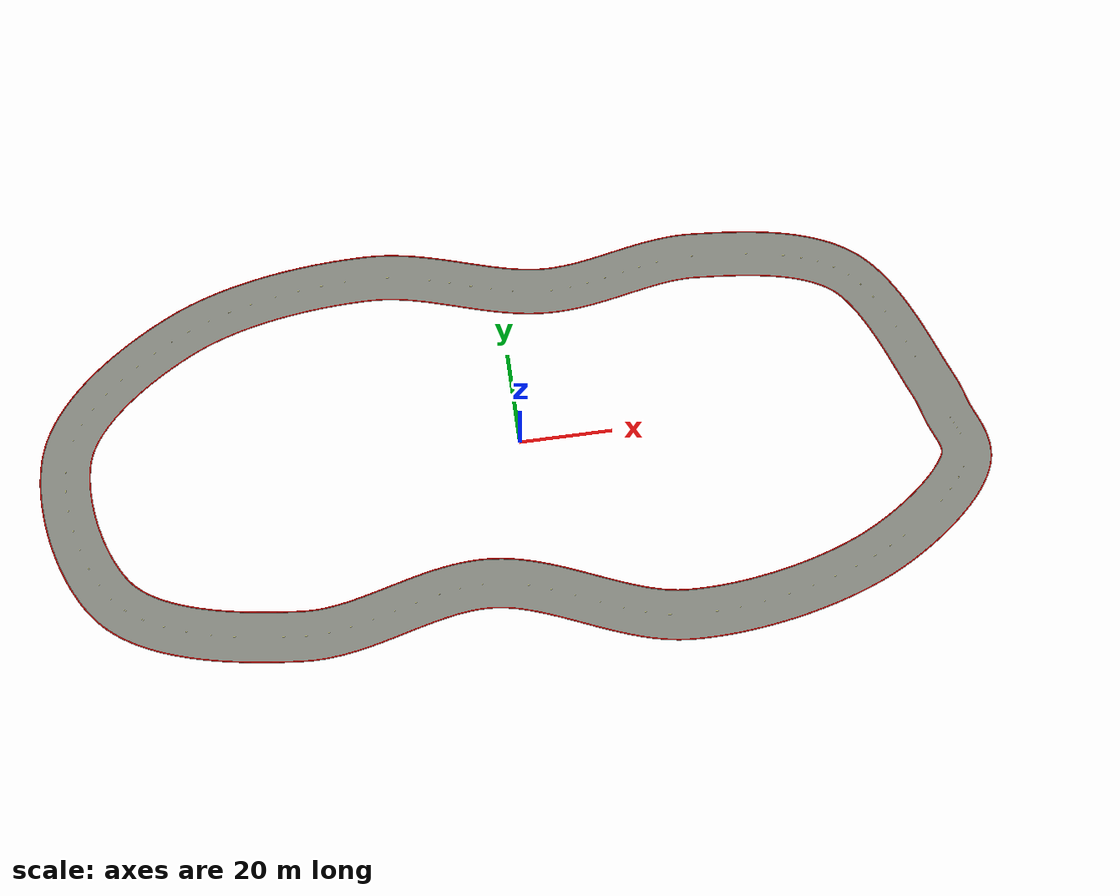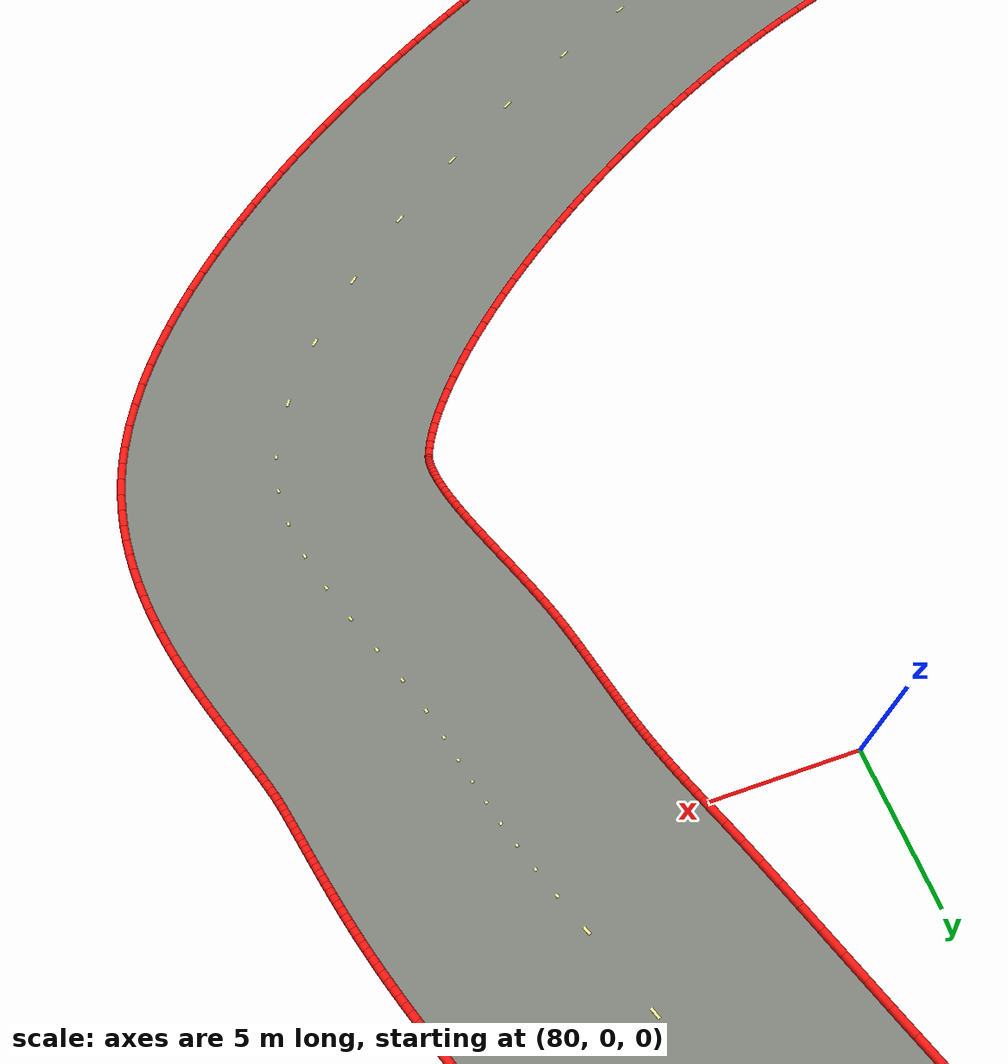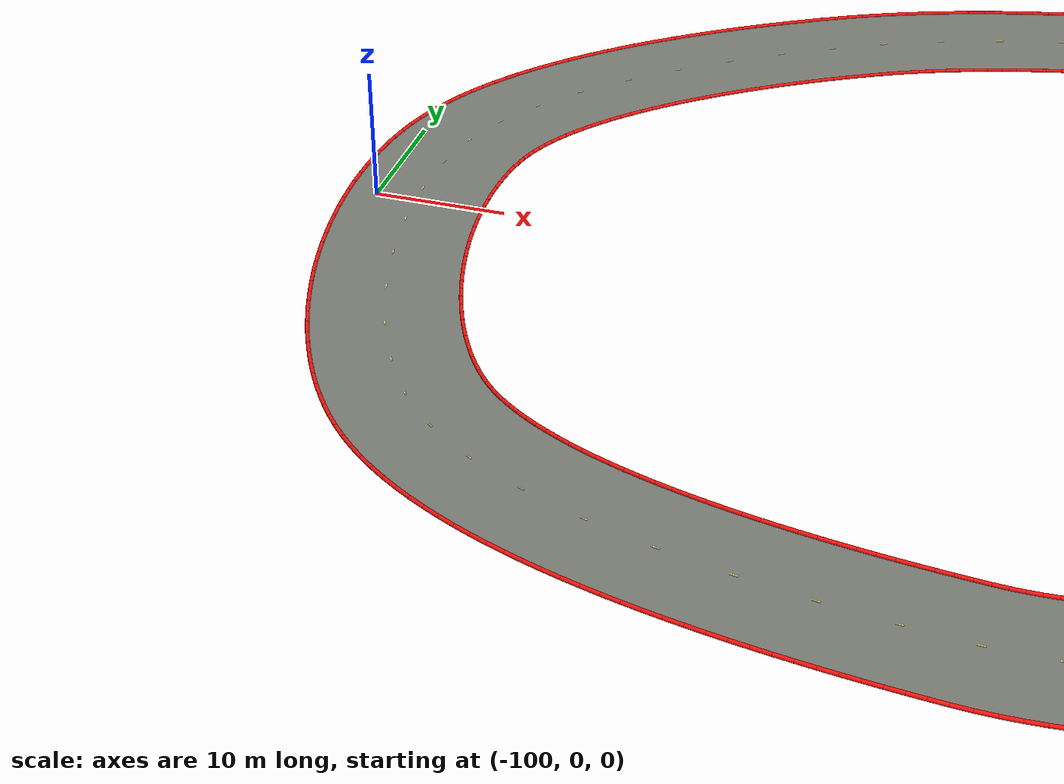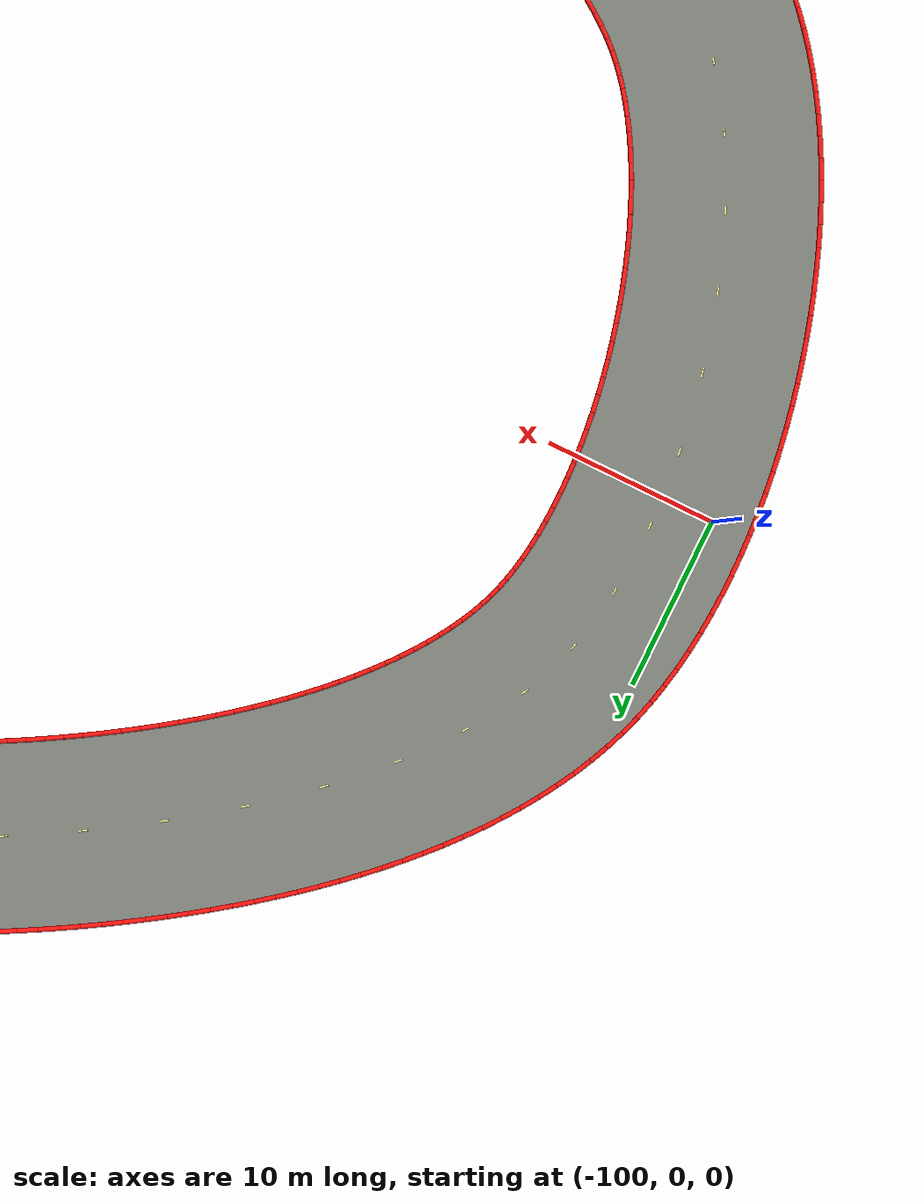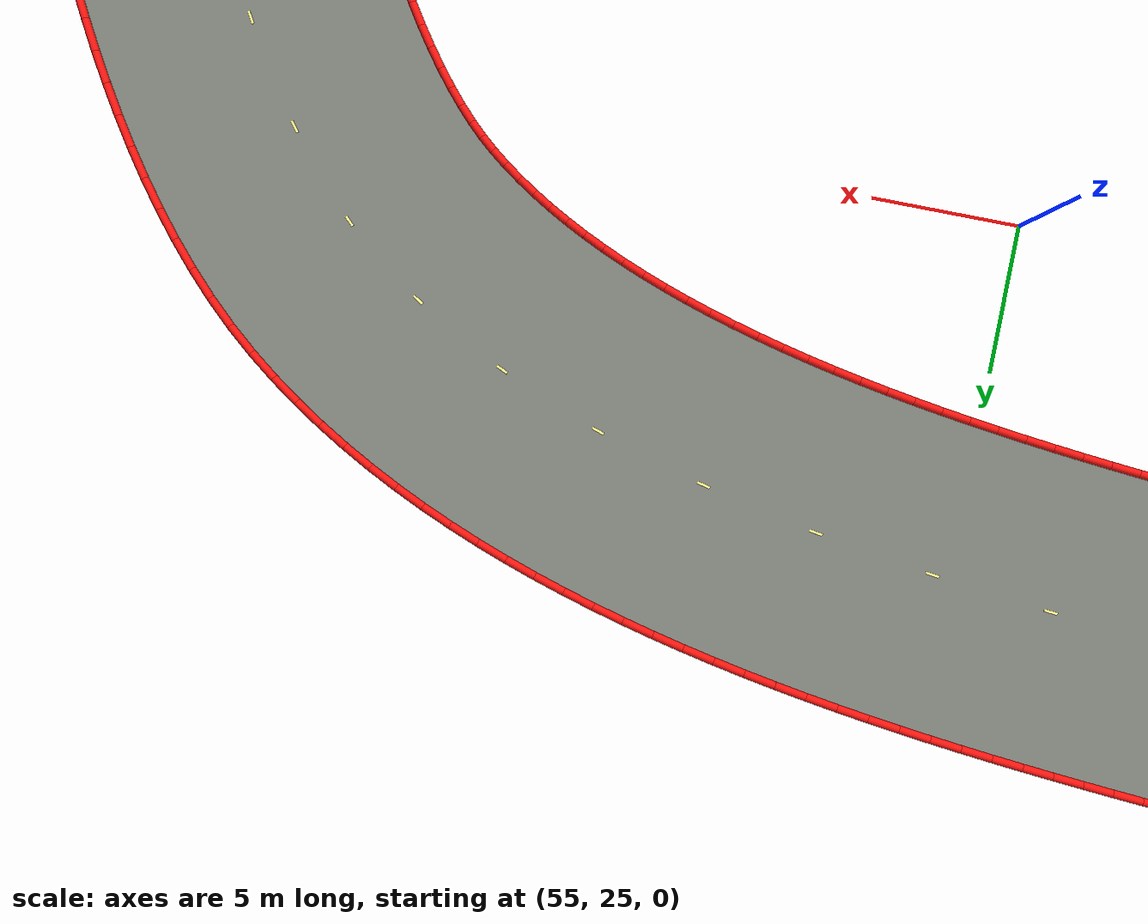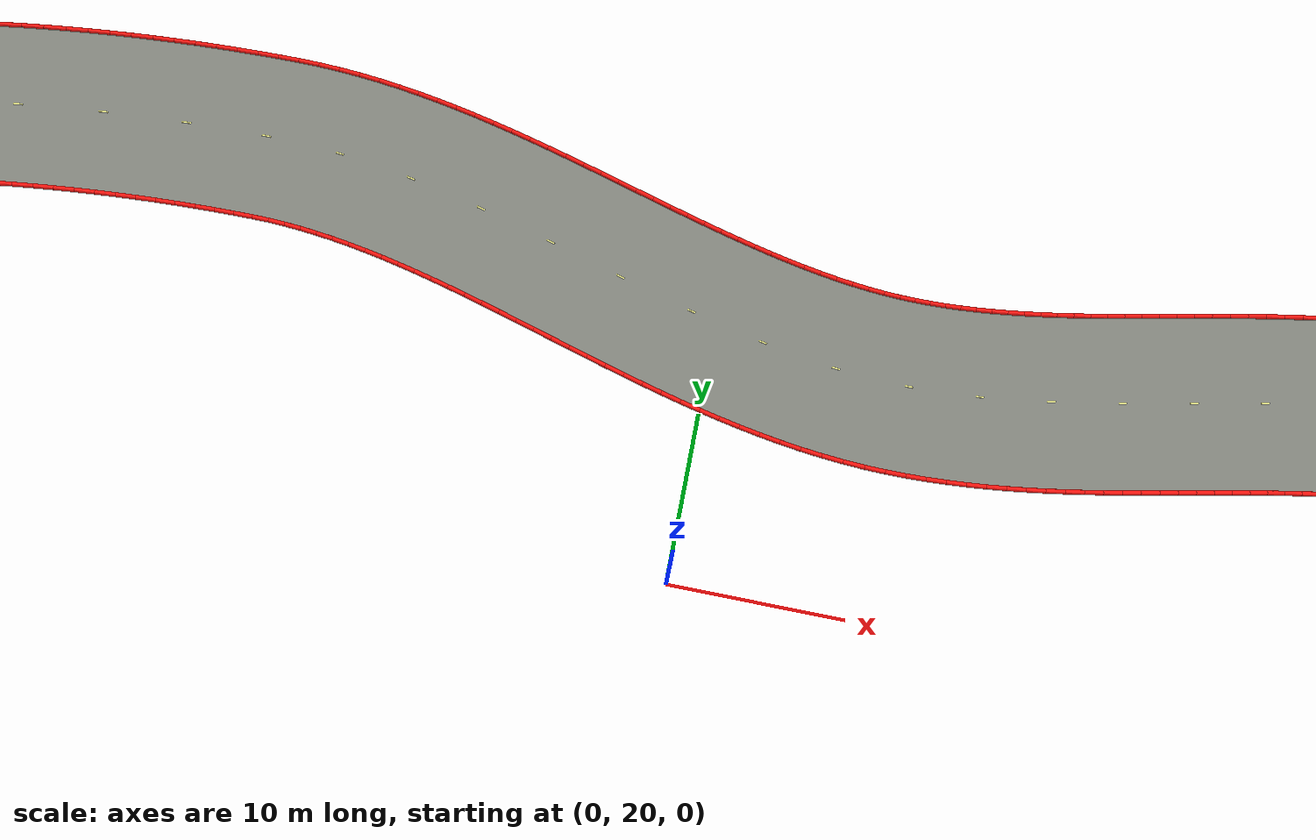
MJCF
<mujoco model="endurance_track_visuals">
  <asset>
    <mesh name="track_surface_mesh" inertia="shell" vertex="85.09739 0.12199 0.02200 84.86086 0.74429 0.02200 84.61244 1.42261 0.02200 84.36089 2.12919 0.02200 84.10461 2.86384 0.02200 83.84244 3.62561 0.02200 83.57349 4.41304 0.02200 83.29707 5.22429 0.02200 83.01264 6.05723 0.02200 82.71975 6.90952 0.02200 82.41803 7.77866 0.02200 82.10716 8.66204 0.02200 81.78689 9.55693 0.02200 81.45701 10.46050 0.02200 81.11735 11.36987 0.02200 80.76780 12.28208 0.02200 80.40828 13.19411 0.02200 80.03878 14.10288 0.02200 79.65932 15.00526 0.02200 79.27003 15.89808 0.02200 78.87107 16.77811 0.02200 78.46271 17.64206 0.02200 78.04533 18.48661 0.02200 77.61942 19.30839 0.02200 77.18563 20.10401 0.02200 76.74476 20.87004 0.02200 76.29784 21.60305 0.02200 75.84611 22.29963 0.02200 75.39111 22.95644 0.02200 74.93467 23.57024 0.02200 74.47894 24.13800 0.02200 74.02646 24.65700 0.02200 73.58007 25.12498 0.02200 73.14288 25.54031 0.02200 72.70090 25.91608 0.02200 72.20228 26.29764 0.02200 71.65865 26.67860 0.02200 71.08280 27.04849 0.02200 70.47513 27.40692 0.02200 69.83629 27.75348 0.02200 69.16713 28.08777 0.02200 68.46868 28.40944 0.02200 67.74209 28.71820 0.02200 66.98863 29.01382 0.02200 66.20967 29.29617 0.02200 65.40660 29.56519 0.02200 64.58090 29.82090 0.02200 63.73404 30.06337 0.02200 62.86754 30.29277 0.02200 61.98291 30.50931 0.02200 61.08165 30.71327 0.02200 60.16528 30.90498 0.02200 59.23529 31.08480 0.02200 58.29318 31.25315 0.02200 57.34041 31.41046 0.02200 56.37844 31.55723 0.02200 55.40870 31.69394 0.02200 54.43263 31.82114 0.02200 53.45161 31.93937 0.02200 52.46704 32.04920 0.02200 51.48028 32.15121 0.02200 50.49267 32.24602 0.02200 49.50553 32.33422 0.02200 48.52017 32.41646 0.02200 47.53786 32.49337 0.02200 46.55987 32.56559 0.02200 45.58741 32.63378 0.02200 44.62169 32.69862 0.02200 43.70272 32.75842 0.02200 42.84349 32.80054 0.02200 42.01351 32.81611 0.02200 41.17266 32.80851 0.02200 40.32066 32.77871 0.02200 39.45736 32.72776 0.02200 38.58269 32.65674 0.02200 37.69666 32.56679 0.02200 36.79935 32.45912 0.02200 35.89085 32.33503 0.02200 34.97132 32.19586 0.02200 34.04090 32.04302 0.02200 33.09974 31.87799 0.02200 32.14797 31.70228 0.02200 31.18575 31.51749 0.02200 30.21316 31.32525 0.02200 29.23031 31.12723 0.02200 28.23725 30.92517 0.02200 27.23401 30.72082 0.02200 26.22062 30.51600 0.02200 25.19704 30.31257 0.02200 24.16324 30.11241 0.02200 23.11915 29.91746 0.02200 22.06469 29.72971 0.02200 20.99977 29.55118 0.02200 19.92428 29.38395 0.02200 18.83812 29.23014 0.02200 17.74121 29.09195 0.02200 16.63346 28.97159 0.02200 15.51484 28.87136 0.02200 14.38536 28.79360 0.02200 13.24509 28.74068 0.02200 12.09417 28.71503 0.02200 10.93282 28.71912 0.02200 9.75913 28.75553 0.02200 8.51114 28.83158 0.02200 7.26778 28.94464 0.02200 6.03461 29.09135 0.02200 4.81159 29.26867 0.02200 3.59855 29.47367 0.02200 2.39526 29.70348 0.02200 1.20143 29.95536 0.02200 0.01676 30.22665 0.02200 -1.15906 30.51475 0.02200 -2.32635 30.81717 0.02200 -3.48540 31.13146 0.02200 -4.63648 31.45524 0.02200 -5.77983 31.78620 0.02200 -6.91564 32.12205 0.02200 -8.04409 32.46058 0.02200 -9.16528 32.79960 0.02200 -10.27931 33.13696 0.02200 -11.38620 33.47055 0.02200 -12.48597 33.79831 0.02200 -13.57856 34.11821 0.02200 -14.66389 34.42824 0.02200 -15.74186 34.72648 0.02200 -16.81233 35.01100 0.02200 -17.87512 35.27997 0.02200 -18.93007 35.53158 0.02200 -19.97698 35.76410 0.02200 -21.01567 35.97585 0.02200 -22.04598 36.16522 0.02200 -23.06777 36.33068 0.02200 -24.08096 36.47076 0.02200 -25.08554 36.58406 0.02200 -26.08159 36.66925 0.02200 -27.06931 36.72505 0.02200 -28.07888 36.75059 0.02200 -29.20721 36.75537 0.02200 -30.37895 36.74847 0.02200 -31.56448 36.72936 0.02200 -32.76240 36.69783 0.02200 -33.97132 36.65369 0.02200 -35.18988 36.59678 0.02200 -36.41670 36.52690 0.02200 -37.65040 36.44390 0.02200 -38.88963 36.34760 0.02200 -40.13302 36.23785 0.02200 -41.37920 36.11450 0.02200 -42.62680 35.97738 0.02200 -43.87447 35.82638 0.02200 -45.12084 35.66134 0.02200 -46.36454 35.48215 0.02200 -47.60419 35.28869 0.02200 -48.83842 35.08084 0.02200 -50.06585 34.85851 0.02200 -51.28510 34.62161 0.02200 -52.49479 34.37006 0.02200 -53.69350 34.10380 0.02200 -54.87986 33.82279 0.02200 -56.05245 33.52698 0.02200 -57.20986 33.21637 0.02200 -58.35068 32.89097 0.02200 -59.47348 32.55080 0.02200 -60.57685 32.19594 0.02200 -61.65935 31.82646 0.02200 -62.71955 31.44249 0.02200 -63.75603 31.04418 0.02200 -64.76737 30.63173 0.02200 -65.75213 30.20537 0.02200 -66.70893 29.76541 0.02200 -67.65193 29.30436 0.02200 -68.52177 28.85932 0.02200 -69.41423 28.38939 0.02200 -70.31260 27.90252 0.02200 -71.21496 27.39929 0.02200 -72.11938 26.88028 0.02200 -73.02396 26.34608 0.02200 -73.92680 25.79729 0.02200 -74.82601 25.23453 0.02200 -75.71968 24.65842 0.02200 -76.60594 24.06961 0.02200 -77.48290 23.46877 0.02200 -78.34868 22.85659 0.02200 -79.20139 22.23378 0.02200 -80.03915 21.60108 0.02200 -80.86009 20.95929 0.02200 -81.66234 20.30921 0.02200 -82.44402 19.65170 0.02200 -83.20329 18.98768 0.02200 -83.93831 18.31810 0.02200 -84.64724 17.64399 0.02200 -85.32831 16.96643 0.02200 -85.97974 16.28658 0.02200 -86.59985 15.60568 0.02200 -87.18697 14.92503 0.02200 -87.73956 14.24604 0.02200 -88.25617 13.57017 0.02200 -88.73547 12.89898 0.02200 -89.17632 12.23408 0.02200 -89.57777 11.57710 0.02200 -89.93911 10.92970 0.02200 -90.25990 10.29345 0.02200 -90.54003 9.66982 0.02200 -90.77968 9.06006 0.02200 -90.98160 8.45788 0.02200 -91.15595 7.83344 0.02200 -91.31185 7.15678 0.02200 -91.44641 6.43360 0.02200 -91.55790 5.66762 0.02200 -91.64503 4.86263 0.02200 -91.70685 4.02236 0.02200 -91.74272 3.15051 0.02200 -91.75223 2.25067 0.02200 -91.73518 1.32637 0.02200 -91.69155 0.38107 0.02200 -91.62142 -0.58188 0.02200 -91.52501 -1.55916 0.02200 -91.40262 -2.54754 0.02200 -91.25464 -3.54384 0.02200 -91.08153 -4.54490 0.02200 -90.88382 -5.54763 0.02200 -90.66208 -6.54896 0.02200 -90.41697 -7.54583 0.02200 -90.14919 -8.53521 0.02200 -89.85949 -9.51407 0.02200 -89.54871 -10.47939 0.02200 -89.21774 -11.42816 0.02200 -88.86757 -12.35737 0.02200 -88.49926 -13.26397 0.02200 -88.11397 -14.14495 0.02200 -87.71300 -14.99726 0.02200 -87.29779 -15.81788 0.02200 -86.86991 -16.60376 0.02200 -86.43114 -17.35192 0.02200 -85.98350 -18.05938 0.02200 -85.52921 -18.72326 0.02200 -85.07082 -19.34082 0.02200 -84.61115 -19.90950 0.02200 -84.15982 -20.42012 0.02200 -83.65821 -20.93130 0.02200 -83.11468 -21.42819 0.02200 -82.51897 -21.92038 0.02200 -81.87172 -22.40630 0.02200 -81.17408 -22.88434 0.02200 -80.42762 -23.35296 0.02200 -79.63427 -23.81080 0.02200 -78.79619 -24.25664 0.02200 -77.91573 -24.68947 0.02200 -76.99537 -25.10845 0.02200 -76.03764 -25.51291 0.02200 -75.04516 -25.90236 0.02200 -74.02056 -26.27642 0.02200 -72.96646 -26.63485 0.02200 -71.88550 -26.97753 0.02200 -70.78028 -27.30441 0.02200 -69.65341 -27.61554 0.02200 -68.50744 -27.91104 0.02200 -67.34494 -28.19108 0.02200 -66.16843 -28.45590 0.02200 -64.98040 -28.70575 0.02200 -63.78333 -28.94095 0.02200 -62.57968 -29.16185 0.02200 -61.37188 -29.36880 0.02200 -60.16234 -29.56221 0.02200 -58.95346 -29.74248 0.02200 -57.74761 -29.91005 0.02200 -56.54716 -30.06536 0.02200 -55.35444 -30.20887 0.02200 -54.17179 -30.34105 0.02200 -53.00152 -30.46238 0.02200 -51.84593 -30.57335 0.02200 -50.70732 -30.67446 0.02200 -49.63178 -30.76293 0.02200 -48.63955 -30.82176 0.02200 -47.67684 -30.84136 0.02200 -46.69765 -30.82643 0.02200 -45.70174 -30.77832 0.02200 -44.68916 -30.69845 0.02200 -43.66011 -30.58837 0.02200 -42.61495 -30.44976 0.02200 -41.55414 -30.28443 0.02200 -40.47819 -30.09431 0.02200 -39.38766 -29.88147 0.02200 -38.28308 -29.64806 0.02200 -37.16499 -29.39637 0.02200 -36.03390 -29.12876 0.02200 -34.89025 -28.84768 0.02200 -33.73447 -28.55564 0.02200 -32.56689 -28.25524 0.02200 -31.38780 -27.94911 0.02200 -30.19744 -27.63998 0.02200 -28.99596 -27.33060 0.02200 -27.78346 -27.02379 0.02200 -26.55999 -26.72244 0.02200 -25.32553 -26.42950 0.02200 -24.08001 -26.14798 0.02200 -22.82333 -25.88099 0.02200 -21.55534 -25.63170 0.02200 -20.27591 -25.40340 0.02200 -18.98486 -25.19947 0.02200 -17.68209 -25.02342 0.02200 -16.36751 -24.87887 0.02200 -15.04116 -24.76956 0.02200 -13.70320 -24.69936 0.02200 -12.35395 -24.67223 0.02200 -10.99396 -24.69224 0.02200 -9.62436 -24.76346 0.02200 -8.23592 -24.89059 0.02200 -6.86030 -25.06997 0.02200 -5.50162 -25.29680 0.02200 -4.15982 -25.56670 0.02200 -2.83459 -25.87541 0.02200 -1.52548 -26.21885 0.02200 -0.23192 -26.59309 0.02200 1.04673 -26.99435 0.02200 2.31114 -27.41900 0.02200 3.56196 -27.86354 0.02200 4.79985 -28.32458 0.02200 6.02541 -28.79884 0.02200 7.23918 -29.28310 0.02200 8.44164 -29.77424 0.02200 9.63321 -30.26918 0.02200 10.81423 -30.76493 0.02200 11.98497 -31.25852 0.02200 13.14562 -31.74705 0.02200 14.29628 -32.22764 0.02200 15.43701 -32.69749 0.02200 16.56776 -33.15384 0.02200 17.68842 -33.59399 0.02200 18.79884 -34.01531 0.02200 19.89878 -34.41524 0.02200 20.98796 -34.79133 0.02200 22.06610 -35.14120 0.02200 23.13287 -35.46261 0.02200 24.18798 -35.75347 0.02200 25.23118 -36.01179 0.02200 26.26231 -36.23576 0.02200 27.28134 -36.42372 0.02200 28.28843 -36.57414 0.02200 29.28401 -36.68563 0.02200 30.30059 -36.75861 0.02200 31.39742 -36.80486 0.02200 32.54287 -36.83321 0.02200 33.70613 -36.84222 0.02200 34.88548 -36.83209 0.02200 36.07926 -36.80302 0.02200 37.28578 -36.75527 0.02200 38.50341 -36.68909 0.02200 39.73051 -36.60475 0.02200 40.96546 -36.50256 0.02200 42.20667 -36.38282 0.02200 43.45255 -36.24586 0.02200 44.70149 -36.09200 0.02200 45.95194 -35.92160 0.02200 47.20232 -35.73500 0.02200 48.45107 -35.53257 0.02200 49.69663 -35.31469 0.02200 50.93744 -35.08172 0.02200 52.17194 -34.83408 0.02200 53.39858 -34.57215 0.02200 54.61579 -34.29635 0.02200 55.82202 -34.00709 0.02200 57.01570 -33.70482 0.02200 58.19526 -33.38997 0.02200 59.35911 -33.06301 0.02200 60.50568 -32.72441 0.02200 61.63335 -32.37467 0.02200 62.74053 -32.01430 0.02200 63.82557 -31.64384 0.02200 64.88684 -31.26386 0.02200 65.92267 -30.87496 0.02200 66.93138 -30.47778 0.02200 67.91125 -30.07299 0.02200 68.86056 -29.66134 0.02200 69.78323 -29.24096 0.02200 70.52158 -28.88936 0.02200 71.27371 -28.51790 0.02200 72.03295 -28.12971 0.02200 72.79737 -27.72572 0.02200 73.56505 -27.30691 0.02200 74.33413 -26.87426 0.02200 75.10275 -26.42872 0.02200 75.86909 -25.97130 0.02200 76.63134 -25.50299 0.02200 77.38770 -25.02481 0.02200 78.13638 -24.53778 0.02200 78.87559 -24.04295 0.02200 79.60354 -23.54139 0.02200 80.31844 -23.03420 0.02200 81.01849 -22.52253 0.02200 81.70189 -22.00753 0.02200 82.36682 -21.49043 0.02200 83.01143 -20.97252 0.02200 83.63390 -20.45513 0.02200 84.23233 -19.93971 0.02200 84.80485 -19.42779 0.02200 85.34956 -18.92103 0.02200 85.86451 -18.42124 0.02200 86.34779 -17.93042 0.02200 86.79746 -17.45078 0.02200 87.21159 -16.98482 0.02200 87.58832 -16.53537 0.02200 87.92588 -16.10564 0.02200 88.22267 -15.69936 0.02200 88.47738 -15.32081 0.02200 88.68915 -14.97490 0.02200 88.85784 -14.66725 0.02200 88.98433 -14.40414 0.02200 89.07719 -14.17559 0.02200 89.08839 -14.14099 0.02200 89.10146 -14.09295 0.02200 89.11307 -14.03866 0.02200 89.12314 -13.97532 0.02200 89.13118 -13.90057 0.02200 89.13638 -13.81258 0.02200 89.13778 -13.71004 0.02200 89.13437 -13.59210 0.02200 89.12516 -13.45838 0.02200 89.10928 -13.30885 0.02200 89.08603 -13.14375 0.02200 89.05486 -12.96355 0.02200 89.01541 -12.76887 0.02200 88.96749 -12.56038 0.02200 88.91108 -12.33884 0.02200 88.84630 -12.10497 0.02200 88.77339 -11.85950 0.02200 88.69272 -11.60308 0.02200 88.60472 -11.33632 0.02200 88.50994 -11.05974 0.02200 88.40894 -10.77378 0.02200 88.30238 -10.47877 0.02200 88.19094 -10.17496 0.02200 88.07535 -9.86248 0.02200 87.95637 -9.54131 0.02200 87.83481 -9.21136 0.02200 87.71151 -8.87234 0.02200 87.58736 -8.52386 0.02200 87.46333 -8.16534 0.02200 87.34047 -7.79601 0.02200 87.21992 -7.41495 0.02200 87.10301 -7.02102 0.02200 86.99125 -6.61287 0.02200 86.89478 -6.22443 0.02200 86.83198 -5.95441 0.02200 86.77904 -5.72423 0.02200 86.72821 -5.50164 0.02200 86.67932 -5.28640 0.02200 86.63221 -5.07826 0.02200 86.58670 -4.87694 0.02200 86.54262 -4.68215 0.02200 86.49978 -4.49357 0.02200 86.45802 -4.31084 0.02200 86.41715 -4.13357 0.02200 86.37698 -3.96133 0.02200 86.33732 -3.79361 0.02200 86.29798 -3.62990 0.02200 86.25874 -3.46962 0.02200 86.21940 -3.31213 0.02200 86.17973 -3.15677 0.02200 86.13950 -3.00284 0.02200 86.09846 -2.84962 0.02200 86.05635 -2.69634 0.02200 86.01291 -2.54226 0.02200 85.96786 -2.38660 0.02200 85.92093 -2.22861 0.02200 85.87183 -2.06754 0.02200 85.82027 -1.90266 0.02200 85.76595 -1.73327 0.02200 85.70860 -1.55869 0.02200 85.64792 -1.37826 0.02200 85.58364 -1.19138 0.02200 85.51546 -0.99744 0.02200 85.44313 -0.79588 0.02200 85.36638 -0.58618 0.02200 85.28496 -0.36780 0.02200 85.19860 -0.14027 0.02200 94.90261 3.87801 0.02200 94.69819 4.41539 0.02200 94.48843 4.98839 0.02200 94.26400 5.61895 0.02200 94.02595 6.30143 0.02200 93.77489 7.03096 0.02200 93.51114 7.80318 0.02200 93.23483 8.61411 0.02200 92.94595 9.46006 0.02200 92.64440 10.33755 0.02200 92.32998 11.24323 0.02200 92.00244 12.17393 0.02200 91.66150 13.12654 0.02200 91.30679 14.09806 0.02200 90.93792 15.08556 0.02200 90.55447 16.08617 0.02200 90.15593 17.09710 0.02200 89.74177 18.11559 0.02200 89.31140 19.13895 0.02200 88.86415 20.16455 0.02200 88.39929 21.18979 0.02200 87.91599 22.21213 0.02200 87.41331 23.22906 0.02200 86.89021 24.23814 0.02200 86.34548 25.23694 0.02200 85.77776 26.22307 0.02200 85.18546 27.19413 0.02200 84.56678 28.14771 0.02200 83.91964 29.08133 0.02200 83.24164 29.99241 0.02200 82.53005 30.87815 0.02200 81.78181 31.73546 0.02200 80.99350 32.56077 0.02200 80.16144 33.34990 0.02200 79.29910 34.08392 0.02200 78.41135 34.76507 0.02200 77.51168 35.39595 0.02200 76.58983 35.98844 0.02200 75.64791 36.54434 0.02200 74.68779 37.06546 0.02200 73.71114 37.55361 0.02200 72.71945 38.01053 0.02200 71.71408 38.43793 0.02200 70.69629 38.83743 0.02200 69.66723 39.21057 0.02200 68.62802 39.55882 0.02200 67.57970 39.88356 0.02200 66.52332 40.18611 0.02200 65.45987 40.46773 0.02200 64.39039 40.72959 0.02200 63.31585 40.97282 0.02200 62.23729 41.19851 0.02200 61.15571 41.40769 0.02200 60.07216 41.60135 0.02200 58.98767 41.78045 0.02200 57.90332 41.94591 0.02200 56.82017 42.09864 0.02200 55.73933 42.23951 0.02200 54.66191 42.36938 0.02200 53.58906 42.48907 0.02200 52.52192 42.59942 0.02200 51.46166 42.70121 0.02200 50.40950 42.79524 0.02200 49.36663 42.88229 0.02200 48.33431 42.96312 0.02200 47.31380 43.03848 0.02200 46.30637 43.10914 0.02200 45.31336 43.17581 0.02200 44.29728 43.24158 0.02200 43.19701 43.29458 0.02200 42.06539 43.31598 0.02200 40.94250 43.30598 0.02200 39.82857 43.26718 0.02200 38.72375 43.20210 0.02200 37.62807 43.11325 0.02200 36.54147 43.00305 0.02200 35.46386 42.87385 0.02200 34.39508 42.72795 0.02200 33.33498 42.56757 0.02200 32.28337 42.39489 0.02200 31.24007 42.21199 0.02200 30.20490 42.02093 0.02200 29.17770 41.82369 0.02200 28.15833 41.62222 0.02200 27.14666 41.41841 0.02200 26.14260 41.21412 0.02200 25.14609 41.01114 0.02200 24.15708 40.81124 0.02200 23.17555 40.61614 0.02200 22.20152 40.42753 0.02200 21.23502 40.24703 0.02200 20.27610 40.07625 0.02200 19.32482 39.91672 0.02200 18.38124 39.76995 0.02200 17.44545 39.63737 0.02200 16.51749 39.52040 0.02200 15.59741 39.42035 0.02200 14.68521 39.33854 0.02200 13.78085 39.27618 0.02200 12.88423 39.23447 0.02200 11.99517 39.21457 0.02200 11.11342 39.21757 0.02200 10.24087 39.24447 0.02200 9.30634 39.30142 0.02200 8.36420 39.38724 0.02200 7.40886 39.50103 0.02200 6.44036 39.64157 0.02200 5.45884 39.80756 0.02200 4.46450 39.99757 0.02200 3.45762 40.21010 0.02200 2.43848 40.44356 0.02200 1.40736 40.69628 0.02200 0.36457 40.96650 0.02200 -0.68962 41.25240 0.02200 -1.75497 41.55211 0.02200 -2.83126 41.86369 0.02200 -3.91831 42.18515 0.02200 -5.01597 42.51446 0.02200 -6.12415 42.84955 0.02200 -7.24279 43.18830 0.02200 -8.37186 43.52857 0.02200 -9.51139 43.86816 0.02200 -10.66145 44.20486 0.02200 -11.82212 44.53638 0.02200 -12.99355 44.86042 0.02200 -14.17590 45.17463 0.02200 -15.36934 45.47659 0.02200 -16.57409 45.76385 0.02200 -17.79034 46.03389 0.02200 -19.01830 46.28412 0.02200 -20.25815 46.51189 0.02200 -21.51006 46.71449 0.02200 -22.77412 46.88911 0.02200 -24.05036 47.03290 0.02200 -25.33872 47.14294 0.02200 -26.63903 47.21623 0.02200 -27.92112 47.24941 0.02200 -29.21483 47.25537 0.02200 -30.49449 47.24784 0.02200 -31.78727 47.22699 0.02200 -33.09207 47.19265 0.02200 -34.40781 47.14462 0.02200 -35.73338 47.08270 0.02200 -37.06767 47.00670 0.02200 -38.40959 46.91642 0.02200 -39.75800 46.81163 0.02200 -41.11182 46.69213 0.02200 -42.46991 46.55769 0.02200 -43.83116 46.40808 0.02200 -45.19448 46.24308 0.02200 -46.55873 46.06243 0.02200 -47.92281 45.86588 0.02200 -49.28562 45.65319 0.02200 -50.64606 45.42408 0.02200 -52.00302 45.17827 0.02200 -53.35541 44.91549 0.02200 -54.70215 44.63542 0.02200 -56.04214 44.33776 0.02200 -57.37430 44.02219 0.02200 -58.69757 43.68834 0.02200 -60.01088 43.33587 0.02200 -61.31316 42.96438 0.02200 -62.60336 42.57347 0.02200 -63.88042 42.16270 0.02200 -65.14329 41.73162 0.02200 -66.39093 41.27971 0.02200 -67.62228 40.80646 0.02200 -68.83630 40.31128 0.02200 -70.03191 39.79357 0.02200 -71.20805 39.25266 0.02200 -72.34807 38.69564 0.02200 -73.35858 38.17894 0.02200 -74.36190 37.65063 0.02200 -75.37128 37.10359 0.02200 -76.38522 36.53813 0.02200 -77.40220 35.95452 0.02200 -78.42067 35.35305 0.02200 -79.43911 34.73399 0.02200 -80.45596 34.09758 0.02200 -81.46969 33.44406 0.02200 -82.47873 32.77366 0.02200 -83.48154 32.08657 0.02200 -84.47655 31.38297 0.02200 -85.46222 30.66301 0.02200 -86.43697 29.92682 0.02200 -87.39925 29.17448 0.02200 -88.34750 28.40603 0.02200 -89.28013 27.62150 0.02200 -90.19556 26.82083 0.02200 -91.09219 26.00392 0.02200 -91.96841 25.17064 0.02200 -92.82257 24.32075 0.02200 -93.65299 23.45396 0.02200 -94.45793 22.56991 0.02200 -95.23559 21.66815 0.02200 -95.98410 20.74815 0.02200 -96.70147 19.80931 0.02200 -97.38557 18.85094 0.02200 -98.03411 17.87231 0.02200 -98.64461 16.87262 0.02200 -99.21433 15.85112 0.02200 -99.74026 14.80707 0.02200 -100.21910 13.73989 0.02200 -100.64721 12.64919 0.02200 -101.01840 11.54212 0.02200 -101.33021 10.42852 0.02200 -101.59101 9.29894 0.02200 -101.80474 8.15259 0.02200 -101.97422 6.99062 0.02200 -102.10182 5.81419 0.02200 -102.18957 4.62445 0.02200 -102.23919 3.42261 0.02200 -102.25215 2.21000 0.02200 -102.22973 0.98797 0.02200 -102.17305 -0.24201 0.02200 -102.08308 -1.47840 0.02200 -101.96069 -2.71960 0.02200 -101.80665 -3.96395 0.02200 -101.62165 -5.20971 0.02200 -101.40631 -6.45514 0.02200 -101.16118 -7.69842 0.02200 -100.88675 -8.93772 0.02200 -100.58346 -10.17120 0.02200 -100.25168 -11.39697 0.02200 -99.89172 -12.61316 0.02200 -99.50384 -13.81787 0.02200 -99.08820 -15.00923 0.02200 -98.64492 -16.18534 0.02200 -98.17400 -17.34432 0.02200 -97.67535 -18.48430 0.02200 -97.14876 -19.60340 0.02200 -96.59387 -20.69977 0.02200 -96.01017 -21.77151 0.02200 -95.39696 -22.81673 0.02200 -94.75331 -23.83349 0.02200 -94.07806 -24.81975 0.02200 -93.36976 -25.77336 0.02200 -92.62664 -26.69198 0.02200 -91.84018 -27.57988 0.02200 -90.95092 -28.48553 0.02200 -90.00562 -29.35062 0.02200 -89.01892 -30.16663 0.02200 -87.99459 -30.93628 0.02200 -86.93585 -31.66226 0.02200 -85.84550 -32.34721 0.02200 -84.72603 -32.99361 0.02200 -83.57964 -33.60376 0.02200 -82.40837 -34.17979 0.02200 -81.21414 -34.72364 0.02200 -79.99878 -35.23708 0.02200 -78.76407 -35.72172 0.02200 -77.51177 -36.17902 0.02200 -76.24363 -36.61033 0.02200 -74.96142 -37.01688 0.02200 -73.66690 -37.39982 0.02200 -72.36187 -37.76020 0.02200 -71.04814 -38.09902 0.02200 -69.72755 -38.41719 0.02200 -68.40195 -38.71559 0.02200 -67.07324 -38.99507 0.02200 -65.74331 -39.25640 0.02200 -64.41412 -39.50036 0.02200 -63.08759 -39.72768 0.02200 -61.76572 -39.93907 0.02200 -60.45049 -40.13522 0.02200 -59.14391 -40.31680 0.02200 -57.84800 -40.48447 0.02200 -56.56481 -40.63888 0.02200 -55.29639 -40.78065 0.02200 -54.04481 -40.91042 0.02200 -52.81216 -41.02880 0.02200 -51.60054 -41.13639 0.02200 -50.36822 -41.23707 0.02200 -49.05471 -41.31355 0.02200 -47.70498 -41.34132 0.02200 -46.36541 -41.32117 0.02200 -45.03657 -41.25722 0.02200 -43.71881 -41.15351 0.02200 -42.41225 -41.01396 0.02200 -41.11691 -40.84235 0.02200 -39.83269 -40.64236 0.02200 -38.55943 -40.41751 0.02200 -37.29694 -40.17121 0.02200 -36.04503 -39.90677 0.02200 -34.80353 -39.62738 0.02200 -33.57230 -39.33614 0.02200 -32.35123 -39.03607 0.02200 -31.14029 -38.73013 0.02200 -29.93947 -38.42119 0.02200 -28.74886 -38.11208 0.02200 -27.56858 -37.80556 0.02200 -26.39883 -37.50433 0.02200 -25.23987 -37.21104 0.02200 -24.09201 -36.92828 0.02200 -22.95563 -36.65856 0.02200 -21.83116 -36.40433 0.02200 -20.71906 -36.16797 0.02200 -19.61983 -35.95177 0.02200 -18.53398 -35.75790 0.02200 -17.46202 -35.58846 0.02200 -16.40444 -35.44540 0.02200 -15.36166 -35.33058 0.02200 -14.33401 -35.24572 0.02200 -13.32171 -35.19242 0.02200 -12.32476 -35.17219 0.02200 -11.34300 -35.18643 0.02200 -10.37564 -35.23654 0.02200 -9.39440 -35.32649 0.02200 -8.40486 -35.45575 0.02200 -7.40256 -35.62330 0.02200 -6.38724 -35.82772 0.02200 -5.35888 -36.06746 0.02200 -4.31760 -36.34081 0.02200 -3.26365 -36.64588 0.02200 -2.19733 -36.98064 0.02200 -1.11899 -37.34292 0.02200 -0.02896 -37.73042 0.02200 1.07245 -38.14071 0.02200 2.18496 -38.57129 0.02200 3.30835 -39.01956 0.02200 4.44247 -39.48282 0.02200 5.58724 -39.95836 0.02200 6.74263 -40.44336 0.02200 7.90871 -40.93500 0.02200 9.08562 -41.43035 0.02200 10.27358 -41.92650 0.02200 11.47287 -42.42043 0.02200 12.68385 -42.90911 0.02200 13.90697 -43.38943 0.02200 15.14271 -43.85822 0.02200 16.39164 -44.31221 0.02200 17.65435 -44.74808 0.02200 18.93147 -45.16238 0.02200 20.22364 -45.55154 0.02200 21.53150 -45.91187 0.02200 22.85561 -46.23953 0.02200 24.19646 -46.53053 0.02200 25.55442 -46.78073 0.02200 26.92964 -46.98585 0.02200 28.32203 -47.14147 0.02200 29.69941 -47.24139 0.02200 31.04451 -47.29893 0.02200 32.37217 -47.33182 0.02200 33.71044 -47.34222 0.02200 35.05827 -47.33067 0.02200 36.41458 -47.29767 0.02200 37.77829 -47.24371 0.02200 39.14826 -47.16927 0.02200 40.52339 -47.07477 0.02200 41.90251 -46.96067 0.02200 43.28448 -46.82736 0.02200 44.66812 -46.67526 0.02200 46.05227 -46.50476 0.02200 47.43573 -46.31623 0.02200 48.81732 -46.11006 0.02200 50.19583 -45.88660 0.02200 51.57007 -45.64620 0.02200 52.93884 -45.38922 0.02200 54.30093 -45.11598 0.02200 55.65514 -44.82680 0.02200 57.00026 -44.52201 0.02200 58.33511 -44.20191 0.02200 59.65848 -43.86679 0.02200 60.96918 -43.51693 0.02200 62.26604 -43.15259 0.02200 63.54789 -42.77404 0.02200 64.81356 -42.38148 0.02200 66.06190 -41.97515 0.02200 67.29178 -41.55522 0.02200 68.50209 -41.12185 0.02200 69.69173 -40.67518 0.02200 70.85963 -40.21528 0.02200 72.00472 -39.74219 0.02200 73.12601 -39.25592 0.02200 74.21677 -38.75904 0.02200 75.10332 -38.33699 0.02200 75.98855 -37.89981 0.02200 76.87608 -37.44604 0.02200 77.76479 -36.97638 0.02200 78.65354 -36.49154 0.02200 79.54117 -35.99219 0.02200 80.42647 -35.47902 0.02200 81.30823 -34.95271 0.02200 82.18520 -34.41392 0.02200 83.05614 -33.86330 0.02200 83.91979 -33.30146 0.02200 84.77489 -32.72904 0.02200 85.62019 -32.14662 0.02200 86.45443 -31.55475 0.02200 87.27636 -30.95396 0.02200 88.08474 -30.34475 0.02200 88.87834 -29.72754 0.02200 89.65595 -29.10273 0.02200 90.41637 -28.47062 0.02200 91.15843 -27.83143 0.02200 91.88095 -27.18529 0.02200 92.58281 -26.53221 0.02200 93.26288 -25.87203 0.02200 93.92005 -25.20441 0.02200 94.55321 -24.52880 0.02200 95.16122 -23.84437 0.02200 95.74291 -23.14995 0.02200 96.29700 -22.44397 0.02200 96.82204 -21.72438 0.02200 97.31631 -20.98855 0.02200 97.77760 -20.23324 0.02200 98.20302 -19.45448 0.02200 98.58863 -18.64766 0.02200 98.92281 -17.82441 0.02200 99.13181 -17.20362 0.02200 99.29950 -16.59295 0.02200 99.43099 -15.98556 0.02200 99.52813 -15.38463 0.02200 99.59320 -14.79284 0.02200 99.62876 -14.21241 0.02200 99.63758 -13.64502 0.02200 99.62244 -13.09184 0.02200 99.58610 -12.55363 0.02200 99.53121 -12.03078 0.02200 99.46026 -11.52341 0.02200 99.37556 -11.03140 0.02200 99.27926 -10.55450 0.02200 99.17332 -10.09239 0.02200 99.05955 -9.64467 0.02200 98.93960 -9.21098 0.02200 98.81501 -8.79096 0.02200 98.68719 -8.38430 0.02200 98.55748 -7.99077 0.02200 98.42712 -7.61018 0.02200 98.29731 -7.24248 0.02200 98.16919 -6.88767 0.02200 98.04385 -6.54588 0.02200 97.92233 -6.21734 0.02200 97.80566 -5.90241 0.02200 97.69480 -5.60156 0.02200 97.59069 -5.31542 0.02200 97.49422 -5.04475 0.02200 97.40619 -4.79050 0.02200 97.32735 -4.55377 0.02200 97.25831 -4.33586 0.02200 97.19954 -4.13827 0.02200 97.15130 -3.96269 0.02200 97.10522 -3.77557 0.02200 97.06252 -3.59094 0.02200 97.01371 -3.37870 0.02200 96.96609 -3.17018 0.02200 96.91943 -2.96472 0.02200 96.87348 -2.76167 0.02200 96.82798 -2.56042 0.02200 96.78270 -2.36034 0.02200 96.73738 -2.16086 0.02200 96.69180 -1.96143 0.02200 96.64571 -1.76155 0.02200 96.59888 -1.56075 0.02200 96.55107 -1.35861 0.02200 96.50208 -1.15477 0.02200 96.45168 -0.94891 0.02200 96.39968 -0.74073 0.02200 96.34586 -0.53003 0.02200 96.29006 -0.31658 0.02200 96.23210 -0.10022 0.02200 96.17181 0.11920 0.02200 96.10904 0.34183 0.02200 96.04365 0.56780 0.02200 95.97549 0.79725 0.02200 95.90443 1.03035 0.02200 95.83034 1.26726 0.02200 95.75310 1.50817 0.02200 95.67257 1.75332 0.02200 95.58862 2.00296 0.02200 95.50111 2.25736 0.02200 95.40990 2.51684 0.02200 95.31484 2.78174 0.02200 95.21578 3.05241 0.02200 95.11256 3.32925 0.02200 95.00500 3.61268 0.02200" face="0 477 1 0 476 477 1 478 2 1 477 478 2 479 3 2 478 479 3 480 4 3 479 480 4 481 5 4 480 481 5 482 6 5 481 482 6 483 7 6 482 483 7 484 8 7 483 484 8 485 9 8 484 485 9 486 10 9 485 486 10 487 11 10 486 487 11 488 12 11 487 488 12 489 13 12 488 489 13 490 14 13 489 490 14 491 15 14 490 491 15 492 16 15 491 492 16 493 17 16 492 493 17 494 18 17 493 494 18 495 19 18 494 495 19 496 20 19 495 496 20 497 21 20 496 497 21 498 22 21 497 498 22 499 23 22 498 499 23 500 24 23 499 500 24 501 25 24 500 501 25 502 26 25 501 502 26 503 27 26 502 503 27 504 28 27 503 504 28 505 29 28 504 505 29 506 30 29 505 506 30 507 31 30 506 507 31 508 32 31 507 508 32 509 33 32 508 509 33 510 34 33 509 510 34 511 35 34 510 511 35 512 36 35 511 512 36 513 37 36 512 513 37 514 38 37 513 514 38 515 39 38 514 515 39 516 40 39 515 516 40 517 41 40 516 517 41 518 42 41 517 518 42 519 43 42 518 519 43 520 44 43 519 520 44 521 45 44 520 521 45 522 46 45 521 522 46 523 47 46 522 523 47 524 48 47 523 524 48 525 49 48 524 525 49 526 50 49 525 526 50 527 51 50 526 527 51 528 52 51 527 528 52 529 53 52 528 529 53 530 54 53 529 530 54 531 55 54 530 531 55 532 56 55 531 532 56 533 57 56 532 533 57 534 58 57 533 534 58 535 59 58 534 535 59 536 60 59 535 536 60 537 61 60 536 537 61 538 62 61 537 538 62 539 63 62 538 539 63 540 64 63 539 540 64 541 65 64 540 541 65 542 66 65 541 542 66 543 67 66 542 543 67 544 68 67 543 544 68 545 69 68 544 545 69 546 70 69 545 546 70 547 71 70 546 547 71 548 72 71 547 548 72 549 73 72 548 549 73 550 74 73 549 550 74 551 75 74 550 551 75 552 76 75 551 552 76 553 77 76 552 553 77 554 78 77 553 554 78 555 79 78 554 555 79 556 80 79 555 556 80 557 81 80 556 557 81 558 82 81 557 558 82 559 83 82 558 559 83 560 84 83 559 560 84 561 85 84 560 561 85 562 86 85 561 562 86 563 87 86 562 563 87 564 88 87 563 564 88 565 89 88 564 565 89 566 90 89 565 566 90 567 91 90 566 567 91 568 92 91 567 568 92 569 93 92 568 569 93 570 94 93 569 570 94 571 95 94 570 571 95 572 96 95 571 572 96 573 97 96 572 573 97 574 98 97 573 574 98 575 99 98 574 575 99 576 100 99 575 576 100 577 101 100 576 577 101 578 102 101 577 578 102 579 103 102 578 579 103 580 104 103 579 580 104 581 105 104 580 581 105 582 106 105 581 582 106 583 107 106 582 583 107 584 108 107 583 584 108 585 109 108 584 585 109 586 110 109 585 586 110 587 111 110 586 587 111 588 112 111 587 588 112 589 113 112 588 589 113 590 114 113 589 590 114 591 115 114 590 591 115 592 116 115 591 592 116 593 117 116 592 593 117 594 118 117 593 594 118 595 119 118 594 595 119 596 120 119 595 596 120 597 121 120 596 597 121 598 122 121 597 598 122 599 123 122 598 599 123 600 124 123 599 600 124 601 125 124 600 601 125 602 126 125 601 602 126 603 127 126 602 603 127 604 128 127 603 604 128 605 129 128 604 605 129 606 130 129 605 606 130 607 131 130 606 607 131 608 132 131 607 608 132 609 133 132 608 609 133 610 134 133 609 610 134 611 135 134 610 611 135 612 136 135 611 612 136 613 137 136 612 613 137 614 138 137 613 614 138 615 139 138 614 615 139 616 140 139 615 616 140 617 141 140 616 617 141 618 142 141 617 618 142 619 143 142 618 619 143 620 144 143 619 620 144 621 145 144 620 621 145 622 146 145 621 622 146 623 147 146 622 623 147 624 148 147 623 624 148 625 149 148 624 625 149 626 150 149 625 626 150 627 151 150 626 627 151 628 152 151 627 628 152 629 153 152 628 629 153 630 154 153 629 630 154 631 155 154 630 631 155 632 156 155 631 632 156 633 157 156 632 633 157 634 158 157 633 634 158 635 159 158 634 635 159 636 160 159 635 636 160 637 161 160 636 637 161 638 162 161 637 638 162 639 163 162 638 639 163 640 164 163 639 640 164 641 165 164 640 641 165 642 166 165 641 642 166 643 167 166 642 643 167 644 168 167 643 644 168 645 169 168 644 645 169 646 170 169 645 646 170 647 171 170 646 647 171 648 172 171 647 648 172 649 173 172 648 649 173 650 174 173 649 650 174 651 175 174 650 651 175 652 176 175 651 652 176 653 177 176 652 653 177 654 178 177 653 654 178 655 179 178 654 655 179 656 180 179 655 656 180 657 181 180 656 657 181 658 182 181 657 658 182 659 183 182 658 659 183 660 184 183 659 660 184 661 185 184 660 661 185 662 186 185 661 662 186 663 187 186 662 663 187 664 188 187 663 664 188 665 189 188 664 665 189 666 190 189 665 666 190 667 191 190 666 667 191 668 192 191 667 668 192 669 193 192 668 669 193 670 194 193 669 670 194 671 195 194 670 671 195 672 196 195 671 672 196 673 197 196 672 673 197 674 198 197 673 674 198 675 199 198 674 675 199 676 200 199 675 676 200 677 201 200 676 677 201 678 202 201 677 678 202 679 203 202 678 679 203 680 204 203 679 680 204 681 205 204 680 681 205 682 206 205 681 682 206 683 207 206 682 683 207 684 208 207 683 684 208 685 209 208 684 685 209 686 210 209 685 686 210 687 211 210 686 687 211 688 212 211 687 688 212 689 213 212 688 689 213 690 214 213 689 690 214 691 215 214 690 691 215 692 216 215 691 692 216 693 217 216 692 693 217 694 218 217 693 694 218 695 219 218 694 695 219 696 220 219 695 696 220 697 221 220 696 697 221 698 222 221 697 698 222 699 223 222 698 699 223 700 224 223 699 700 224 701 225 224 700 701 225 702 226 225 701 702 226 703 227 226 702 703 227 704 228 227 703 704 228 705 229 228 704 705 229 706 230 229 705 706 230 707 231 230 706 707 231 708 232 231 707 708 232 709 233 232 708 709 233 710 234 233 709 710 234 711 235 234 710 711 235 712 236 235 711 712 236 713 237 236 712 713 237 714 238 237 713 714 238 715 239 238 714 715 239 716 240 239 715 716 240 717 241 240 716 717 241 718 242 241 717 718 242 719 243 242 718 719 243 720 244 243 719 720 244 721 245 244 720 721 245 722 246 245 721 722 246 723 247 246 722 723 247 724 248 247 723 724 248 725 249 248 724 725 249 726 250 249 725 726 250 727 251 250 726 727 251 728 252 251 727 728 252 729 253 252 728 729 253 730 254 253 729 730 254 731 255 254 730 731 255 732 256 255 731 732 256 733 257 256 732 733 257 734 258 257 733 734 258 735 259 258 734 735 259 736 260 259 735 736 260 737 261 260 736 737 261 738 262 261 737 738 262 739 263 262 738 739 263 740 264 263 739 740 264 741 265 264 740 741 265 742 266 265 741 742 266 743 267 266 742 743 267 744 268 267 743 744 268 745 269 268 744 745 269 746 270 269 745 746 270 747 271 270 746 747 271 748 272 271 747 748 272 749 273 272 748 749 273 750 274 273 749 750 274 751 275 274 750 751 275 752 276 275 751 752 276 753 277 276 752 753 277 754 278 277 753 754 278 755 279 278 754 755 279 756 280 279 755 756 280 757 281 280 756 757 281 758 282 281 757 758 282 759 283 282 758 759 283 760 284 283 759 760 284 761 285 284 760 761 285 762 286 285 761 762 286 763 287 286 762 763 287 764 288 287 763 764 288 765 289 288 764 765 289 766 290 289 765 766 290 767 291 290 766 767 291 768 292 291 767 768 292 769 293 292 768 769 293 770 294 293 769 770 294 771 295 294 770 771 295 772 296 295 771 772 296 773 297 296 772 773 297 774 298 297 773 774 298 775 299 298 774 775 299 776 300 299 775 776 300 777 301 300 776 777 301 778 302 301 777 778 302 779 303 302 778 779 303 780 304 303 779 780 304 781 305 304 780 781 305 782 306 305 781 782 306 783 307 306 782 783 307 784 308 307 783 784 308 785 309 308 784 785 309 786 310 309 785 786 310 787 311 310 786 787 311 788 312 311 787 788 312 789 313 312 788 789 313 790 314 313 789 790 314 791 315 314 790 791 315 792 316 315 791 792 316 793 317 316 792 793 317 794 318 317 793 794 318 795 319 318 794 795 319 796 320 319 795 796 320 797 321 320 796 797 321 798 322 321 797 798 322 799 323 322 798 799 323 800 324 323 799 800 324 801 325 324 800 801 325 802 326 325 801 802 326 803 327 326 802 803 327 804 328 327 803 804 328 805 329 328 804 805 329 806 330 329 805 806 330 807 331 330 806 807 331 808 332 331 807 808 332 809 333 332 808 809 333 810 334 333 809 810 334 811 335 334 810 811 335 812 336 335 811 812 336 813 337 336 812 813 337 814 338 337 813 814 338 815 339 338 814 815 339 816 340 339 815 816 340 817 341 340 816 817 341 818 342 341 817 818 342 819 343 342 818 819 343 820 344 343 819 820 344 821 345 344 820 821 345 822 346 345 821 822 346 823 347 346 822 823 347 824 348 347 823 824 348 825 349 348 824 825 349 826 350 349 825 826 350 827 351 350 826 827 351 828 352 351 827 828 352 829 353 352 828 829 353 830 354 353 829 830 354 831 355 354 830 831 355 832 356 355 831 832 356 833 357 356 832 833 357 834 358 357 833 834 358 835 359 358 834 835 359 836 360 359 835 836 360 837 361 360 836 837 361 838 362 361 837 838 362 839 363 362 838 839 363 840 364 363 839 840 364 841 365 364 840 841 365 842 366 365 841 842 366 843 367 366 842 843 367 844 368 367 843 844 368 845 369 368 844 845 369 846 370 369 845 846 370 847 371 370 846 847 371 848 372 371 847 848 372 849 373 372 848 849 373 850 374 373 849 850 374 851 375 374 850 851 375 852 376 375 851 852 376 853 377 376 852 853 377 854 378 377 853 854 378 855 379 378 854 855 379 856 380 379 855 856 380 857 381 380 856 857 381 858 382 381 857 858 382 859 383 382 858 859 383 860 384 383 859 860 384 861 385 384 860 861 385 862 386 385 861 862 386 863 387 386 862 863 387 864 388 387 863 864 388 865 389 388 864 865 389 866 390 389 865 866 390 867 391 390 866 867 391 868 392 391 867 868 392 869 393 392 868 869 393 870 394 393 869 870 394 871 395 394 870 871 395 872 396 395 871 872 396 873 397 396 872 873 397 874 398 397 873 874 398 875 399 398 874 875 399 876 400 399 875 876 400 877 401 400 876 877 401 878 402 401 877 878 402 879 403 402 878 879 403 880 404 403 879 880 404 881 405 404 880 881 405 882 406 405 881 882 406 883 407 406 882 883 407 884 408 407 883 884 408 885 409 408 884 885 409 886 410 409 885 886 410 887 411 410 886 887 411 888 412 411 887 888 412 889 413 412 888 889 413 890 414 413 889 890 414 891 415 414 890 891 415 892 416 415 891 892 416 893 417 416 892 893 417 894 418 417 893 894 418 895 419 418 894 895 419 896 420 419 895 896 420 897 421 420 896 897 421 898 422 421 897 898 422 899 423 422 898 899 423 900 424 423 899 900 424 901 425 424 900 901 425 902 426 425 901 902 426 903 427 426 902 903 427 904 428 427 903 904 428 905 429 428 904 905 429 906 430 429 905 906 430 907 431 430 906 907 431 908 432 431 907 908 432 909 433 432 908 909 433 910 434 433 909 910 434 911 435 434 910 911 435 912 436 435 911 912 436 913 437 436 912 913 437 914 438 437 913 914 438 915 439 438 914 915 439 916 440 439 915 916 440 917 441 440 916 917 441 918 442 441 917 918 442 919 443 442 918 919 443 920 444 443 919 920 444 921 445 444 920 921 445 922 446 445 921 922 446 923 447 446 922 923 447 924 448 447 923 924 448 925 449 448 924 925 449 926 450 449 925 926 450 927 451 450 926 927 451 928 452 451 927 928 452 929 453 452 928 929 453 930 454 453 929 930 454 931 455 454 930 931 455 932 456 455 931 932 456 933 457 456 932 933 457 934 458 457 933 934 458 935 459 458 934 935 459 936 460 459 935 936 460 937 461 460 936 937 461 938 462 461 937 938 462 939 463 462 938 939 463 940 464 463 939 940 464 941 465 464 940 941 465 942 466 465 941 942 466 943 467 466 942 943 467 944 468 467 943 944 468 945 469 468 944 945 469 946 470 469 945 946 470 947 471 470 946 947 471 948 472 471 947 948 472 949 473 472 948 949 473 950 474 473 949 950 474 951 475 474 950 951 475 476 0 475 951 476"/>
    <material name="track_asphalt" rgba="0.48 0.49 0.46 1" emission="0.08"/>
    <material name="track_boundary" rgba="0.95 0.08 0.06 1" emission="0.05"/>
    <material name="track_centerline" rgba="1.0 0.95 0.55 1" emission="0.15"/>
  </asset>
  <worldbody>
    <geom name="track_surface" type="mesh" mesh="track_surface_mesh" material="track_asphalt" contype="0" conaffinity="0"/>
    <geom name="track_left_boundary_000" type="capsule" fromto="85.09739 0.12199 0.09 84.86086 0.74429 0.09" size="0.14" material="track_boundary" contype="0" conaffinity="0"/>
    <geom name="track_left_boundary_001" type="capsule" fromto="84.86086 0.74429 0.09 84.61244 1.42261 0.09" size="0.14" material="track_boundary" contype="0" conaffinity="0"/>
    <geom name="track_left_boundary_002" type="capsule" fromto="84.61244 1.42261 0.09 84.36089 2.12919 0.09" size="0.14" material="track_boundary" contype="0" conaffinity="0"/>
    <geom name="track_left_boundary_003" type="capsule" fromto="84.36089 2.12919 0.09 84.10461 2.86384 0.09" size="0.14" material="track_boundary" contype="0" conaffinity="0"/>
    <geom name="track_left_boundary_004" type="capsule" fromto="84.10461 2.86384 0.09 83.84244 3.62561 0.09" size="0.14" material="track_boundary" contype="0" conaffinity="0"/>
    <geom name="track_left_boundary_005" type="capsule" fromto="83.84244 3.62561 0.09 83.57349 4.41304 0.09" size="0.14" material="track_boundary" contype="0" conaffinity="0"/>
    <geom name="track_left_boundary_006" type="capsule" fromto="83.57349 4.41304 0.09 83.29707 5.22429 0.09" size="0.14" material="track_boundary" contype="0" conaffinity="0"/>
    <geom name="track_left_boundary_007" type="capsule" fromto="83.29707 5.22429 0.09 83.01264 6.05723 0.09" size="0.14" material="track_boundary" contype="0" conaffinity="0"/>
    <geom name="track_left_boundary_008" type="capsule" fromto="83.01264 6.05723 0.09 82.71975 6.90952 0.09" size="0.14" material="track_boundary" contype="0" conaffinity="0"/>
    <geom name="track_left_boundary_009" type="capsule" fromto="82.71975 6.90952 0.09 82.41803 7.77866 0.09" size="0.14" material="track_boundary" contype="0" conaffinity="0"/>
    <geom name="track_left_boundary_010" type="capsule" fromto="82.41803 7.77866 0.09 82.10716 8.66204 0.09" size="0.14" material="track_boundary" contype="0" conaffinity="0"/>
    <geom name="track_left_boundary_011" type="capsule" fromto="82.10716 8.66204 0.09 81.78689 9.55693 0.09" size="0.14" material="track_boundary" contype="0" conaffinity="0"/>
    <geom name="track_left_boundary_012" type="capsule" fromto="81.78689 9.55693 0.09 81.45701 10.46050 0.09" size="0.14" material="track_boundary" contype="0" conaffinity="0"/>
    <geom name="track_left_boundary_013" type="capsule" fromto="81.45701 10.46050 0.09 81.11735 11.36987 0.09" size="0.14" material="track_boundary" contype="0" conaffinity="0"/>
    <geom name="track_left_boundary_014" type="capsule" fromto="81.11735 11.36987 0.09 80.76780 12.28208 0.09" size="0.14" material="track_boundary" contype="0" conaffinity="0"/>
    <geom name="track_left_boundary_015" type="capsule" fromto="80.76780 12.28208 0.09 80.40828 13.19411 0.09" size="0.14" material="track_boundary" contype="0" conaffinity="0"/>
    <geom name="track_left_boundary_016" type="capsule" fromto="80.40828 13.19411 0.09 80.03878 14.10288 0.09" size="0.14" material="track_boundary" contype="0" conaffinity="0"/>
    <geom name="track_left_boundary_017" type="capsule" fromto="80.03878 14.10288 0.09 79.65932 15.00526 0.09" size="0.14" material="track_boundary" contype="0" conaffinity="0"/>
    <geom name="track_left_boundary_018" type="capsule" fromto="79.65932 15.00526 0.09 79.27003 15.89808 0.09" size="0.14" material="track_boundary" contype="0" conaffinity="0"/>
    <geom name="track_left_boundary_019" type="capsule" fromto="79.27003 15.89808 0.09 78.87107 16.77811 0.09" size="0.14" material="track_boundary" contype="0" conaffinity="0"/>
    <geom name="track_left_boundary_020" type="capsule" fromto="78.87107 16.77811 0.09 78.46271 17.64206 0.09" size="0.14" material="track_boundary" contype="0" conaffinity="0"/>
    <geom name="track_left_boundary_021" type="capsule" fromto="78.46271 17.64206 0.09 78.04533 18.48661 0.09" size="0.14" material="track_boundary" contype="0" conaffinity="0"/>
    <geom name="track_left_boundary_022" type="capsule" fromto="78.04533 18.48661 0.09 77.61942 19.30839 0.09" size="0.14" material="track_boundary" contype="0" conaffinity="0"/>
    <geom name="track_left_boundary_023" type="capsule" fromto="77.61942 19.30839 0.09 77.18563 20.10401 0.09" size="0.14" material="track_boundary" contype="0" conaffinity="0"/>
    <geom name="track_left_boundary_024" type="capsule" fromto="77.18563 20.10401 0.09 76.74476 20.87004 0.09" size="0.14" material="track_boundary" contype="0" conaffinity="0"/>
    <geom name="track_left_boundary_025" type="capsule" fromto="76.74476 20.87004 0.09 76.29784 21.60305 0.09" size="0.14" material="track_boundary" contype="0" conaffinity="0"/>
    <geom name="track_left_boundary_026" type="capsule" fromto="76.29784 21.60305 0.09 75.84611 22.29963 0.09" size="0.14" material="track_boundary" contype="0" conaffinity="0"/>
    <geom name="track_left_boundary_027" type="capsule" fromto="75.84611 22.29963 0.09 75.39111 22.95644 0.09" size="0.14" material="track_boundary" contype="0" conaffinity="0"/>
    <geom name="track_left_boundary_028" type="capsule" fromto="75.39111 22.95644 0.09 74.93467 23.57024 0.09" size="0.14" material="track_boundary" contype="0" conaffinity="0"/>
    <geom name="track_left_boundary_029" type="capsule" fromto="74.93467 23.57024 0.09 74.47894 24.13800 0.09" size="0.14" material="track_boundary" contype="0" conaffinity="0"/>
    <geom name="track_left_boundary_030" type="capsule" fromto="74.47894 24.13800 0.09 74.02646 24.65700 0.09" size="0.14" material="track_boundary" contype="0" conaffinity="0"/>
    <geom name="track_left_boundary_031" type="capsule" fromto="74.02646 24.65700 0.09 73.58007 25.12498 0.09" size="0.14" material="track_boundary" contype="0" conaffinity="0"/>
    <geom name="track_left_boundary_032" type="capsule" fromto="73.58007 25.12498 0.09 73.14288 25.54031 0.09" size="0.14" material="track_boundary" contype="0" conaffinity="0"/>
    <geom name="track_left_boundary_033" type="capsule" fromto="73.14288 25.54031 0.09 72.70090 25.91608 0.09" size="0.14" material="track_boundary" contype="0" conaffinity="0"/>
    <geom name="track_left_boundary_034" type="capsule" fromto="72.70090 25.91608 0.09 72.20228 26.29764 0.09" size="0.14" material="track_boundary" contype="0" conaffinity="0"/>
    <geom name="track_left_boundary_035" type="capsule" fromto="72.20228 26.29764 0.09 71.65865 26.67860 0.09" size="0.14" material="track_boundary" contype="0" conaffinity="0"/>
    <geom name="track_left_boundary_036" type="capsule" fromto="71.65865 26.67860 0.09 71.08280 27.04849 0.09" size="0.14" material="track_boundary" contype="0" conaffinity="0"/>
    <geom name="track_left_boundary_037" type="capsule" fromto="71.08280 27.04849 0.09 70.47513 27.40692 0.09" size="0.14" material="track_boundary" contype="0" conaffinity="0"/>
    <geom name="track_left_boundary_038" type="capsule" fromto="70.47513 27.40692 0.09 69.83629 27.75348 0.09" size="0.14" material="track_boundary" contype="0" conaffinity="0"/>
    <geom name="track_left_boundary_039" type="capsule" fromto="69.83629 27.75348 0.09 69.16713 28.08777 0.09" size="0.14" material="track_boundary" contype="0" conaffinity="0"/>
    <geom name="track_left_boundary_040" type="capsule" fromto="69.16713 28.08777 0.09 68.46868 28.40944 0.09" size="0.14" material="track_boundary" contype="0" conaffinity="0"/>
    <geom name="track_left_boundary_041" type="capsule" fromto="68.46868 28.40944 0.09 67.74209 28.71820 0.09" size="0.14" material="track_boundary" contype="0" conaffinity="0"/>
    <geom name="track_left_boundary_042" type="capsule" fromto="67.74209 28.71820 0.09 66.98863 29.01382 0.09" size="0.14" material="track_boundary" contype="0" conaffinity="0"/>
    <geom name="track_left_boundary_043" type="capsule" fromto="66.98863 29.01382 0.09 66.20967 29.29617 0.09" size="0.14" material="track_boundary" contype="0" conaffinity="0"/>
    <geom name="track_left_boundary_044" type="capsule" fromto="66.20967 29.29617 0.09 65.40660 29.56519 0.09" size="0.14" material="track_boundary" contype="0" conaffinity="0"/>
    <geom name="track_left_boundary_045" type="capsule" fromto="65.40660 29.56519 0.09 64.58090 29.82090 0.09" size="0.14" material="track_boundary" contype="0" conaffinity="0"/>
    <geom name="track_left_boundary_046" type="capsule" fromto="64.58090 29.82090 0.09 63.73404 30.06337 0.09" size="0.14" material="track_boundary" contype="0" conaffinity="0"/>
    <geom name="track_left_boundary_047" type="capsule" fromto="63.73404 30.06337 0.09 62.86754 30.29277 0.09" size="0.14" material="track_boundary" contype="0" conaffinity="0"/>
    <geom name="track_left_boundary_048" type="capsule" fromto="62.86754 30.29277 0.09 61.98291 30.50931 0.09" size="0.14" material="track_boundary" contype="0" conaffinity="0"/>
    <geom name="track_left_boundary_049" type="capsule" fromto="61.98291 30.50931 0.09 61.08165 30.71327 0.09" size="0.14" material="track_boundary" contype="0" conaffinity="0"/>
    <geom name="track_left_boundary_050" type="capsule" fromto="61.08165 30.71327 0.09 60.16528 30.90498 0.09" size="0.14" material="track_boundary" contype="0" conaffinity="0"/>
    <geom name="track_left_boundary_051" type="capsule" fromto="60.16528 30.90498 0.09 59.23529 31.08480 0.09" size="0.14" material="track_boundary" contype="0" conaffinity="0"/>
    <geom name="track_left_boundary_052" type="capsule" fromto="59.23529 31.08480 0.09 58.29318 31.25315 0.09" size="0.14" material="track_boundary" contype="0" conaffinity="0"/>
    <geom name="track_left_boundary_053" type="capsule" fromto="58.29318 31.25315 0.09 57.34041 31.41046 0.09" size="0.14" material="track_boundary" contype="0" conaffinity="0"/>
    <geom name="track_left_boundary_054" type="capsule" fromto="57.34041 31.41046 0.09 56.37844 31.55723 0.09" size="0.14" material="track_boundary" contype="0" conaffinity="0"/>
    <geom name="track_left_boundary_055" type="capsule" fromto="56.37844 31.55723 0.09 55.40870 31.69394 0.09" size="0.14" material="track_boundary" contype="0" conaffinity="0"/>
    <geom name="track_left_boundary_056" type="capsule" fromto="55.40870 31.69394 0.09 54.43263 31.82114 0.09" size="0.14" material="track_boundary" contype="0" conaffinity="0"/>
    <geom name="track_left_boundary_057" type="capsule" fromto="54.43263 31.82114 0.09 53.45161 31.93937 0.09" size="0.14" material="track_boundary" contype="0" conaffinity="0"/>
    <geom name="track_left_boundary_058" type="capsule" fromto="53.45161 31.93937 0.09 52.46704 32.04920 0.09" size="0.14" material="track_boundary" contype="0" conaffinity="0"/>
    <geom name="track_left_boundary_059" type="capsule" fromto="52.46704 32.04920 0.09 51.48028 32.15121 0.09" size="0.14" material="track_boundary" contype="0" conaffinity="0"/>
    <geom name="track_left_boundary_060" type="capsule" fromto="51.48028 32.15121 0.09 50.49267 32.24602 0.09" size="0.14" material="track_boundary" contype="0" conaffinity="0"/>
    <geom name="track_left_boundary_061" type="capsule" fromto="50.49267 32.24602 0.09 49.50553 32.33422 0.09" size="0.14" material="track_boundary" contype="0" conaffinity="0"/>
    <geom name="track_left_boundary_062" type="capsule" fromto="49.50553 32.33422 0.09 48.52017 32.41646 0.09" size="0.14" material="track_boundary" contype="0" conaffinity="0"/>
    <geom name="track_left_boundary_063" type="capsule" fromto="48.52017 32.41646 0.09 47.53786 32.49337 0.09" size="0.14" material="track_boundary" contype="0" conaffinity="0"/>
    <geom name="track_left_boundary_064" type="capsule" fromto="47.53786 32.49337 0.09 46.55987 32.56559 0.09" size="0.14" material="track_boundary" contype="0" conaffinity="0"/>
    <geom name="track_left_boundary_065" type="capsule" fromto="46.55987 32.56559 0.09 45.58741 32.63378 0.09" size="0.14" material="track_boundary" contype="0" conaffinity="0"/>
    <geom name="track_left_boundary_066" type="capsule" fromto="45.58741 32.63378 0.09 44.62169 32.69862 0.09" size="0.14" material="track_boundary" contype="0" conaffinity="0"/>
    <geom name="track_left_boundary_067" type="capsule" fromto="44.62169 32.69862 0.09 43.70272 32.75842 0.09" size="0.14" material="track_boundary" contype="0" conaffinity="0"/>
    <geom name="track_left_boundary_068" type="capsule" fromto="43.70272 32.75842 0.09 42.84349 32.80054 0.09" size="0.14" material="track_boundary" contype="0" conaffinity="0"/>
    <geom name="track_left_boundary_069" type="capsule" fromto="42.84349 32.80054 0.09 42.01351 32.81611 0.09" size="0.14" material="track_boundary" contype="0" conaffinity="0"/>
    <geom name="track_left_boundary_070" type="capsule" fromto="42.01351 32.81611 0.09 41.17266 32.80851 0.09" size="0.14" material="track_boundary" contype="0" conaffinity="0"/>
    <geom name="track_left_boundary_071" type="capsule" fromto="41.17266 32.80851 0.09 40.32066 32.77871 0.09" size="0.14" material="track_boundary" contype="0" conaffinity="0"/>
    <geom name="track_left_boundary_072" type="capsule" fromto="40.32066 32.77871 0.09 39.45736 32.72776 0.09" size="0.14" material="track_boundary" contype="0" conaffinity="0"/>
    <geom name="track_left_boundary_073" type="capsule" fromto="39.45736 32.72776 0.09 38.58269 32.65674 0.09" size="0.14" material="track_boundary" contype="0" conaffinity="0"/>
    <geom name="track_left_boundary_074" type="capsule" fromto="38.58269 32.65674 0.09 37.69666 32.56679 0.09" size="0.14" material="track_boundary" contype="0" conaffinity="0"/>
    <geom name="track_left_boundary_075" type="capsule" fromto="37.69666 32.56679 0.09 36.79935 32.45912 0.09" size="0.14" material="track_boundary" contype="0" conaffinity="0"/>
    <geom name="track_left_boundary_076" type="capsule" fromto="36.79935 32.45912 0.09 35.89085 32.33503 0.09" size="0.14" material="track_boundary" contype="0" conaffinity="0"/>
    <geom name="track_left_boundary_077" type="capsule" fromto="35.89085 32.33503 0.09 34.97132 32.19586 0.09" size="0.14" material="track_boundary" contype="0" conaffinity="0"/>
    <geom name="track_left_boundary_078" type="capsule" fromto="34.97132 32.19586 0.09 34.04090 32.04302 0.09" size="0.14" material="track_boundary" contype="0" conaffinity="0"/>
    <geom name="track_left_boundary_079" type="capsule" fromto="34.04090 32.04302 0.09 33.09974 31.87799 0.09" size="0.14" material="track_boundary" contype="0" conaffinity="0"/>
    <geom name="track_left_boundary_080" type="capsule" fromto="33.09974 31.87799 0.09 32.14797 31.70228 0.09" size="0.14" material="track_boundary" contype="0" conaffinity="0"/>
    <geom name="track_left_boundary_081" type="capsule" fromto="32.14797 31.70228 0.09 31.18575 31.51749 0.09" size="0.14" material="track_boundary" contype="0" conaffinity="0"/>
    <geom name="track_left_boundary_082" type="capsule" fromto="31.18575 31.51749 0.09 30.21316 31.32525 0.09" size="0.14" material="track_boundary" contype="0" conaffinity="0"/>
    <geom name="track_left_boundary_083" type="capsule" fromto="30.21316 31.32525 0.09 29.23031 31.12723 0.09" size="0.14" material="track_boundary" contype="0" conaffinity="0"/>
    <geom name="track_left_boundary_084" type="capsule" fromto="29.23031 31.12723 0.09 28.23725 30.92517 0.09" size="0.14" material="track_boundary" contype="0" conaffinity="0"/>
    <geom name="track_left_boundary_085" type="capsule" fromto="28.23725 30.92517 0.09 27.23401 30.72082 0.09" size="0.14" material="track_boundary" contype="0" conaffinity="0"/>
    <geom name="track_left_boundary_086" type="capsule" fromto="27.23401 30.72082 0.09 26.22062 30.51600 0.09" size="0.14" material="track_boundary" contype="0" conaffinity="0"/>
    <geom name="track_left_boundary_087" type="capsule" fromto="26.22062 30.51600 0.09 25.19704 30.31257 0.09" size="0.14" material="track_boundary" contype="0" conaffinity="0"/>
    <geom name="track_left_boundary_088" type="capsule" fromto="25.19704 30.31257 0.09 24.16324 30.11241 0.09" size="0.14" material="track_boundary" contype="0" conaffinity="0"/>
    <geom name="track_left_boundary_089" type="capsule" fromto="24.16324 30.11241 0.09 23.11915 29.91746 0.09" size="0.14" material="track_boundary" contype="0" conaffinity="0"/>
    <geom name="track_left_boundary_090" type="capsule" fromto="23.11915 29.91746 0.09 22.06469 29.72971 0.09" size="0.14" material="track_boundary" contype="0" conaffinity="0"/>
    <geom name="track_left_boundary_091" type="capsule" fromto="22.06469 29.72971 0.09 20.99977 29.55118 0.09" size="0.14" material="track_boundary" contype="0" conaffinity="0"/>
    <geom name="track_left_boundary_092" type="capsule" fromto="20.99977 29.55118 0.09 19.92428 29.38395 0.09" size="0.14" material="track_boundary" contype="0" conaffinity="0"/>
    <geom name="track_left_boundary_093" type="capsule" fromto="19.92428 29.38395 0.09 18.83812 29.23014 0.09" size="0.14" material="track_boundary" contype="0" conaffinity="0"/>
    <geom name="track_left_boundary_094" type="capsule" fromto="18.83812 29.23014 0.09 17.74121 29.09195 0.09" size="0.14" material="track_boundary" contype="0" conaffinity="0"/>
    <geom name="track_left_boundary_095" type="capsule" fromto="17.74121 29.09195 0.09 16.63346 28.97159 0.09" size="0.14" material="track_boundary" contype="0" conaffinity="0"/>
    <geom name="track_left_boundary_096" type="capsule" fromto="16.63346 28.97159 0.09 15.51484 28.87136 0.09" size="0.14" material="track_boundary" contype="0" conaffinity="0"/>
    <geom name="track_left_boundary_097" type="capsule" fromto="15.51484 28.87136 0.09 14.38536 28.79360 0.09" size="0.14" material="track_boundary" contype="0" conaffinity="0"/>
    <geom name="track_left_boundary_098" type="capsule" fromto="14.38536 28.79360 0.09 13.24509 28.74068 0.09" size="0.14" material="track_boundary" contype="0" conaffinity="0"/>
    <geom name="track_left_boundary_099" type="capsule" fromto="13.24509 28.74068 0.09 12.09417 28.71503 0.09" size="0.14" material="track_boundary" contype="0" conaffinity="0"/>
    <geom name="track_left_boundary_100" type="capsule" fromto="12.09417 28.71503 0.09 10.93282 28.71912 0.09" size="0.14" material="track_boundary" contype="0" conaffinity="0"/>
    <geom name="track_left_boundary_101" type="capsule" fromto="10.93282 28.71912 0.09 9.75913 28.75553 0.09" size="0.14" material="track_boundary" contype="0" conaffinity="0"/>
    <geom name="track_left_boundary_102" type="capsule" fromto="9.75913 28.75553 0.09 8.51114 28.83158 0.09" size="0.14" material="track_boundary" contype="0" conaffinity="0"/>
    <geom name="track_left_boundary_103" type="capsule" fromto="8.51114 28.83158 0.09 7.26778 28.94464 0.09" size="0.14" material="track_boundary" contype="0" conaffinity="0"/>
    <geom name="track_left_boundary_104" type="capsule" fromto="7.26778 28.94464 0.09 6.03461 29.09135 0.09" size="0.14" material="track_boundary" contype="0" conaffinity="0"/>
    <geom name="track_left_boundary_105" type="capsule" fromto="6.03461 29.09135 0.09 4.81159 29.26867 0.09" size="0.14" material="track_boundary" contype="0" conaffinity="0"/>
    <geom name="track_left_boundary_106" type="capsule" fromto="4.81159 29.26867 0.09 3.59855 29.47367 0.09" size="0.14" material="track_boundary" contype="0" conaffinity="0"/>
    <geom name="track_left_boundary_107" type="capsule" fromto="3.59855 29.47367 0.09 2.39526 29.70348 0.09" size="0.14" material="track_boundary" contype="0" conaffinity="0"/>
    <geom name="track_left_boundary_108" type="capsule" fromto="2.39526 29.70348 0.09 1.20143 29.95536 0.09" size="0.14" material="track_boundary" contype="0" conaffinity="0"/>
    <geom name="track_left_boundary_109" type="capsule" fromto="1.20143 29.95536 0.09 0.01676 30.22665 0.09" size="0.14" material="track_boundary" contype="0" conaffinity="0"/>
    <geom name="track_left_boundary_110" type="capsule" fromto="0.01676 30.22665 0.09 -1.15906 30.51475 0.09" size="0.14" material="track_boundary" contype="0" conaffinity="0"/>
    <geom name="track_left_boundary_111" type="capsule" fromto="-1.15906 30.51475 0.09 -2.32635 30.81717 0.09" size="0.14" material="track_boundary" contype="0" conaffinity="0"/>
    <geom name="track_left_boundary_112" type="capsule" fromto="-2.32635 30.81717 0.09 -3.48540 31.13146 0.09" size="0.14" material="track_boundary" contype="0" conaffinity="0"/>
    <geom name="track_left_boundary_113" type="capsule" fromto="-3.48540 31.13146 0.09 -4.63648 31.45524 0.09" size="0.14" material="track_boundary" contype="0" conaffinity="0"/>
    <geom name="track_left_boundary_114" type="capsule" fromto="-4.63648 31.45524 0.09 -5.77983 31.78620 0.09" size="0.14" material="track_boundary" contype="0" conaffinity="0"/>
    <geom name="track_left_boundary_115" type="capsule" fromto="-5.77983 31.78620 0.09 -6.91564 32.12205 0.09" size="0.14" material="track_boundary" contype="0" conaffinity="0"/>
    <geom name="track_left_boundary_116" type="capsule" fromto="-6.91564 32.12205 0.09 -8.04409 32.46058 0.09" size="0.14" material="track_boundary" contype="0" conaffinity="0"/>
    <geom name="track_left_boundary_117" type="capsule" fromto="-8.04409 32.46058 0.09 -9.16528 32.79960 0.09" size="0.14" material="track_boundary" contype="0" conaffinity="0"/>
    <geom name="track_left_boundary_118" type="capsule" fromto="-9.16528 32.79960 0.09 -10.27931 33.13696 0.09" size="0.14" material="track_boundary" contype="0" conaffinity="0"/>
    <geom name="track_left_boundary_119" type="capsule" fromto="-10.27931 33.13696 0.09 -11.38620 33.47055 0.09" size="0.14" material="track_boundary" contype="0" conaffinity="0"/>
    <geom name="track_left_boundary_120" type="capsule" fromto="-11.38620 33.47055 0.09 -12.48597 33.79831 0.09" size="0.14" material="track_boundary" contype="0" conaffinity="0"/>
    <geom name="track_left_boundary_121" type="capsule" fromto="-12.48597 33.79831 0.09 -13.57856 34.11821 0.09" size="0.14" material="track_boundary" contype="0" conaffinity="0"/>
    <geom name="track_left_boundary_122" type="capsule" fromto="-13.57856 34.11821 0.09 -14.66389 34.42824 0.09" size="0.14" material="track_boundary" contype="0" conaffinity="0"/>
    <geom name="track_left_boundary_123" type="capsule" fromto="-14.66389 34.42824 0.09 -15.74186 34.72648 0.09" size="0.14" material="track_boundary" contype="0" conaffinity="0"/>
    <geom name="track_left_boundary_124" type="capsule" fromto="-15.74186 34.72648 0.09 -16.81233 35.01100 0.09" size="0.14" material="track_boundary" contype="0" conaffinity="0"/>
    <geom name="track_left_boundary_125" type="capsule" fromto="-16.81233 35.01100 0.09 -17.87512 35.27997 0.09" size="0.14" material="track_boundary" contype="0" conaffinity="0"/>
    <geom name="track_left_boundary_126" type="capsule" fromto="-17.87512 35.27997 0.09 -18.93007 35.53158 0.09" size="0.14" material="track_boundary" contype="0" conaffinity="0"/>
    <geom name="track_left_boundary_127" type="capsule" fromto="-18.93007 35.53158 0.09 -19.97698 35.76410 0.09" size="0.14" material="track_boundary" contype="0" conaffinity="0"/>
    <geom name="track_left_boundary_128" type="capsule" fromto="-19.97698 35.76410 0.09 -21.01567 35.97585 0.09" size="0.14" material="track_boundary" contype="0" conaffinity="0"/>
    <geom name="track_left_boundary_129" type="capsule" fromto="-21.01567 35.97585 0.09 -22.04598 36.16522 0.09" size="0.14" material="track_boundary" contype="0" conaffinity="0"/>
    <geom name="track_left_boundary_130" type="capsule" fromto="-22.04598 36.16522 0.09 -23.06777 36.33068 0.09" size="0.14" material="track_boundary" contype="0" conaffinity="0"/>
    <geom name="track_left_boundary_131" type="capsule" fromto="-23.06777 36.33068 0.09 -24.08096 36.47076 0.09" size="0.14" material="track_boundary" contype="0" conaffinity="0"/>
    <geom name="track_left_boundary_132" type="capsule" fromto="-24.08096 36.47076 0.09 -25.08554 36.58406 0.09" size="0.14" material="track_boundary" contype="0" conaffinity="0"/>
    <geom name="track_left_boundary_133" type="capsule" fromto="-25.08554 36.58406 0.09 -26.08159 36.66925 0.09" size="0.14" material="track_boundary" contype="0" conaffinity="0"/>
    <geom name="track_left_boundary_134" type="capsule" fromto="-26.08159 36.66925 0.09 -27.06931 36.72505 0.09" size="0.14" material="track_boundary" contype="0" conaffinity="0"/>
    <geom name="track_left_boundary_135" type="capsule" fromto="-27.06931 36.72505 0.09 -28.07888 36.75059 0.09" size="0.14" material="track_boundary" contype="0" conaffinity="0"/>
    <geom name="track_left_boundary_136" type="capsule" fromto="-28.07888 36.75059 0.09 -29.20721 36.75537 0.09" size="0.14" material="track_boundary" contype="0" conaffinity="0"/>
    <geom name="track_left_boundary_137" type="capsule" fromto="-29.20721 36.75537 0.09 -30.37895 36.74847 0.09" size="0.14" material="track_boundary" contype="0" conaffinity="0"/>
    <geom name="track_left_boundary_138" type="capsule" fromto="-30.37895 36.74847 0.09 -31.56448 36.72936 0.09" size="0.14" material="track_boundary" contype="0" conaffinity="0"/>
    <geom name="track_left_boundary_139" type="capsule" fromto="-31.56448 36.72936 0.09 -32.76240 36.69783 0.09" size="0.14" material="track_boundary" contype="0" conaffinity="0"/>
    <geom name="track_left_boundary_140" type="capsule" fromto="-32.76240 36.69783 0.09 -33.97132 36.65369 0.09" size="0.14" material="track_boundary" contype="0" conaffinity="0"/>
    <geom name="track_left_boundary_141" type="capsule" fromto="-33.97132 36.65369 0.09 -35.18988 36.59678 0.09" size="0.14" material="track_boundary" contype="0" conaffinity="0"/>
    <geom name="track_left_boundary_142" type="capsule" fromto="-35.18988 36.59678 0.09 -36.41670 36.52690 0.09" size="0.14" material="track_boundary" contype="0" conaffinity="0"/>
    <geom name="track_left_boundary_143" type="capsule" fromto="-36.41670 36.52690 0.09 -37.65040 36.44390 0.09" size="0.14" material="track_boundary" contype="0" conaffinity="0"/>
    <geom name="track_left_boundary_144" type="capsule" fromto="-37.65040 36.44390 0.09 -38.88963 36.34760 0.09" size="0.14" material="track_boundary" contype="0" conaffinity="0"/>
    <geom name="track_left_boundary_145" type="capsule" fromto="-38.88963 36.34760 0.09 -40.13302 36.23785 0.09" size="0.14" material="track_boundary" contype="0" conaffinity="0"/>
    <geom name="track_left_boundary_146" type="capsule" fromto="-40.13302 36.23785 0.09 -41.37920 36.11450 0.09" size="0.14" material="track_boundary" contype="0" conaffinity="0"/>
    <geom name="track_left_boundary_147" type="capsule" fromto="-41.37920 36.11450 0.09 -42.62680 35.97738 0.09" size="0.14" material="track_boundary" contype="0" conaffinity="0"/>
    <geom name="track_left_boundary_148" type="capsule" fromto="-42.62680 35.97738 0.09 -43.87447 35.82638 0.09" size="0.14" material="track_boundary" contype="0" conaffinity="0"/>
    <geom name="track_left_boundary_149" type="capsule" fromto="-43.87447 35.82638 0.09 -45.12084 35.66134 0.09" size="0.14" material="track_boundary" contype="0" conaffinity="0"/>
    <geom name="track_left_boundary_150" type="capsule" fromto="-45.12084 35.66134 0.09 -46.36454 35.48215 0.09" size="0.14" material="track_boundary" contype="0" conaffinity="0"/>
    <geom name="track_left_boundary_151" type="capsule" fromto="-46.36454 35.48215 0.09 -47.60419 35.28869 0.09" size="0.14" material="track_boundary" contype="0" conaffinity="0"/>
    <geom name="track_left_boundary_152" type="capsule" fromto="-47.60419 35.28869 0.09 -48.83842 35.08084 0.09" size="0.14" material="track_boundary" contype="0" conaffinity="0"/>
    <geom name="track_left_boundary_153" type="capsule" fromto="-48.83842 35.08084 0.09 -50.06585 34.85851 0.09" size="0.14" material="track_boundary" contype="0" conaffinity="0"/>
    <geom name="track_left_boundary_154" type="capsule" fromto="-50.06585 34.85851 0.09 -51.28510 34.62161 0.09" size="0.14" material="track_boundary" contype="0" conaffinity="0"/>
    <geom name="track_left_boundary_155" type="capsule" fromto="-51.28510 34.62161 0.09 -52.49479 34.37006 0.09" size="0.14" material="track_boundary" contype="0" conaffinity="0"/>
    <geom name="track_left_boundary_156" type="capsule" fromto="-52.49479 34.37006 0.09 -53.69350 34.10380 0.09" size="0.14" material="track_boundary" contype="0" conaffinity="0"/>
    <geom name="track_left_boundary_157" type="capsule" fromto="-53.69350 34.10380 0.09 -54.87986 33.82279 0.09" size="0.14" material="track_boundary" contype="0" conaffinity="0"/>
    <geom name="track_left_boundary_158" type="capsule" fromto="-54.87986 33.82279 0.09 -56.05245 33.52698 0.09" size="0.14" material="track_boundary" contype="0" conaffinity="0"/>
    <geom name="track_left_boundary_159" type="capsule" fromto="-56.05245 33.52698 0.09 -57.20986 33.21637 0.09" size="0.14" material="track_boundary" contype="0" conaffinity="0"/>
    <geom name="track_left_boundary_160" type="capsule" fromto="-57.20986 33.21637 0.09 -58.35068 32.89097 0.09" size="0.14" material="track_boundary" contype="0" conaffinity="0"/>
    <geom name="track_left_boundary_161" type="capsule" fromto="-58.35068 32.89097 0.09 -59.47348 32.55080 0.09" size="0.14" material="track_boundary" contype="0" conaffinity="0"/>
    <geom name="track_left_boundary_162" type="capsule" fromto="-59.47348 32.55080 0.09 -60.57685 32.19594 0.09" size="0.14" material="track_boundary" contype="0" conaffinity="0"/>
    <geom name="track_left_boundary_163" type="capsule" fromto="-60.57685 32.19594 0.09 -61.65935 31.82646 0.09" size="0.14" material="track_boundary" contype="0" conaffinity="0"/>
    <geom name="track_left_boundary_164" type="capsule" fromto="-61.65935 31.82646 0.09 -62.71955 31.44249 0.09" size="0.14" material="track_boundary" contype="0" conaffinity="0"/>
    <geom name="track_left_boundary_165" type="capsule" fromto="-62.71955 31.44249 0.09 -63.75603 31.04418 0.09" size="0.14" material="track_boundary" contype="0" conaffinity="0"/>
    <geom name="track_left_boundary_166" type="capsule" fromto="-63.75603 31.04418 0.09 -64.76737 30.63173 0.09" size="0.14" material="track_boundary" contype="0" conaffinity="0"/>
    <geom name="track_left_boundary_167" type="capsule" fromto="-64.76737 30.63173 0.09 -65.75213 30.20537 0.09" size="0.14" material="track_boundary" contype="0" conaffinity="0"/>
    <geom name="track_left_boundary_168" type="capsule" fromto="-65.75213 30.20537 0.09 -66.70893 29.76541 0.09" size="0.14" material="track_boundary" contype="0" conaffinity="0"/>
    <geom name="track_left_boundary_169" type="capsule" fromto="-66.70893 29.76541 0.09 -67.65193 29.30436 0.09" size="0.14" material="track_boundary" contype="0" conaffinity="0"/>
    <geom name="track_left_boundary_170" type="capsule" fromto="-67.65193 29.30436 0.09 -68.52177 28.85932 0.09" size="0.14" material="track_boundary" contype="0" conaffinity="0"/>
    <geom name="track_left_boundary_171" type="capsule" fromto="-68.52177 28.85932 0.09 -69.41423 28.38939 0.09" size="0.14" material="track_boundary" contype="0" conaffinity="0"/>
    <geom name="track_left_boundary_172" type="capsule" fromto="-69.41423 28.38939 0.09 -70.31260 27.90252 0.09" size="0.14" material="track_boundary" contype="0" conaffinity="0"/>
    <geom name="track_left_boundary_173" type="capsule" fromto="-70.31260 27.90252 0.09 -71.21496 27.39929 0.09" size="0.14" material="track_boundary" contype="0" conaffinity="0"/>
    <geom name="track_left_boundary_174" type="capsule" fromto="-71.21496 27.39929 0.09 -72.11938 26.88028 0.09" size="0.14" material="track_boundary" contype="0" conaffinity="0"/>
    <geom name="track_left_boundary_175" type="capsule" fromto="-72.11938 26.88028 0.09 -73.02396 26.34608 0.09" size="0.14" material="track_boundary" contype="0" conaffinity="0"/>
    <geom name="track_left_boundary_176" type="capsule" fromto="-73.02396 26.34608 0.09 -73.92680 25.79729 0.09" size="0.14" material="track_boundary" contype="0" conaffinity="0"/>
    <geom name="track_left_boundary_177" type="capsule" fromto="-73.92680 25.79729 0.09 -74.82601 25.23453 0.09" size="0.14" material="track_boundary" contype="0" conaffinity="0"/>
    <geom name="track_left_boundary_178" type="capsule" fromto="-74.82601 25.23453 0.09 -75.71968 24.65842 0.09" size="0.14" material="track_boundary" contype="0" conaffinity="0"/>
    <geom name="track_left_boundary_179" type="capsule" fromto="-75.71968 24.65842 0.09 -76.60594 24.06961 0.09" size="0.14" material="track_boundary" contype="0" conaffinity="0"/>
    <geom name="track_left_boundary_180" type="capsule" fromto="-76.60594 24.06961 0.09 -77.48290 23.46877 0.09" size="0.14" material="track_boundary" contype="0" conaffinity="0"/>
    <geom name="track_left_boundary_181" type="capsule" fromto="-77.48290 23.46877 0.09 -78.34868 22.85659 0.09" size="0.14" material="track_boundary" contype="0" conaffinity="0"/>
    <geom name="track_left_boundary_182" type="capsule" fromto="-78.34868 22.85659 0.09 -79.20139 22.23378 0.09" size="0.14" material="track_boundary" contype="0" conaffinity="0"/>
    <geom name="track_left_boundary_183" type="capsule" fromto="-79.20139 22.23378 0.09 -80.03915 21.60108 0.09" size="0.14" material="track_boundary" contype="0" conaffinity="0"/>
    <geom name="track_left_boundary_184" type="capsule" fromto="-80.03915 21.60108 0.09 -80.86009 20.95929 0.09" size="0.14" material="track_boundary" contype="0" conaffinity="0"/>
    <geom name="track_left_boundary_185" type="capsule" fromto="-80.86009 20.95929 0.09 -81.66234 20.30921 0.09" size="0.14" material="track_boundary" contype="0" conaffinity="0"/>
    <geom name="track_left_boundary_186" type="capsule" fromto="-81.66234 20.30921 0.09 -82.44402 19.65170 0.09" size="0.14" material="track_boundary" contype="0" conaffinity="0"/>
    <geom name="track_left_boundary_187" type="capsule" fromto="-82.44402 19.65170 0.09 -83.20329 18.98768 0.09" size="0.14" material="track_boundary" contype="0" conaffinity="0"/>
    <geom name="track_left_boundary_188" type="capsule" fromto="-83.20329 18.98768 0.09 -83.93831 18.31810 0.09" size="0.14" material="track_boundary" contype="0" conaffinity="0"/>
    <geom name="track_left_boundary_189" type="capsule" fromto="-83.93831 18.31810 0.09 -84.64724 17.64399 0.09" size="0.14" material="track_boundary" contype="0" conaffinity="0"/>
    <geom name="track_left_boundary_190" type="capsule" fromto="-84.64724 17.64399 0.09 -85.32831 16.96643 0.09" size="0.14" material="track_boundary" contype="0" conaffinity="0"/>
    <geom name="track_left_boundary_191" type="capsule" fromto="-85.32831 16.96643 0.09 -85.97974 16.28658 0.09" size="0.14" material="track_boundary" contype="0" conaffinity="0"/>
    <geom name="track_left_boundary_192" type="capsule" fromto="-85.97974 16.28658 0.09 -86.59985 15.60568 0.09" size="0.14" material="track_boundary" contype="0" conaffinity="0"/>
    <geom name="track_left_boundary_193" type="capsule" fromto="-86.59985 15.60568 0.09 -87.18697 14.92503 0.09" size="0.14" material="track_boundary" contype="0" conaffinity="0"/>
    <geom name="track_left_boundary_194" type="capsule" fromto="-87.18697 14.92503 0.09 -87.73956 14.24604 0.09" size="0.14" material="track_boundary" contype="0" conaffinity="0"/>
    <geom name="track_left_boundary_195" type="capsule" fromto="-87.73956 14.24604 0.09 -88.25617 13.57017 0.09" size="0.14" material="track_boundary" contype="0" conaffinity="0"/>
    <geom name="track_left_boundary_196" type="capsule" fromto="-88.25617 13.57017 0.09 -88.73547 12.89898 0.09" size="0.14" material="track_boundary" contype="0" conaffinity="0"/>
    <geom name="track_left_boundary_197" type="capsule" fromto="-88.73547 12.89898 0.09 -89.17632 12.23408 0.09" size="0.14" material="track_boundary" contype="0" conaffinity="0"/>
    <geom name="track_left_boundary_198" type="capsule" fromto="-89.17632 12.23408 0.09 -89.57777 11.57710 0.09" size="0.14" material="track_boundary" contype="0" conaffinity="0"/>
    <geom name="track_left_boundary_199" type="capsule" fromto="-89.57777 11.57710 0.09 -89.93911 10.92970 0.09" size="0.14" material="track_boundary" contype="0" conaffinity="0"/>
    <geom name="track_left_boundary_200" type="capsule" fromto="-89.93911 10.92970 0.09 -90.25990 10.29345 0.09" size="0.14" material="track_boundary" contype="0" conaffinity="0"/>
    <geom name="track_left_boundary_201" type="capsule" fromto="-90.25990 10.29345 0.09 -90.54003 9.66982 0.09" size="0.14" material="track_boundary" contype="0" conaffinity="0"/>
    <geom name="track_left_boundary_202" type="capsule" fromto="-90.54003 9.66982 0.09 -90.77968 9.06006 0.09" size="0.14" material="track_boundary" contype="0" conaffinity="0"/>
    <geom name="track_left_boundary_203" type="capsule" fromto="-90.77968 9.06006 0.09 -90.98160 8.45788 0.09" size="0.14" material="track_boundary" contype="0" conaffinity="0"/>
    <geom name="track_left_boundary_204" type="capsule" fromto="-90.98160 8.45788 0.09 -91.15595 7.83344 0.09" size="0.14" material="track_boundary" contype="0" conaffinity="0"/>
    <geom name="track_left_boundary_205" type="capsule" fromto="-91.15595 7.83344 0.09 -91.31185 7.15678 0.09" size="0.14" material="track_boundary" contype="0" conaffinity="0"/>
    <geom name="track_left_boundary_206" type="capsule" fromto="-91.31185 7.15678 0.09 -91.44641 6.43360 0.09" size="0.14" material="track_boundary" contype="0" conaffinity="0"/>
    <geom name="track_left_boundary_207" type="capsule" fromto="-91.44641 6.43360 0.09 -91.55790 5.66762 0.09" size="0.14" material="track_boundary" contype="0" conaffinity="0"/>
    <geom name="track_left_boundary_208" type="capsule" fromto="-91.55790 5.66762 0.09 -91.64503 4.86263 0.09" size="0.14" material="track_boundary" contype="0" conaffinity="0"/>
    <geom name="track_left_boundary_209" type="capsule" fromto="-91.64503 4.86263 0.09 -91.70685 4.02236 0.09" size="0.14" material="track_boundary" contype="0" conaffinity="0"/>
    <geom name="track_left_boundary_210" type="capsule" fromto="-91.70685 4.02236 0.09 -91.74272 3.15051 0.09" size="0.14" material="track_boundary" contype="0" conaffinity="0"/>
    <geom name="track_left_boundary_211" type="capsule" fromto="-91.74272 3.15051 0.09 -91.75223 2.25067 0.09" size="0.14" material="track_boundary" contype="0" conaffinity="0"/>
    <geom name="track_left_boundary_212" type="capsule" fromto="-91.75223 2.25067 0.09 -91.73518 1.32637 0.09" size="0.14" material="track_boundary" contype="0" conaffinity="0"/>
    <geom name="track_left_boundary_213" type="capsule" fromto="-91.73518 1.32637 0.09 -91.69155 0.38107 0.09" size="0.14" material="track_boundary" contype="0" conaffinity="0"/>
    <geom name="track_left_boundary_214" type="capsule" fromto="-91.69155 0.38107 0.09 -91.62142 -0.58188 0.09" size="0.14" material="track_boundary" contype="0" conaffinity="0"/>
    <geom name="track_left_boundary_215" type="capsule" fromto="-91.62142 -0.58188 0.09 -91.52501 -1.55916 0.09" size="0.14" material="track_boundary" contype="0" conaffinity="0"/>
    <geom name="track_left_boundary_216" type="capsule" fromto="-91.52501 -1.55916 0.09 -91.40262 -2.54754 0.09" size="0.14" material="track_boundary" contype="0" conaffinity="0"/>
    <geom name="track_left_boundary_217" type="capsule" fromto="-91.40262 -2.54754 0.09 -91.25464 -3.54384 0.09" size="0.14" material="track_boundary" contype="0" conaffinity="0"/>
    <geom name="track_left_boundary_218" type="capsule" fromto="-91.25464 -3.54384 0.09 -91.08153 -4.54490 0.09" size="0.14" material="track_boundary" contype="0" conaffinity="0"/>
    <geom name="track_left_boundary_219" type="capsule" fromto="-91.08153 -4.54490 0.09 -90.88382 -5.54763 0.09" size="0.14" material="track_boundary" contype="0" conaffinity="0"/>
    <geom name="track_left_boundary_220" type="capsule" fromto="-90.88382 -5.54763 0.09 -90.66208 -6.54896 0.09" size="0.14" material="track_boundary" contype="0" conaffinity="0"/>
    <geom name="track_left_boundary_221" type="capsule" fromto="-90.66208 -6.54896 0.09 -90.41697 -7.54583 0.09" size="0.14" material="track_boundary" contype="0" conaffinity="0"/>
    <geom name="track_left_boundary_222" type="capsule" fromto="-90.41697 -7.54583 0.09 -90.14919 -8.53521 0.09" size="0.14" material="track_boundary" contype="0" conaffinity="0"/>
    <geom name="track_left_boundary_223" type="capsule" fromto="-90.14919 -8.53521 0.09 -89.85949 -9.51407 0.09" size="0.14" material="track_boundary" contype="0" conaffinity="0"/>
    <geom name="track_left_boundary_224" type="capsule" fromto="-89.85949 -9.51407 0.09 -89.54871 -10.47939 0.09" size="0.14" material="track_boundary" contype="0" conaffinity="0"/>
    <geom name="track_left_boundary_225" type="capsule" fromto="-89.54871 -10.47939 0.09 -89.21774 -11.42816 0.09" size="0.14" material="track_boundary" contype="0" conaffinity="0"/>
    <geom name="track_left_boundary_226" type="capsule" fromto="-89.21774 -11.42816 0.09 -88.86757 -12.35737 0.09" size="0.14" material="track_boundary" contype="0" conaffinity="0"/>
    <geom name="track_left_boundary_227" type="capsule" fromto="-88.86757 -12.35737 0.09 -88.49926 -13.26397 0.09" size="0.14" material="track_boundary" contype="0" conaffinity="0"/>
    <geom name="track_left_boundary_228" type="capsule" fromto="-88.49926 -13.26397 0.09 -88.11397 -14.14495 0.09" size="0.14" material="track_boundary" contype="0" conaffinity="0"/>
    <geom name="track_left_boundary_229" type="capsule" fromto="-88.11397 -14.14495 0.09 -87.71300 -14.99726 0.09" size="0.14" material="track_boundary" contype="0" conaffinity="0"/>
    <geom name="track_left_boundary_230" type="capsule" fromto="-87.71300 -14.99726 0.09 -87.29779 -15.81788 0.09" size="0.14" material="track_boundary" contype="0" conaffinity="0"/>
    <geom name="track_left_boundary_231" type="capsule" fromto="-87.29779 -15.81788 0.09 -86.86991 -16.60376 0.09" size="0.14" material="track_boundary" contype="0" conaffinity="0"/>
    <geom name="track_left_boundary_232" type="capsule" fromto="-86.86991 -16.60376 0.09 -86.43114 -17.35192 0.09" size="0.14" material="track_boundary" contype="0" conaffinity="0"/>
    <geom name="track_left_boundary_233" type="capsule" fromto="-86.43114 -17.35192 0.09 -85.98350 -18.05938 0.09" size="0.14" material="track_boundary" contype="0" conaffinity="0"/>
    <geom name="track_left_boundary_234" type="capsule" fromto="-85.98350 -18.05938 0.09 -85.52921 -18.72326 0.09" size="0.14" material="track_boundary" contype="0" conaffinity="0"/>
    <geom name="track_left_boundary_235" type="capsule" fromto="-85.52921 -18.72326 0.09 -85.07082 -19.34082 0.09" size="0.14" material="track_boundary" contype="0" conaffinity="0"/>
    <geom name="track_left_boundary_236" type="capsule" fromto="-85.07082 -19.34082 0.09 -84.61115 -19.90950 0.09" size="0.14" material="track_boundary" contype="0" conaffinity="0"/>
    <geom name="track_left_boundary_237" type="capsule" fromto="-84.61115 -19.90950 0.09 -84.15982 -20.42012 0.09" size="0.14" material="track_boundary" contype="0" conaffinity="0"/>
    <geom name="track_left_boundary_238" type="capsule" fromto="-84.15982 -20.42012 0.09 -83.65821 -20.93130 0.09" size="0.14" material="track_boundary" contype="0" conaffinity="0"/>
    <geom name="track_left_boundary_239" type="capsule" fromto="-83.65821 -20.93130 0.09 -83.11468 -21.42819 0.09" size="0.14" material="track_boundary" contype="0" conaffinity="0"/>
    <geom name="track_left_boundary_240" type="capsule" fromto="-83.11468 -21.42819 0.09 -82.51897 -21.92038 0.09" size="0.14" material="track_boundary" contype="0" conaffinity="0"/>
    <geom name="track_left_boundary_241" type="capsule" fromto="-82.51897 -21.92038 0.09 -81.87172 -22.40630 0.09" size="0.14" material="track_boundary" contype="0" conaffinity="0"/>
    <geom name="track_left_boundary_242" type="capsule" fromto="-81.87172 -22.40630 0.09 -81.17408 -22.88434 0.09" size="0.14" material="track_boundary" contype="0" conaffinity="0"/>
    <geom name="track_left_boundary_243" type="capsule" fromto="-81.17408 -22.88434 0.09 -80.42762 -23.35296 0.09" size="0.14" material="track_boundary" contype="0" conaffinity="0"/>
    <geom name="track_left_boundary_244" type="capsule" fromto="-80.42762 -23.35296 0.09 -79.63427 -23.81080 0.09" size="0.14" material="track_boundary" contype="0" conaffinity="0"/>
    <geom name="track_left_boundary_245" type="capsule" fromto="-79.63427 -23.81080 0.09 -78.79619 -24.25664 0.09" size="0.14" material="track_boundary" contype="0" conaffinity="0"/>
    <geom name="track_left_boundary_246" type="capsule" fromto="-78.79619 -24.25664 0.09 -77.91573 -24.68947 0.09" size="0.14" material="track_boundary" contype="0" conaffinity="0"/>
    <geom name="track_left_boundary_247" type="capsule" fromto="-77.91573 -24.68947 0.09 -76.99537 -25.10845 0.09" size="0.14" material="track_boundary" contype="0" conaffinity="0"/>
    <geom name="track_left_boundary_248" type="capsule" fromto="-76.99537 -25.10845 0.09 -76.03764 -25.51291 0.09" size="0.14" material="track_boundary" contype="0" conaffinity="0"/>
    <geom name="track_left_boundary_249" type="capsule" fromto="-76.03764 -25.51291 0.09 -75.04516 -25.90236 0.09" size="0.14" material="track_boundary" contype="0" conaffinity="0"/>
    <geom name="track_left_boundary_250" type="capsule" fromto="-75.04516 -25.90236 0.09 -74.02056 -26.27642 0.09" size="0.14" material="track_boundary" contype="0" conaffinity="0"/>
    <geom name="track_left_boundary_251" type="capsule" fromto="-74.02056 -26.27642 0.09 -72.96646 -26.63485 0.09" size="0.14" material="track_boundary" contype="0" conaffinity="0"/>
    <geom name="track_left_boundary_252" type="capsule" fromto="-72.96646 -26.63485 0.09 -71.88550 -26.97753 0.09" size="0.14" material="track_boundary" contype="0" conaffinity="0"/>
    <geom name="track_left_boundary_253" type="capsule" fromto="-71.88550 -26.97753 0.09 -70.78028 -27.30441 0.09" size="0.14" material="track_boundary" contype="0" conaffinity="0"/>
    <geom name="track_left_boundary_254" type="capsule" fromto="-70.78028 -27.30441 0.09 -69.65341 -27.61554 0.09" size="0.14" material="track_boundary" contype="0" conaffinity="0"/>
    <geom name="track_left_boundary_255" type="capsule" fromto="-69.65341 -27.61554 0.09 -68.50744 -27.91104 0.09" size="0.14" material="track_boundary" contype="0" conaffinity="0"/>
    <geom name="track_left_boundary_256" type="capsule" fromto="-68.50744 -27.91104 0.09 -67.34494 -28.19108 0.09" size="0.14" material="track_boundary" contype="0" conaffinity="0"/>
    <geom name="track_left_boundary_257" type="capsule" fromto="-67.34494 -28.19108 0.09 -66.16843 -28.45590 0.09" size="0.14" material="track_boundary" contype="0" conaffinity="0"/>
    <geom name="track_left_boundary_258" type="capsule" fromto="-66.16843 -28.45590 0.09 -64.98040 -28.70575 0.09" size="0.14" material="track_boundary" contype="0" conaffinity="0"/>
    <geom name="track_left_boundary_259" type="capsule" fromto="-64.98040 -28.70575 0.09 -63.78333 -28.94095 0.09" size="0.14" material="track_boundary" contype="0" conaffinity="0"/>
    <geom name="track_left_boundary_260" type="capsule" fromto="-63.78333 -28.94095 0.09 -62.57968 -29.16185 0.09" size="0.14" material="track_boundary" contype="0" conaffinity="0"/>
    <geom name="track_left_boundary_261" type="capsule" fromto="-62.57968 -29.16185 0.09 -61.37188 -29.36880 0.09" size="0.14" material="track_boundary" contype="0" conaffinity="0"/>
    <geom name="track_left_boundary_262" type="capsule" fromto="-61.37188 -29.36880 0.09 -60.16234 -29.56221 0.09" size="0.14" material="track_boundary" contype="0" conaffinity="0"/>
    <geom name="track_left_boundary_263" type="capsule" fromto="-60.16234 -29.56221 0.09 -58.95346 -29.74248 0.09" size="0.14" material="track_boundary" contype="0" conaffinity="0"/>
    <geom name="track_left_boundary_264" type="capsule" fromto="-58.95346 -29.74248 0.09 -57.74761 -29.91005 0.09" size="0.14" material="track_boundary" contype="0" conaffinity="0"/>
    <geom name="track_left_boundary_265" type="capsule" fromto="-57.74761 -29.91005 0.09 -56.54716 -30.06536 0.09" size="0.14" material="track_boundary" contype="0" conaffinity="0"/>
    <geom name="track_left_boundary_266" type="capsule" fromto="-56.54716 -30.06536 0.09 -55.35444 -30.20887 0.09" size="0.14" material="track_boundary" contype="0" conaffinity="0"/>
    <geom name="track_left_boundary_267" type="capsule" fromto="-55.35444 -30.20887 0.09 -54.17179 -30.34105 0.09" size="0.14" material="track_boundary" contype="0" conaffinity="0"/>
    <geom name="track_left_boundary_268" type="capsule" fromto="-54.17179 -30.34105 0.09 -53.00152 -30.46238 0.09" size="0.14" material="track_boundary" contype="0" conaffinity="0"/>
    <geom name="track_left_boundary_269" type="capsule" fromto="-53.00152 -30.46238 0.09 -51.84593 -30.57335 0.09" size="0.14" material="track_boundary" contype="0" conaffinity="0"/>
    <geom name="track_left_boundary_270" type="capsule" fromto="-51.84593 -30.57335 0.09 -50.70732 -30.67446 0.09" size="0.14" material="track_boundary" contype="0" conaffinity="0"/>
    <geom name="track_left_boundary_271" type="capsule" fromto="-50.70732 -30.67446 0.09 -49.63178 -30.76293 0.09" size="0.14" material="track_boundary" contype="0" conaffinity="0"/>
    <geom name="track_left_boundary_272" type="capsule" fromto="-49.63178 -30.76293 0.09 -48.63955 -30.82176 0.09" size="0.14" material="track_boundary" contype="0" conaffinity="0"/>
    <geom name="track_left_boundary_273" type="capsule" fromto="-48.63955 -30.82176 0.09 -47.67684 -30.84136 0.09" size="0.14" material="track_boundary" contype="0" conaffinity="0"/>
    <geom name="track_left_boundary_274" type="capsule" fromto="-47.67684 -30.84136 0.09 -46.69765 -30.82643 0.09" size="0.14" material="track_boundary" contype="0" conaffinity="0"/>
    <geom name="track_left_boundary_275" type="capsule" fromto="-46.69765 -30.82643 0.09 -45.70174 -30.77832 0.09" size="0.14" material="track_boundary" contype="0" conaffinity="0"/>
    <geom name="track_left_boundary_276" type="capsule" fromto="-45.70174 -30.77832 0.09 -44.68916 -30.69845 0.09" size="0.14" material="track_boundary" contype="0" conaffinity="0"/>
    <geom name="track_left_boundary_277" type="capsule" fromto="-44.68916 -30.69845 0.09 -43.66011 -30.58837 0.09" size="0.14" material="track_boundary" contype="0" conaffinity="0"/>
    <geom name="track_left_boundary_278" type="capsule" fromto="-43.66011 -30.58837 0.09 -42.61495 -30.44976 0.09" size="0.14" material="track_boundary" contype="0" conaffinity="0"/>
    <geom name="track_left_boundary_279" type="capsule" fromto="-42.61495 -30.44976 0.09 -41.55414 -30.28443 0.09" size="0.14" material="track_boundary" contype="0" conaffinity="0"/>
    <geom name="track_left_boundary_280" type="capsule" fromto="-41.55414 -30.28443 0.09 -40.47819 -30.09431 0.09" size="0.14" material="track_boundary" contype="0" conaffinity="0"/>
    <geom name="track_left_boundary_281" type="capsule" fromto="-40.47819 -30.09431 0.09 -39.38766 -29.88147 0.09" size="0.14" material="track_boundary" contype="0" conaffinity="0"/>
    <geom name="track_left_boundary_282" type="capsule" fromto="-39.38766 -29.88147 0.09 -38.28308 -29.64806 0.09" size="0.14" material="track_boundary" contype="0" conaffinity="0"/>
    <geom name="track_left_boundary_283" type="capsule" fromto="-38.28308 -29.64806 0.09 -37.16499 -29.39637 0.09" size="0.14" material="track_boundary" contype="0" conaffinity="0"/>
    <geom name="track_left_boundary_284" type="capsule" fromto="-37.16499 -29.39637 0.09 -36.03390 -29.12876 0.09" size="0.14" material="track_boundary" contype="0" conaffinity="0"/>
    <geom name="track_left_boundary_285" type="capsule" fromto="-36.03390 -29.12876 0.09 -34.89025 -28.84768 0.09" size="0.14" material="track_boundary" contype="0" conaffinity="0"/>
    <geom name="track_left_boundary_286" type="capsule" fromto="-34.89025 -28.84768 0.09 -33.73447 -28.55564 0.09" size="0.14" material="track_boundary" contype="0" conaffinity="0"/>
    <geom name="track_left_boundary_287" type="capsule" fromto="-33.73447 -28.55564 0.09 -32.56689 -28.25524 0.09" size="0.14" material="track_boundary" contype="0" conaffinity="0"/>
    <geom name="track_left_boundary_288" type="capsule" fromto="-32.56689 -28.25524 0.09 -31.38780 -27.94911 0.09" size="0.14" material="track_boundary" contype="0" conaffinity="0"/>
    <geom name="track_left_boundary_289" type="capsule" fromto="-31.38780 -27.94911 0.09 -30.19744 -27.63998 0.09" size="0.14" material="track_boundary" contype="0" conaffinity="0"/>
    <geom name="track_left_boundary_290" type="capsule" fromto="-30.19744 -27.63998 0.09 -28.99596 -27.33060 0.09" size="0.14" material="track_boundary" contype="0" conaffinity="0"/>
    <geom name="track_left_boundary_291" type="capsule" fromto="-28.99596 -27.33060 0.09 -27.78346 -27.02379 0.09" size="0.14" material="track_boundary" contype="0" conaffinity="0"/>
    <geom name="track_left_boundary_292" type="capsule" fromto="-27.78346 -27.02379 0.09 -26.55999 -26.72244 0.09" size="0.14" material="track_boundary" contype="0" conaffinity="0"/>
    <geom name="track_left_boundary_293" type="capsule" fromto="-26.55999 -26.72244 0.09 -25.32553 -26.42950 0.09" size="0.14" material="track_boundary" contype="0" conaffinity="0"/>
    <geom name="track_left_boundary_294" type="capsule" fromto="-25.32553 -26.42950 0.09 -24.08001 -26.14798 0.09" size="0.14" material="track_boundary" contype="0" conaffinity="0"/>
    <geom name="track_left_boundary_295" type="capsule" fromto="-24.08001 -26.14798 0.09 -22.82333 -25.88099 0.09" size="0.14" material="track_boundary" contype="0" conaffinity="0"/>
    <geom name="track_left_boundary_296" type="capsule" fromto="-22.82333 -25.88099 0.09 -21.55534 -25.63170 0.09" size="0.14" material="track_boundary" contype="0" conaffinity="0"/>
    <geom name="track_left_boundary_297" type="capsule" fromto="-21.55534 -25.63170 0.09 -20.27591 -25.40340 0.09" size="0.14" material="track_boundary" contype="0" conaffinity="0"/>
    <geom name="track_left_boundary_298" type="capsule" fromto="-20.27591 -25.40340 0.09 -18.98486 -25.19947 0.09" size="0.14" material="track_boundary" contype="0" conaffinity="0"/>
    <geom name="track_left_boundary_299" type="capsule" fromto="-18.98486 -25.19947 0.09 -17.68209 -25.02342 0.09" size="0.14" material="track_boundary" contype="0" conaffinity="0"/>
    <geom name="track_left_boundary_300" type="capsule" fromto="-17.68209 -25.02342 0.09 -16.36751 -24.87887 0.09" size="0.14" material="track_boundary" contype="0" conaffinity="0"/>
    <geom name="track_left_boundary_301" type="capsule" fromto="-16.36751 -24.87887 0.09 -15.04116 -24.76956 0.09" size="0.14" material="track_boundary" contype="0" conaffinity="0"/>
    <geom name="track_left_boundary_302" type="capsule" fromto="-15.04116 -24.76956 0.09 -13.70320 -24.69936 0.09" size="0.14" material="track_boundary" contype="0" conaffinity="0"/>
    <geom name="track_left_boundary_303" type="capsule" fromto="-13.70320 -24.69936 0.09 -12.35395 -24.67223 0.09" size="0.14" material="track_boundary" contype="0" conaffinity="0"/>
    <geom name="track_left_boundary_304" type="capsule" fromto="-12.35395 -24.67223 0.09 -10.99396 -24.69224 0.09" size="0.14" material="track_boundary" contype="0" conaffinity="0"/>
    <geom name="track_left_boundary_305" type="capsule" fromto="-10.99396 -24.69224 0.09 -9.62436 -24.76346 0.09" size="0.14" material="track_boundary" contype="0" conaffinity="0"/>
    <geom name="track_left_boundary_306" type="capsule" fromto="-9.62436 -24.76346 0.09 -8.23592 -24.89059 0.09" size="0.14" material="track_boundary" contype="0" conaffinity="0"/>
    <geom name="track_left_boundary_307" type="capsule" fromto="-8.23592 -24.89059 0.09 -6.86030 -25.06997 0.09" size="0.14" material="track_boundary" contype="0" conaffinity="0"/>
    <geom name="track_left_boundary_308" type="capsule" fromto="-6.86030 -25.06997 0.09 -5.50162 -25.29680 0.09" size="0.14" material="track_boundary" contype="0" conaffinity="0"/>
    <geom name="track_left_boundary_309" type="capsule" fromto="-5.50162 -25.29680 0.09 -4.15982 -25.56670 0.09" size="0.14" material="track_boundary" contype="0" conaffinity="0"/>
    <geom name="track_left_boundary_310" type="capsule" fromto="-4.15982 -25.56670 0.09 -2.83459 -25.87541 0.09" size="0.14" material="track_boundary" contype="0" conaffinity="0"/>
    <geom name="track_left_boundary_311" type="capsule" fromto="-2.83459 -25.87541 0.09 -1.52548 -26.21885 0.09" size="0.14" material="track_boundary" contype="0" conaffinity="0"/>
    <geom name="track_left_boundary_312" type="capsule" fromto="-1.52548 -26.21885 0.09 -0.23192 -26.59309 0.09" size="0.14" material="track_boundary" contype="0" conaffinity="0"/>
    <geom name="track_left_boundary_313" type="capsule" fromto="-0.23192 -26.59309 0.09 1.04673 -26.99435 0.09" size="0.14" material="track_boundary" contype="0" conaffinity="0"/>
    <geom name="track_left_boundary_314" type="capsule" fromto="1.04673 -26.99435 0.09 2.31114 -27.41900 0.09" size="0.14" material="track_boundary" contype="0" conaffinity="0"/>
    <geom name="track_left_boundary_315" type="capsule" fromto="2.31114 -27.41900 0.09 3.56196 -27.86354 0.09" size="0.14" material="track_boundary" contype="0" conaffinity="0"/>
    <geom name="track_left_boundary_316" type="capsule" fromto="3.56196 -27.86354 0.09 4.79985 -28.32458 0.09" size="0.14" material="track_boundary" contype="0" conaffinity="0"/>
    <geom name="track_left_boundary_317" type="capsule" fromto="4.79985 -28.32458 0.09 6.02541 -28.79884 0.09" size="0.14" material="track_boundary" contype="0" conaffinity="0"/>
    <geom name="track_left_boundary_318" type="capsule" fromto="6.02541 -28.79884 0.09 7.23918 -29.28310 0.09" size="0.14" material="track_boundary" contype="0" conaffinity="0"/>
    <geom name="track_left_boundary_319" type="capsule" fromto="7.23918 -29.28310 0.09 8.44164 -29.77424 0.09" size="0.14" material="track_boundary" contype="0" conaffinity="0"/>
    <geom name="track_left_boundary_320" type="capsule" fromto="8.44164 -29.77424 0.09 9.63321 -30.26918 0.09" size="0.14" material="track_boundary" contype="0" conaffinity="0"/>
    <geom name="track_left_boundary_321" type="capsule" fromto="9.63321 -30.26918 0.09 10.81423 -30.76493 0.09" size="0.14" material="track_boundary" contype="0" conaffinity="0"/>
    <geom name="track_left_boundary_322" type="capsule" fromto="10.81423 -30.76493 0.09 11.98497 -31.25852 0.09" size="0.14" material="track_boundary" contype="0" conaffinity="0"/>
    <geom name="track_left_boundary_323" type="capsule" fromto="11.98497 -31.25852 0.09 13.14562 -31.74705 0.09" size="0.14" material="track_boundary" contype="0" conaffinity="0"/>
    <geom name="track_left_boundary_324" type="capsule" fromto="13.14562 -31.74705 0.09 14.29628 -32.22764 0.09" size="0.14" material="track_boundary" contype="0" conaffinity="0"/>
    <geom name="track_left_boundary_325" type="capsule" fromto="14.29628 -32.22764 0.09 15.43701 -32.69749 0.09" size="0.14" material="track_boundary" contype="0" conaffinity="0"/>
    <geom name="track_left_boundary_326" type="capsule" fromto="15.43701 -32.69749 0.09 16.56776 -33.15384 0.09" size="0.14" material="track_boundary" contype="0" conaffinity="0"/>
    <geom name="track_left_boundary_327" type="capsule" fromto="16.56776 -33.15384 0.09 17.68842 -33.59399 0.09" size="0.14" material="track_boundary" contype="0" conaffinity="0"/>
    <geom name="track_left_boundary_328" type="capsule" fromto="17.68842 -33.59399 0.09 18.79884 -34.01531 0.09" size="0.14" material="track_boundary" contype="0" conaffinity="0"/>
    <geom name="track_left_boundary_329" type="capsule" fromto="18.79884 -34.01531 0.09 19.89878 -34.41524 0.09" size="0.14" material="track_boundary" contype="0" conaffinity="0"/>
    <geom name="track_left_boundary_330" type="capsule" fromto="19.89878 -34.41524 0.09 20.98796 -34.79133 0.09" size="0.14" material="track_boundary" contype="0" conaffinity="0"/>
    <geom name="track_left_boundary_331" type="capsule" fromto="20.98796 -34.79133 0.09 22.06610 -35.14120 0.09" size="0.14" material="track_boundary" contype="0" conaffinity="0"/>
    <geom name="track_left_boundary_332" type="capsule" fromto="22.06610 -35.14120 0.09 23.13287 -35.46261 0.09" size="0.14" material="track_boundary" contype="0" conaffinity="0"/>
    <geom name="track_left_boundary_333" type="capsule" fromto="23.13287 -35.46261 0.09 24.18798 -35.75347 0.09" size="0.14" material="track_boundary" contype="0" conaffinity="0"/>
    <geom name="track_left_boundary_334" type="capsule" fromto="24.18798 -35.75347 0.09 25.23118 -36.01179 0.09" size="0.14" material="track_boundary" contype="0" conaffinity="0"/>
    <geom name="track_left_boundary_335" type="capsule" fromto="25.23118 -36.01179 0.09 26.26231 -36.23576 0.09" size="0.14" material="track_boundary" contype="0" conaffinity="0"/>
    <geom name="track_left_boundary_336" type="capsule" fromto="26.26231 -36.23576 0.09 27.28134 -36.42372 0.09" size="0.14" material="track_boundary" contype="0" conaffinity="0"/>
    <geom name="track_left_boundary_337" type="capsule" fromto="27.28134 -36.42372 0.09 28.28843 -36.57414 0.09" size="0.14" material="track_boundary" contype="0" conaffinity="0"/>
    <geom name="track_left_boundary_338" type="capsule" fromto="28.28843 -36.57414 0.09 29.28401 -36.68563 0.09" size="0.14" material="track_boundary" contype="0" conaffinity="0"/>
    <geom name="track_left_boundary_339" type="capsule" fromto="29.28401 -36.68563 0.09 30.30059 -36.75861 0.09" size="0.14" material="track_boundary" contype="0" conaffinity="0"/>
    <geom name="track_left_boundary_340" type="capsule" fromto="30.30059 -36.75861 0.09 31.39742 -36.80486 0.09" size="0.14" material="track_boundary" contype="0" conaffinity="0"/>
    <geom name="track_left_boundary_341" type="capsule" fromto="31.39742 -36.80486 0.09 32.54287 -36.83321 0.09" size="0.14" material="track_boundary" contype="0" conaffinity="0"/>
    <geom name="track_left_boundary_342" type="capsule" fromto="32.54287 -36.83321 0.09 33.70613 -36.84222 0.09" size="0.14" material="track_boundary" contype="0" conaffinity="0"/>
    <geom name="track_left_boundary_343" type="capsule" fromto="33.70613 -36.84222 0.09 34.88548 -36.83209 0.09" size="0.14" material="track_boundary" contype="0" conaffinity="0"/>
    <geom name="track_left_boundary_344" type="capsule" fromto="34.88548 -36.83209 0.09 36.07926 -36.80302 0.09" size="0.14" material="track_boundary" contype="0" conaffinity="0"/>
    <geom name="track_left_boundary_345" type="capsule" fromto="36.07926 -36.80302 0.09 37.28578 -36.75527 0.09" size="0.14" material="track_boundary" contype="0" conaffinity="0"/>
    <geom name="track_left_boundary_346" type="capsule" fromto="37.28578 -36.75527 0.09 38.50341 -36.68909 0.09" size="0.14" material="track_boundary" contype="0" conaffinity="0"/>
    <geom name="track_left_boundary_347" type="capsule" fromto="38.50341 -36.68909 0.09 39.73051 -36.60475 0.09" size="0.14" material="track_boundary" contype="0" conaffinity="0"/>
    <geom name="track_left_boundary_348" type="capsule" fromto="39.73051 -36.60475 0.09 40.96546 -36.50256 0.09" size="0.14" material="track_boundary" contype="0" conaffinity="0"/>
    <geom name="track_left_boundary_349" type="capsule" fromto="40.96546 -36.50256 0.09 42.20667 -36.38282 0.09" size="0.14" material="track_boundary" contype="0" conaffinity="0"/>
    <geom name="track_left_boundary_350" type="capsule" fromto="42.20667 -36.38282 0.09 43.45255 -36.24586 0.09" size="0.14" material="track_boundary" contype="0" conaffinity="0"/>
    <geom name="track_left_boundary_351" type="capsule" fromto="43.45255 -36.24586 0.09 44.70149 -36.09200 0.09" size="0.14" material="track_boundary" contype="0" conaffinity="0"/>
    <geom name="track_left_boundary_352" type="capsule" fromto="44.70149 -36.09200 0.09 45.95194 -35.92160 0.09" size="0.14" material="track_boundary" contype="0" conaffinity="0"/>
    <geom name="track_left_boundary_353" type="capsule" fromto="45.95194 -35.92160 0.09 47.20232 -35.73500 0.09" size="0.14" material="track_boundary" contype="0" conaffinity="0"/>
    <geom name="track_left_boundary_354" type="capsule" fromto="47.20232 -35.73500 0.09 48.45107 -35.53257 0.09" size="0.14" material="track_boundary" contype="0" conaffinity="0"/>
    <geom name="track_left_boundary_355" type="capsule" fromto="48.45107 -35.53257 0.09 49.69663 -35.31469 0.09" size="0.14" material="track_boundary" contype="0" conaffinity="0"/>
    <geom name="track_left_boundary_356" type="capsule" fromto="49.69663 -35.31469 0.09 50.93744 -35.08172 0.09" size="0.14" material="track_boundary" contype="0" conaffinity="0"/>
    <geom name="track_left_boundary_357" type="capsule" fromto="50.93744 -35.08172 0.09 52.17194 -34.83408 0.09" size="0.14" material="track_boundary" contype="0" conaffinity="0"/>
    <geom name="track_left_boundary_358" type="capsule" fromto="52.17194 -34.83408 0.09 53.39858 -34.57215 0.09" size="0.14" material="track_boundary" contype="0" conaffinity="0"/>
    <geom name="track_left_boundary_359" type="capsule" fromto="53.39858 -34.57215 0.09 54.61579 -34.29635 0.09" size="0.14" material="track_boundary" contype="0" conaffinity="0"/>
    <geom name="track_left_boundary_360" type="capsule" fromto="54.61579 -34.29635 0.09 55.82202 -34.00709 0.09" size="0.14" material="track_boundary" contype="0" conaffinity="0"/>
    <geom name="track_left_boundary_361" type="capsule" fromto="55.82202 -34.00709 0.09 57.01570 -33.70482 0.09" size="0.14" material="track_boundary" contype="0" conaffinity="0"/>
    <geom name="track_left_boundary_362" type="capsule" fromto="57.01570 -33.70482 0.09 58.19526 -33.38997 0.09" size="0.14" material="track_boundary" contype="0" conaffinity="0"/>
    <geom name="track_left_boundary_363" type="capsule" fromto="58.19526 -33.38997 0.09 59.35911 -33.06301 0.09" size="0.14" material="track_boundary" contype="0" conaffinity="0"/>
    <geom name="track_left_boundary_364" type="capsule" fromto="59.35911 -33.06301 0.09 60.50568 -32.72441 0.09" size="0.14" material="track_boundary" contype="0" conaffinity="0"/>
    <geom name="track_left_boundary_365" type="capsule" fromto="60.50568 -32.72441 0.09 61.63335 -32.37467 0.09" size="0.14" material="track_boundary" contype="0" conaffinity="0"/>
    <geom name="track_left_boundary_366" type="capsule" fromto="61.63335 -32.37467 0.09 62.74053 -32.01430 0.09" size="0.14" material="track_boundary" contype="0" conaffinity="0"/>
    <geom name="track_left_boundary_367" type="capsule" fromto="62.74053 -32.01430 0.09 63.82557 -31.64384 0.09" size="0.14" material="track_boundary" contype="0" conaffinity="0"/>
    <geom name="track_left_boundary_368" type="capsule" fromto="63.82557 -31.64384 0.09 64.88684 -31.26386 0.09" size="0.14" material="track_boundary" contype="0" conaffinity="0"/>
    <geom name="track_left_boundary_369" type="capsule" fromto="64.88684 -31.26386 0.09 65.92267 -30.87496 0.09" size="0.14" material="track_boundary" contype="0" conaffinity="0"/>
    <geom name="track_left_boundary_370" type="capsule" fromto="65.92267 -30.87496 0.09 66.93138 -30.47778 0.09" size="0.14" material="track_boundary" contype="0" conaffinity="0"/>
    <geom name="track_left_boundary_371" type="capsule" fromto="66.93138 -30.47778 0.09 67.91125 -30.07299 0.09" size="0.14" material="track_boundary" contype="0" conaffinity="0"/>
    <geom name="track_left_boundary_372" type="capsule" fromto="67.91125 -30.07299 0.09 68.86056 -29.66134 0.09" size="0.14" material="track_boundary" contype="0" conaffinity="0"/>
    <geom name="track_left_boundary_373" type="capsule" fromto="68.86056 -29.66134 0.09 69.78323 -29.24096 0.09" size="0.14" material="track_boundary" contype="0" conaffinity="0"/>
    <geom name="track_left_boundary_374" type="capsule" fromto="69.78323 -29.24096 0.09 70.52158 -28.88936 0.09" size="0.14" material="track_boundary" contype="0" conaffinity="0"/>
    <geom name="track_left_boundary_375" type="capsule" fromto="70.52158 -28.88936 0.09 71.27371 -28.51790 0.09" size="0.14" material="track_boundary" contype="0" conaffinity="0"/>
    <geom name="track_left_boundary_376" type="capsule" fromto="71.27371 -28.51790 0.09 72.03295 -28.12971 0.09" size="0.14" material="track_boundary" contype="0" conaffinity="0"/>
    <geom name="track_left_boundary_377" type="capsule" fromto="72.03295 -28.12971 0.09 72.79737 -27.72572 0.09" size="0.14" material="track_boundary" contype="0" conaffinity="0"/>
    <geom name="track_left_boundary_378" type="capsule" fromto="72.79737 -27.72572 0.09 73.56505 -27.30691 0.09" size="0.14" material="track_boundary" contype="0" conaffinity="0"/>
    <geom name="track_left_boundary_379" type="capsule" fromto="73.56505 -27.30691 0.09 74.33413 -26.87426 0.09" size="0.14" material="track_boundary" contype="0" conaffinity="0"/>
    <geom name="track_left_boundary_380" type="capsule" fromto="74.33413 -26.87426 0.09 75.10275 -26.42872 0.09" size="0.14" material="track_boundary" contype="0" conaffinity="0"/>
    <geom name="track_left_boundary_381" type="capsule" fromto="75.10275 -26.42872 0.09 75.86909 -25.97130 0.09" size="0.14" material="track_boundary" contype="0" conaffinity="0"/>
    <geom name="track_left_boundary_382" type="capsule" fromto="75.86909 -25.97130 0.09 76.63134 -25.50299 0.09" size="0.14" material="track_boundary" contype="0" conaffinity="0"/>
    <geom name="track_left_boundary_383" type="capsule" fromto="76.63134 -25.50299 0.09 77.38770 -25.02481 0.09" size="0.14" material="track_boundary" contype="0" conaffinity="0"/>
    <geom name="track_left_boundary_384" type="capsule" fromto="77.38770 -25.02481 0.09 78.13638 -24.53778 0.09" size="0.14" material="track_boundary" contype="0" conaffinity="0"/>
    <geom name="track_left_boundary_385" type="capsule" fromto="78.13638 -24.53778 0.09 78.87559 -24.04295 0.09" size="0.14" material="track_boundary" contype="0" conaffinity="0"/>
    <geom name="track_left_boundary_386" type="capsule" fromto="78.87559 -24.04295 0.09 79.60354 -23.54139 0.09" size="0.14" material="track_boundary" contype="0" conaffinity="0"/>
    <geom name="track_left_boundary_387" type="capsule" fromto="79.60354 -23.54139 0.09 80.31844 -23.03420 0.09" size="0.14" material="track_boundary" contype="0" conaffinity="0"/>
    <geom name="track_left_boundary_388" type="capsule" fromto="80.31844 -23.03420 0.09 81.01849 -22.52253 0.09" size="0.14" material="track_boundary" contype="0" conaffinity="0"/>
    <geom name="track_left_boundary_389" type="capsule" fromto="81.01849 -22.52253 0.09 81.70189 -22.00753 0.09" size="0.14" material="track_boundary" contype="0" conaffinity="0"/>
    <geom name="track_left_boundary_390" type="capsule" fromto="81.70189 -22.00753 0.09 82.36682 -21.49043 0.09" size="0.14" material="track_boundary" contype="0" conaffinity="0"/>
    <geom name="track_left_boundary_391" type="capsule" fromto="82.36682 -21.49043 0.09 83.01143 -20.97252 0.09" size="0.14" material="track_boundary" contype="0" conaffinity="0"/>
    <geom name="track_left_boundary_392" type="capsule" fromto="83.01143 -20.97252 0.09 83.63390 -20.45513 0.09" size="0.14" material="track_boundary" contype="0" conaffinity="0"/>
    <geom name="track_left_boundary_393" type="capsule" fromto="83.63390 -20.45513 0.09 84.23233 -19.93971 0.09" size="0.14" material="track_boundary" contype="0" conaffinity="0"/>
    <geom name="track_left_boundary_394" type="capsule" fromto="84.23233 -19.93971 0.09 84.80485 -19.42779 0.09" size="0.14" material="track_boundary" contype="0" conaffinity="0"/>
    <geom name="track_left_boundary_395" type="capsule" fromto="84.80485 -19.42779 0.09 85.34956 -18.92103 0.09" size="0.14" material="track_boundary" contype="0" conaffinity="0"/>
    <geom name="track_left_boundary_396" type="capsule" fromto="85.34956 -18.92103 0.09 85.86451 -18.42124 0.09" size="0.14" material="track_boundary" contype="0" conaffinity="0"/>
    <geom name="track_left_boundary_397" type="capsule" fromto="85.86451 -18.42124 0.09 86.34779 -17.93042 0.09" size="0.14" material="track_boundary" contype="0" conaffinity="0"/>
    <geom name="track_left_boundary_398" type="capsule" fromto="86.34779 -17.93042 0.09 86.79746 -17.45078 0.09" size="0.14" material="track_boundary" contype="0" conaffinity="0"/>
    <geom name="track_left_boundary_399" type="capsule" fromto="86.79746 -17.45078 0.09 87.21159 -16.98482 0.09" size="0.14" material="track_boundary" contype="0" conaffinity="0"/>
    <geom name="track_left_boundary_400" type="capsule" fromto="87.21159 -16.98482 0.09 87.58832 -16.53537 0.09" size="0.14" material="track_boundary" contype="0" conaffinity="0"/>
    <geom name="track_left_boundary_401" type="capsule" fromto="87.58832 -16.53537 0.09 87.92588 -16.10564 0.09" size="0.14" material="track_boundary" contype="0" conaffinity="0"/>
    <geom name="track_left_boundary_402" type="capsule" fromto="87.92588 -16.10564 0.09 88.22267 -15.69936 0.09" size="0.14" material="track_boundary" contype="0" conaffinity="0"/>
    <geom name="track_left_boundary_403" type="capsule" fromto="88.22267 -15.69936 0.09 88.47738 -15.32081 0.09" size="0.14" material="track_boundary" contype="0" conaffinity="0"/>
    <geom name="track_left_boundary_404" type="capsule" fromto="88.47738 -15.32081 0.09 88.68915 -14.97490 0.09" size="0.14" material="track_boundary" contype="0" conaffinity="0"/>
    <geom name="track_left_boundary_405" type="capsule" fromto="88.68915 -14.97490 0.09 88.85784 -14.66725 0.09" size="0.14" material="track_boundary" contype="0" conaffinity="0"/>
    <geom name="track_left_boundary_406" type="capsule" fromto="88.85784 -14.66725 0.09 88.98433 -14.40414 0.09" size="0.14" material="track_boundary" contype="0" conaffinity="0"/>
    <geom name="track_left_boundary_407" type="capsule" fromto="88.98433 -14.40414 0.09 89.07719 -14.17559 0.09" size="0.14" material="track_boundary" contype="0" conaffinity="0"/>
    <geom name="track_left_boundary_408" type="capsule" fromto="89.07719 -14.17559 0.09 89.08839 -14.14099 0.09" size="0.14" material="track_boundary" contype="0" conaffinity="0"/>
    <geom name="track_left_boundary_409" type="capsule" fromto="89.08839 -14.14099 0.09 89.10146 -14.09295 0.09" size="0.14" material="track_boundary" contype="0" conaffinity="0"/>
    <geom name="track_left_boundary_410" type="capsule" fromto="89.10146 -14.09295 0.09 89.11307 -14.03866 0.09" size="0.14" material="track_boundary" contype="0" conaffinity="0"/>
    <geom name="track_left_boundary_411" type="capsule" fromto="89.11307 -14.03866 0.09 89.12314 -13.97532 0.09" size="0.14" material="track_boundary" contype="0" conaffinity="0"/>
    <geom name="track_left_boundary_412" type="capsule" fromto="89.12314 -13.97532 0.09 89.13118 -13.90057 0.09" size="0.14" material="track_boundary" contype="0" conaffinity="0"/>
    <geom name="track_left_boundary_413" type="capsule" fromto="89.13118 -13.90057 0.09 89.13638 -13.81258 0.09" size="0.14" material="track_boundary" contype="0" conaffinity="0"/>
    <geom name="track_left_boundary_414" type="capsule" fromto="89.13638 -13.81258 0.09 89.13778 -13.71004 0.09" size="0.14" material="track_boundary" contype="0" conaffinity="0"/>
    <geom name="track_left_boundary_415" type="capsule" fromto="89.13778 -13.71004 0.09 89.13437 -13.59210 0.09" size="0.14" material="track_boundary" contype="0" conaffinity="0"/>
    <geom name="track_left_boundary_416" type="capsule" fromto="89.13437 -13.59210 0.09 89.12516 -13.45838 0.09" size="0.14" material="track_boundary" contype="0" conaffinity="0"/>
    <geom name="track_left_boundary_417" type="capsule" fromto="89.12516 -13.45838 0.09 89.10928 -13.30885 0.09" size="0.14" material="track_boundary" contype="0" conaffinity="0"/>
    <geom name="track_left_boundary_418" type="capsule" fromto="89.10928 -13.30885 0.09 89.08603 -13.14375 0.09" size="0.14" material="track_boundary" contype="0" conaffinity="0"/>
    <geom name="track_left_boundary_419" type="capsule" fromto="89.08603 -13.14375 0.09 89.05486 -12.96355 0.09" size="0.14" material="track_boundary" contype="0" conaffinity="0"/>
    <geom name="track_left_boundary_420" type="capsule" fromto="89.05486 -12.96355 0.09 89.01541 -12.76887 0.09" size="0.14" material="track_boundary" contype="0" conaffinity="0"/>
    <geom name="track_left_boundary_421" type="capsule" fromto="89.01541 -12.76887 0.09 88.96749 -12.56038 0.09" size="0.14" material="track_boundary" contype="0" conaffinity="0"/>
    <geom name="track_left_boundary_422" type="capsule" fromto="88.96749 -12.56038 0.09 88.91108 -12.33884 0.09" size="0.14" material="track_boundary" contype="0" conaffinity="0"/>
    <geom name="track_left_boundary_423" type="capsule" fromto="88.91108 -12.33884 0.09 88.84630 -12.10497 0.09" size="0.14" material="track_boundary" contype="0" conaffinity="0"/>
    <geom name="track_left_boundary_424" type="capsule" fromto="88.84630 -12.10497 0.09 88.77339 -11.85950 0.09" size="0.14" material="track_boundary" contype="0" conaffinity="0"/>
    <geom name="track_left_boundary_425" type="capsule" fromto="88.77339 -11.85950 0.09 88.69272 -11.60308 0.09" size="0.14" material="track_boundary" contype="0" conaffinity="0"/>
    <geom name="track_left_boundary_426" type="capsule" fromto="88.69272 -11.60308 0.09 88.60472 -11.33632 0.09" size="0.14" material="track_boundary" contype="0" conaffinity="0"/>
    <geom name="track_left_boundary_427" type="capsule" fromto="88.60472 -11.33632 0.09 88.50994 -11.05974 0.09" size="0.14" material="track_boundary" contype="0" conaffinity="0"/>
    <geom name="track_left_boundary_428" type="capsule" fromto="88.50994 -11.05974 0.09 88.40894 -10.77378 0.09" size="0.14" material="track_boundary" contype="0" conaffinity="0"/>
    <geom name="track_left_boundary_429" type="capsule" fromto="88.40894 -10.77378 0.09 88.30238 -10.47877 0.09" size="0.14" material="track_boundary" contype="0" conaffinity="0"/>
    <geom name="track_left_boundary_430" type="capsule" fromto="88.30238 -10.47877 0.09 88.19094 -10.17496 0.09" size="0.14" material="track_boundary" contype="0" conaffinity="0"/>
    <geom name="track_left_boundary_431" type="capsule" fromto="88.19094 -10.17496 0.09 88.07535 -9.86248 0.09" size="0.14" material="track_boundary" contype="0" conaffinity="0"/>
    <geom name="track_left_boundary_432" type="capsule" fromto="88.07535 -9.86248 0.09 87.95637 -9.54131 0.09" size="0.14" material="track_boundary" contype="0" conaffinity="0"/>
    <geom name="track_left_boundary_433" type="capsule" fromto="87.95637 -9.54131 0.09 87.83481 -9.21136 0.09" size="0.14" material="track_boundary" contype="0" conaffinity="0"/>
    <geom name="track_left_boundary_434" type="capsule" fromto="87.83481 -9.21136 0.09 87.71151 -8.87234 0.09" size="0.14" material="track_boundary" contype="0" conaffinity="0"/>
    <geom name="track_left_boundary_435" type="capsule" fromto="87.71151 -8.87234 0.09 87.58736 -8.52386 0.09" size="0.14" material="track_boundary" contype="0" conaffinity="0"/>
    <geom name="track_left_boundary_436" type="capsule" fromto="87.58736 -8.52386 0.09 87.46333 -8.16534 0.09" size="0.14" material="track_boundary" contype="0" conaffinity="0"/>
    <geom name="track_left_boundary_437" type="capsule" fromto="87.46333 -8.16534 0.09 87.34047 -7.79601 0.09" size="0.14" material="track_boundary" contype="0" conaffinity="0"/>
    <geom name="track_left_boundary_438" type="capsule" fromto="87.34047 -7.79601 0.09 87.21992 -7.41495 0.09" size="0.14" material="track_boundary" contype="0" conaffinity="0"/>
    <geom name="track_left_boundary_439" type="capsule" fromto="87.21992 -7.41495 0.09 87.10301 -7.02102 0.09" size="0.14" material="track_boundary" contype="0" conaffinity="0"/>
    <geom name="track_left_boundary_440" type="capsule" fromto="87.10301 -7.02102 0.09 86.99125 -6.61287 0.09" size="0.14" material="track_boundary" contype="0" conaffinity="0"/>
    <geom name="track_left_boundary_441" type="capsule" fromto="86.99125 -6.61287 0.09 86.89478 -6.22443 0.09" size="0.14" material="track_boundary" contype="0" conaffinity="0"/>
    <geom name="track_left_boundary_442" type="capsule" fromto="86.89478 -6.22443 0.09 86.83198 -5.95441 0.09" size="0.14" material="track_boundary" contype="0" conaffinity="0"/>
    <geom name="track_left_boundary_443" type="capsule" fromto="86.83198 -5.95441 0.09 86.77904 -5.72423 0.09" size="0.14" material="track_boundary" contype="0" conaffinity="0"/>
    <geom name="track_left_boundary_444" type="capsule" fromto="86.77904 -5.72423 0.09 86.72821 -5.50164 0.09" size="0.14" material="track_boundary" contype="0" conaffinity="0"/>
    <geom name="track_left_boundary_445" type="capsule" fromto="86.72821 -5.50164 0.09 86.67932 -5.28640 0.09" size="0.14" material="track_boundary" contype="0" conaffinity="0"/>
    <geom name="track_left_boundary_446" type="capsule" fromto="86.67932 -5.28640 0.09 86.63221 -5.07826 0.09" size="0.14" material="track_boundary" contype="0" conaffinity="0"/>
    <geom name="track_left_boundary_447" type="capsule" fromto="86.63221 -5.07826 0.09 86.58670 -4.87694 0.09" size="0.14" material="track_boundary" contype="0" conaffinity="0"/>
    <geom name="track_left_boundary_448" type="capsule" fromto="86.58670 -4.87694 0.09 86.54262 -4.68215 0.09" size="0.14" material="track_boundary" contype="0" conaffinity="0"/>
    <geom name="track_left_boundary_449" type="capsule" fromto="86.54262 -4.68215 0.09 86.49978 -4.49357 0.09" size="0.14" material="track_boundary" contype="0" conaffinity="0"/>
    <geom name="track_left_boundary_450" type="capsule" fromto="86.49978 -4.49357 0.09 86.45802 -4.31084 0.09" size="0.14" material="track_boundary" contype="0" conaffinity="0"/>
    <geom name="track_left_boundary_451" type="capsule" fromto="86.45802 -4.31084 0.09 86.41715 -4.13357 0.09" size="0.14" material="track_boundary" contype="0" conaffinity="0"/>
    <geom name="track_left_boundary_452" type="capsule" fromto="86.41715 -4.13357 0.09 86.37698 -3.96133 0.09" size="0.14" material="track_boundary" contype="0" conaffinity="0"/>
    <geom name="track_left_boundary_453" type="capsule" fromto="86.37698 -3.96133 0.09 86.33732 -3.79361 0.09" size="0.14" material="track_boundary" contype="0" conaffinity="0"/>
    <geom name="track_left_boundary_454" type="capsule" fromto="86.33732 -3.79361 0.09 86.29798 -3.62990 0.09" size="0.14" material="track_boundary" contype="0" conaffinity="0"/>
    <geom name="track_left_boundary_455" type="capsule" fromto="86.29798 -3.62990 0.09 86.25874 -3.46962 0.09" size="0.14" material="track_boundary" contype="0" conaffinity="0"/>
    <geom name="track_left_boundary_456" type="capsule" fromto="86.25874 -3.46962 0.09 86.21940 -3.31213 0.09" size="0.14" material="track_boundary" contype="0" conaffinity="0"/>
    <geom name="track_left_boundary_457" type="capsule" fromto="86.21940 -3.31213 0.09 86.17973 -3.15677 0.09" size="0.14" material="track_boundary" contype="0" conaffinity="0"/>
    <geom name="track_left_boundary_458" type="capsule" fromto="86.17973 -3.15677 0.09 86.13950 -3.00284 0.09" size="0.14" material="track_boundary" contype="0" conaffinity="0"/>
    <geom name="track_left_boundary_459" type="capsule" fromto="86.13950 -3.00284 0.09 86.09846 -2.84962 0.09" size="0.14" material="track_boundary" contype="0" conaffinity="0"/>
    <geom name="track_left_boundary_460" type="capsule" fromto="86.09846 -2.84962 0.09 86.05635 -2.69634 0.09" size="0.14" material="track_boundary" contype="0" conaffinity="0"/>
    <geom name="track_left_boundary_461" type="capsule" fromto="86.05635 -2.69634 0.09 86.01291 -2.54226 0.09" size="0.14" material="track_boundary" contype="0" conaffinity="0"/>
    <geom name="track_left_boundary_462" type="capsule" fromto="86.01291 -2.54226 0.09 85.96786 -2.38660 0.09" size="0.14" material="track_boundary" contype="0" conaffinity="0"/>
    <geom name="track_left_boundary_463" type="capsule" fromto="85.96786 -2.38660 0.09 85.92093 -2.22861 0.09" size="0.14" material="track_boundary" contype="0" conaffinity="0"/>
    <geom name="track_left_boundary_464" type="capsule" fromto="85.92093 -2.22861 0.09 85.87183 -2.06754 0.09" size="0.14" material="track_boundary" contype="0" conaffinity="0"/>
    <geom name="track_left_boundary_465" type="capsule" fromto="85.87183 -2.06754 0.09 85.82027 -1.90266 0.09" size="0.14" material="track_boundary" contype="0" conaffinity="0"/>
    <geom name="track_left_boundary_466" type="capsule" fromto="85.82027 -1.90266 0.09 85.76595 -1.73327 0.09" size="0.14" material="track_boundary" contype="0" conaffinity="0"/>
    <geom name="track_left_boundary_467" type="capsule" fromto="85.76595 -1.73327 0.09 85.70860 -1.55869 0.09" size="0.14" material="track_boundary" contype="0" conaffinity="0"/>
    <geom name="track_left_boundary_468" type="capsule" fromto="85.70860 -1.55869 0.09 85.64792 -1.37826 0.09" size="0.14" material="track_boundary" contype="0" conaffinity="0"/>
    <geom name="track_left_boundary_469" type="capsule" fromto="85.64792 -1.37826 0.09 85.58364 -1.19138 0.09" size="0.14" material="track_boundary" contype="0" conaffinity="0"/>
    <geom name="track_left_boundary_470" type="capsule" fromto="85.58364 -1.19138 0.09 85.51546 -0.99744 0.09" size="0.14" material="track_boundary" contype="0" conaffinity="0"/>
    <geom name="track_left_boundary_471" type="capsule" fromto="85.51546 -0.99744 0.09 85.44313 -0.79588 0.09" size="0.14" material="track_boundary" contype="0" conaffinity="0"/>
    <geom name="track_left_boundary_472" type="capsule" fromto="85.44313 -0.79588 0.09 85.36638 -0.58618 0.09" size="0.14" material="track_boundary" contype="0" conaffinity="0"/>
    <geom name="track_left_boundary_473" type="capsule" fromto="85.36638 -0.58618 0.09 85.28496 -0.36780 0.09" size="0.14" material="track_boundary" contype="0" conaffinity="0"/>
    <geom name="track_left_boundary_474" type="capsule" fromto="85.28496 -0.36780 0.09 85.19860 -0.14027 0.09" size="0.14" material="track_boundary" contype="0" conaffinity="0"/>
    <geom name="track_left_boundary_475" type="capsule" fromto="85.19860 -0.14027 0.09 85.09739 0.12199 0.09" size="0.14" material="track_boundary" contype="0" conaffinity="0"/>
    <geom name="track_right_boundary_000" type="capsule" fromto="94.90261 3.87801 0.09 94.69819 4.41539 0.09" size="0.14" material="track_boundary" contype="0" conaffinity="0"/>
    <geom name="track_right_boundary_001" type="capsule" fromto="94.69819 4.41539 0.09 94.48843 4.98839 0.09" size="0.14" material="track_boundary" contype="0" conaffinity="0"/>
    <geom name="track_right_boundary_002" type="capsule" fromto="94.48843 4.98839 0.09 94.26400 5.61895 0.09" size="0.14" material="track_boundary" contype="0" conaffinity="0"/>
    <geom name="track_right_boundary_003" type="capsule" fromto="94.26400 5.61895 0.09 94.02595 6.30143 0.09" size="0.14" material="track_boundary" contype="0" conaffinity="0"/>
    <geom name="track_right_boundary_004" type="capsule" fromto="94.02595 6.30143 0.09 93.77489 7.03096 0.09" size="0.14" material="track_boundary" contype="0" conaffinity="0"/>
    <geom name="track_right_boundary_005" type="capsule" fromto="93.77489 7.03096 0.09 93.51114 7.80318 0.09" size="0.14" material="track_boundary" contype="0" conaffinity="0"/>
    <geom name="track_right_boundary_006" type="capsule" fromto="93.51114 7.80318 0.09 93.23483 8.61411 0.09" size="0.14" material="track_boundary" contype="0" conaffinity="0"/>
    <geom name="track_right_boundary_007" type="capsule" fromto="93.23483 8.61411 0.09 92.94595 9.46006 0.09" size="0.14" material="track_boundary" contype="0" conaffinity="0"/>
    <geom name="track_right_boundary_008" type="capsule" fromto="92.94595 9.46006 0.09 92.64440 10.33755 0.09" size="0.14" material="track_boundary" contype="0" conaffinity="0"/>
    <geom name="track_right_boundary_009" type="capsule" fromto="92.64440 10.33755 0.09 92.32998 11.24323 0.09" size="0.14" material="track_boundary" contype="0" conaffinity="0"/>
    <geom name="track_right_boundary_010" type="capsule" fromto="92.32998 11.24323 0.09 92.00244 12.17393 0.09" size="0.14" material="track_boundary" contype="0" conaffinity="0"/>
    <geom name="track_right_boundary_011" type="capsule" fromto="92.00244 12.17393 0.09 91.66150 13.12654 0.09" size="0.14" material="track_boundary" contype="0" conaffinity="0"/>
    <geom name="track_right_boundary_012" type="capsule" fromto="91.66150 13.12654 0.09 91.30679 14.09806 0.09" size="0.14" material="track_boundary" contype="0" conaffinity="0"/>
    <geom name="track_right_boundary_013" type="capsule" fromto="91.30679 14.09806 0.09 90.93792 15.08556 0.09" size="0.14" material="track_boundary" contype="0" conaffinity="0"/>
    <geom name="track_right_boundary_014" type="capsule" fromto="90.93792 15.08556 0.09 90.55447 16.08617 0.09" size="0.14" material="track_boundary" contype="0" conaffinity="0"/>
    <geom name="track_right_boundary_015" type="capsule" fromto="90.55447 16.08617 0.09 90.15593 17.09710 0.09" size="0.14" material="track_boundary" contype="0" conaffinity="0"/>
    <geom name="track_right_boundary_016" type="capsule" fromto="90.15593 17.09710 0.09 89.74177 18.11559 0.09" size="0.14" material="track_boundary" contype="0" conaffinity="0"/>
    <geom name="track_right_boundary_017" type="capsule" fromto="89.74177 18.11559 0.09 89.31140 19.13895 0.09" size="0.14" material="track_boundary" contype="0" conaffinity="0"/>
    <geom name="track_right_boundary_018" type="capsule" fromto="89.31140 19.13895 0.09 88.86415 20.16455 0.09" size="0.14" material="track_boundary" contype="0" conaffinity="0"/>
    <geom name="track_right_boundary_019" type="capsule" fromto="88.86415 20.16455 0.09 88.39929 21.18979 0.09" size="0.14" material="track_boundary" contype="0" conaffinity="0"/>
    <geom name="track_right_boundary_020" type="capsule" fromto="88.39929 21.18979 0.09 87.91599 22.21213 0.09" size="0.14" material="track_boundary" contype="0" conaffinity="0"/>
    <geom name="track_right_boundary_021" type="capsule" fromto="87.91599 22.21213 0.09 87.41331 23.22906 0.09" size="0.14" material="track_boundary" contype="0" conaffinity="0"/>
    <geom name="track_right_boundary_022" type="capsule" fromto="87.41331 23.22906 0.09 86.89021 24.23814 0.09" size="0.14" material="track_boundary" contype="0" conaffinity="0"/>
    <geom name="track_right_boundary_023" type="capsule" fromto="86.89021 24.23814 0.09 86.34548 25.23694 0.09" size="0.14" material="track_boundary" contype="0" conaffinity="0"/>
    <geom name="track_right_boundary_024" type="capsule" fromto="86.34548 25.23694 0.09 85.77776 26.22307 0.09" size="0.14" material="track_boundary" contype="0" conaffinity="0"/>
    <geom name="track_right_boundary_025" type="capsule" fromto="85.77776 26.22307 0.09 85.18546 27.19413 0.09" size="0.14" material="track_boundary" contype="0" conaffinity="0"/>
    <geom name="track_right_boundary_026" type="capsule" fromto="85.18546 27.19413 0.09 84.56678 28.14771 0.09" size="0.14" material="track_boundary" contype="0" conaffinity="0"/>
    <geom name="track_right_boundary_027" type="capsule" fromto="84.56678 28.14771 0.09 83.91964 29.08133 0.09" size="0.14" material="track_boundary" contype="0" conaffinity="0"/>
    <geom name="track_right_boundary_028" type="capsule" fromto="83.91964 29.08133 0.09 83.24164 29.99241 0.09" size="0.14" material="track_boundary" contype="0" conaffinity="0"/>
    <geom name="track_right_boundary_029" type="capsule" fromto="83.24164 29.99241 0.09 82.53005 30.87815 0.09" size="0.14" material="track_boundary" contype="0" conaffinity="0"/>
    <geom name="track_right_boundary_030" type="capsule" fromto="82.53005 30.87815 0.09 81.78181 31.73546 0.09" size="0.14" material="track_boundary" contype="0" conaffinity="0"/>
    <geom name="track_right_boundary_031" type="capsule" fromto="81.78181 31.73546 0.09 80.99350 32.56077 0.09" size="0.14" material="track_boundary" contype="0" conaffinity="0"/>
    <geom name="track_right_boundary_032" type="capsule" fromto="80.99350 32.56077 0.09 80.16144 33.34990 0.09" size="0.14" material="track_boundary" contype="0" conaffinity="0"/>
    <geom name="track_right_boundary_033" type="capsule" fromto="80.16144 33.34990 0.09 79.29910 34.08392 0.09" size="0.14" material="track_boundary" contype="0" conaffinity="0"/>
    <geom name="track_right_boundary_034" type="capsule" fromto="79.29910 34.08392 0.09 78.41135 34.76507 0.09" size="0.14" material="track_boundary" contype="0" conaffinity="0"/>
    <geom name="track_right_boundary_035" type="capsule" fromto="78.41135 34.76507 0.09 77.51168 35.39595 0.09" size="0.14" material="track_boundary" contype="0" conaffinity="0"/>
    <geom name="track_right_boundary_036" type="capsule" fromto="77.51168 35.39595 0.09 76.58983 35.98844 0.09" size="0.14" material="track_boundary" contype="0" conaffinity="0"/>
    <geom name="track_right_boundary_037" type="capsule" fromto="76.58983 35.98844 0.09 75.64791 36.54434 0.09" size="0.14" material="track_boundary" contype="0" conaffinity="0"/>
    <geom name="track_right_boundary_038" type="capsule" fromto="75.64791 36.54434 0.09 74.68779 37.06546 0.09" size="0.14" material="track_boundary" contype="0" conaffinity="0"/>
    <geom name="track_right_boundary_039" type="capsule" fromto="74.68779 37.06546 0.09 73.71114 37.55361 0.09" size="0.14" material="track_boundary" contype="0" conaffinity="0"/>
    <geom name="track_right_boundary_040" type="capsule" fromto="73.71114 37.55361 0.09 72.71945 38.01053 0.09" size="0.14" material="track_boundary" contype="0" conaffinity="0"/>
    <geom name="track_right_boundary_041" type="capsule" fromto="72.71945 38.01053 0.09 71.71408 38.43793 0.09" size="0.14" material="track_boundary" contype="0" conaffinity="0"/>
    <geom name="track_right_boundary_042" type="capsule" fromto="71.71408 38.43793 0.09 70.69629 38.83743 0.09" size="0.14" material="track_boundary" contype="0" conaffinity="0"/>
    <geom name="track_right_boundary_043" type="capsule" fromto="70.69629 38.83743 0.09 69.66723 39.21057 0.09" size="0.14" material="track_boundary" contype="0" conaffinity="0"/>
    <geom name="track_right_boundary_044" type="capsule" fromto="69.66723 39.21057 0.09 68.62802 39.55882 0.09" size="0.14" material="track_boundary" contype="0" conaffinity="0"/>
    <geom name="track_right_boundary_045" type="capsule" fromto="68.62802 39.55882 0.09 67.57970 39.88356 0.09" size="0.14" material="track_boundary" contype="0" conaffinity="0"/>
    <geom name="track_right_boundary_046" type="capsule" fromto="67.57970 39.88356 0.09 66.52332 40.18611 0.09" size="0.14" material="track_boundary" contype="0" conaffinity="0"/>
    <geom name="track_right_boundary_047" type="capsule" fromto="66.52332 40.18611 0.09 65.45987 40.46773 0.09" size="0.14" material="track_boundary" contype="0" conaffinity="0"/>
    <geom name="track_right_boundary_048" type="capsule" fromto="65.45987 40.46773 0.09 64.39039 40.72959 0.09" size="0.14" material="track_boundary" contype="0" conaffinity="0"/>
    <geom name="track_right_boundary_049" type="capsule" fromto="64.39039 40.72959 0.09 63.31585 40.97282 0.09" size="0.14" material="track_boundary" contype="0" conaffinity="0"/>
    <geom name="track_right_boundary_050" type="capsule" fromto="63.31585 40.97282 0.09 62.23729 41.19851 0.09" size="0.14" material="track_boundary" contype="0" conaffinity="0"/>
    <geom name="track_right_boundary_051" type="capsule" fromto="62.23729 41.19851 0.09 61.15571 41.40769 0.09" size="0.14" material="track_boundary" contype="0" conaffinity="0"/>
    <geom name="track_right_boundary_052" type="capsule" fromto="61.15571 41.40769 0.09 60.07216 41.60135 0.09" size="0.14" material="track_boundary" contype="0" conaffinity="0"/>
    <geom name="track_right_boundary_053" type="capsule" fromto="60.07216 41.60135 0.09 58.98767 41.78045 0.09" size="0.14" material="track_boundary" contype="0" conaffinity="0"/>
    <geom name="track_right_boundary_054" type="capsule" fromto="58.98767 41.78045 0.09 57.90332 41.94591 0.09" size="0.14" material="track_boundary" contype="0" conaffinity="0"/>
    <geom name="track_right_boundary_055" type="capsule" fromto="57.90332 41.94591 0.09 56.82017 42.09864 0.09" size="0.14" material="track_boundary" contype="0" conaffinity="0"/>
    <geom name="track_right_boundary_056" type="capsule" fromto="56.82017 42.09864 0.09 55.73933 42.23951 0.09" size="0.14" material="track_boundary" contype="0" conaffinity="0"/>
    <geom name="track_right_boundary_057" type="capsule" fromto="55.73933 42.23951 0.09 54.66191 42.36938 0.09" size="0.14" material="track_boundary" contype="0" conaffinity="0"/>
    <geom name="track_right_boundary_058" type="capsule" fromto="54.66191 42.36938 0.09 53.58906 42.48907 0.09" size="0.14" material="track_boundary" contype="0" conaffinity="0"/>
    <geom name="track_right_boundary_059" type="capsule" fromto="53.58906 42.48907 0.09 52.52192 42.59942 0.09" size="0.14" material="track_boundary" contype="0" conaffinity="0"/>
    <geom name="track_right_boundary_060" type="capsule" fromto="52.52192 42.59942 0.09 51.46166 42.70121 0.09" size="0.14" material="track_boundary" contype="0" conaffinity="0"/>
    <geom name="track_right_boundary_061" type="capsule" fromto="51.46166 42.70121 0.09 50.40950 42.79524 0.09" size="0.14" material="track_boundary" contype="0" conaffinity="0"/>
    <geom name="track_right_boundary_062" type="capsule" fromto="50.40950 42.79524 0.09 49.36663 42.88229 0.09" size="0.14" material="track_boundary" contype="0" conaffinity="0"/>
    <geom name="track_right_boundary_063" type="capsule" fromto="49.36663 42.88229 0.09 48.33431 42.96312 0.09" size="0.14" material="track_boundary" contype="0" conaffinity="0"/>
    <geom name="track_right_boundary_064" type="capsule" fromto="48.33431 42.96312 0.09 47.31380 43.03848 0.09" size="0.14" material="track_boundary" contype="0" conaffinity="0"/>
    <geom name="track_right_boundary_065" type="capsule" fromto="47.31380 43.03848 0.09 46.30637 43.10914 0.09" size="0.14" material="track_boundary" contype="0" conaffinity="0"/>
    <geom name="track_right_boundary_066" type="capsule" fromto="46.30637 43.10914 0.09 45.31336 43.17581 0.09" size="0.14" material="track_boundary" contype="0" conaffinity="0"/>
    <geom name="track_right_boundary_067" type="capsule" fromto="45.31336 43.17581 0.09 44.29728 43.24158 0.09" size="0.14" material="track_boundary" contype="0" conaffinity="0"/>
    <geom name="track_right_boundary_068" type="capsule" fromto="44.29728 43.24158 0.09 43.19701 43.29458 0.09" size="0.14" material="track_boundary" contype="0" conaffinity="0"/>
    <geom name="track_right_boundary_069" type="capsule" fromto="43.19701 43.29458 0.09 42.06539 43.31598 0.09" size="0.14" material="track_boundary" contype="0" conaffinity="0"/>
    <geom name="track_right_boundary_070" type="capsule" fromto="42.06539 43.31598 0.09 40.94250 43.30598 0.09" size="0.14" material="track_boundary" contype="0" conaffinity="0"/>
    <geom name="track_right_boundary_071" type="capsule" fromto="40.94250 43.30598 0.09 39.82857 43.26718 0.09" size="0.14" material="track_boundary" contype="0" conaffinity="0"/>
    <geom name="track_right_boundary_072" type="capsule" fromto="39.82857 43.26718 0.09 38.72375 43.20210 0.09" size="0.14" material="track_boundary" contype="0" conaffinity="0"/>
    <geom name="track_right_boundary_073" type="capsule" fromto="38.72375 43.20210 0.09 37.62807 43.11325 0.09" size="0.14" material="track_boundary" contype="0" conaffinity="0"/>
    <geom name="track_right_boundary_074" type="capsule" fromto="37.62807 43.11325 0.09 36.54147 43.00305 0.09" size="0.14" material="track_boundary" contype="0" conaffinity="0"/>
    <geom name="track_right_boundary_075" type="capsule" fromto="36.54147 43.00305 0.09 35.46386 42.87385 0.09" size="0.14" material="track_boundary" contype="0" conaffinity="0"/>
    <geom name="track_right_boundary_076" type="capsule" fromto="35.46386 42.87385 0.09 34.39508 42.72795 0.09" size="0.14" material="track_boundary" contype="0" conaffinity="0"/>
    <geom name="track_right_boundary_077" type="capsule" fromto="34.39508 42.72795 0.09 33.33498 42.56757 0.09" size="0.14" material="track_boundary" contype="0" conaffinity="0"/>
    <geom name="track_right_boundary_078" type="capsule" fromto="33.33498 42.56757 0.09 32.28337 42.39489 0.09" size="0.14" material="track_boundary" contype="0" conaffinity="0"/>
    <geom name="track_right_boundary_079" type="capsule" fromto="32.28337 42.39489 0.09 31.24007 42.21199 0.09" size="0.14" material="track_boundary" contype="0" conaffinity="0"/>
    <geom name="track_right_boundary_080" type="capsule" fromto="31.24007 42.21199 0.09 30.20490 42.02093 0.09" size="0.14" material="track_boundary" contype="0" conaffinity="0"/>
    <geom name="track_right_boundary_081" type="capsule" fromto="30.20490 42.02093 0.09 29.17770 41.82369 0.09" size="0.14" material="track_boundary" contype="0" conaffinity="0"/>
    <geom name="track_right_boundary_082" type="capsule" fromto="29.17770 41.82369 0.09 28.15833 41.62222 0.09" size="0.14" material="track_boundary" contype="0" conaffinity="0"/>
    <geom name="track_right_boundary_083" type="capsule" fromto="28.15833 41.62222 0.09 27.14666 41.41841 0.09" size="0.14" material="track_boundary" contype="0" conaffinity="0"/>
    <geom name="track_right_boundary_084" type="capsule" fromto="27.14666 41.41841 0.09 26.14260 41.21412 0.09" size="0.14" material="track_boundary" contype="0" conaffinity="0"/>
    <geom name="track_right_boundary_085" type="capsule" fromto="26.14260 41.21412 0.09 25.14609 41.01114 0.09" size="0.14" material="track_boundary" contype="0" conaffinity="0"/>
    <geom name="track_right_boundary_086" type="capsule" fromto="25.14609 41.01114 0.09 24.15708 40.81124 0.09" size="0.14" material="track_boundary" contype="0" conaffinity="0"/>
    <geom name="track_right_boundary_087" type="capsule" fromto="24.15708 40.81124 0.09 23.17555 40.61614 0.09" size="0.14" material="track_boundary" contype="0" conaffinity="0"/>
    <geom name="track_right_boundary_088" type="capsule" fromto="23.17555 40.61614 0.09 22.20152 40.42753 0.09" size="0.14" material="track_boundary" contype="0" conaffinity="0"/>
    <geom name="track_right_boundary_089" type="capsule" fromto="22.20152 40.42753 0.09 21.23502 40.24703 0.09" size="0.14" material="track_boundary" contype="0" conaffinity="0"/>
    <geom name="track_right_boundary_090" type="capsule" fromto="21.23502 40.24703 0.09 20.27610 40.07625 0.09" size="0.14" material="track_boundary" contype="0" conaffinity="0"/>
    <geom name="track_right_boundary_091" type="capsule" fromto="20.27610 40.07625 0.09 19.32482 39.91672 0.09" size="0.14" material="track_boundary" contype="0" conaffinity="0"/>
    <geom name="track_right_boundary_092" type="capsule" fromto="19.32482 39.91672 0.09 18.38124 39.76995 0.09" size="0.14" material="track_boundary" contype="0" conaffinity="0"/>
    <geom name="track_right_boundary_093" type="capsule" fromto="18.38124 39.76995 0.09 17.44545 39.63737 0.09" size="0.14" material="track_boundary" contype="0" conaffinity="0"/>
    <geom name="track_right_boundary_094" type="capsule" fromto="17.44545 39.63737 0.09 16.51749 39.52040 0.09" size="0.14" material="track_boundary" contype="0" conaffinity="0"/>
    <geom name="track_right_boundary_095" type="capsule" fromto="16.51749 39.52040 0.09 15.59741 39.42035 0.09" size="0.14" material="track_boundary" contype="0" conaffinity="0"/>
    <geom name="track_right_boundary_096" type="capsule" fromto="15.59741 39.42035 0.09 14.68521 39.33854 0.09" size="0.14" material="track_boundary" contype="0" conaffinity="0"/>
    <geom name="track_right_boundary_097" type="capsule" fromto="14.68521 39.33854 0.09 13.78085 39.27618 0.09" size="0.14" material="track_boundary" contype="0" conaffinity="0"/>
    <geom name="track_right_boundary_098" type="capsule" fromto="13.78085 39.27618 0.09 12.88423 39.23447 0.09" size="0.14" material="track_boundary" contype="0" conaffinity="0"/>
    <geom name="track_right_boundary_099" type="capsule" fromto="12.88423 39.23447 0.09 11.99517 39.21457 0.09" size="0.14" material="track_boundary" contype="0" conaffinity="0"/>
    <geom name="track_right_boundary_100" type="capsule" fromto="11.99517 39.21457 0.09 11.11342 39.21757 0.09" size="0.14" material="track_boundary" contype="0" conaffinity="0"/>
    <geom name="track_right_boundary_101" type="capsule" fromto="11.11342 39.21757 0.09 10.24087 39.24447 0.09" size="0.14" material="track_boundary" contype="0" conaffinity="0"/>
    <geom name="track_right_boundary_102" type="capsule" fromto="10.24087 39.24447 0.09 9.30634 39.30142 0.09" size="0.14" material="track_boundary" contype="0" conaffinity="0"/>
    <geom name="track_right_boundary_103" type="capsule" fromto="9.30634 39.30142 0.09 8.36420 39.38724 0.09" size="0.14" material="track_boundary" contype="0" conaffinity="0"/>
    <geom name="track_right_boundary_104" type="capsule" fromto="8.36420 39.38724 0.09 7.40886 39.50103 0.09" size="0.14" material="track_boundary" contype="0" conaffinity="0"/>
    <geom name="track_right_boundary_105" type="capsule" fromto="7.40886 39.50103 0.09 6.44036 39.64157 0.09" size="0.14" material="track_boundary" contype="0" conaffinity="0"/>
    <geom name="track_right_boundary_106" type="capsule" fromto="6.44036 39.64157 0.09 5.45884 39.80756 0.09" size="0.14" material="track_boundary" contype="0" conaffinity="0"/>
    <geom name="track_right_boundary_107" type="capsule" fromto="5.45884 39.80756 0.09 4.46450 39.99757 0.09" size="0.14" material="track_boundary" contype="0" conaffinity="0"/>
    <geom name="track_right_boundary_108" type="capsule" fromto="4.46450 39.99757 0.09 3.45762 40.21010 0.09" size="0.14" material="track_boundary" contype="0" conaffinity="0"/>
    <geom name="track_right_boundary_109" type="capsule" fromto="3.45762 40.21010 0.09 2.43848 40.44356 0.09" size="0.14" material="track_boundary" contype="0" conaffinity="0"/>
    <geom name="track_right_boundary_110" type="capsule" fromto="2.43848 40.44356 0.09 1.40736 40.69628 0.09" size="0.14" material="track_boundary" contype="0" conaffinity="0"/>
    <geom name="track_right_boundary_111" type="capsule" fromto="1.40736 40.69628 0.09 0.36457 40.96650 0.09" size="0.14" material="track_boundary" contype="0" conaffinity="0"/>
    <geom name="track_right_boundary_112" type="capsule" fromto="0.36457 40.96650 0.09 -0.68962 41.25240 0.09" size="0.14" material="track_boundary" contype="0" conaffinity="0"/>
    <geom name="track_right_boundary_113" type="capsule" fromto="-0.68962 41.25240 0.09 -1.75497 41.55211 0.09" size="0.14" material="track_boundary" contype="0" conaffinity="0"/>
    <geom name="track_right_boundary_114" type="capsule" fromto="-1.75497 41.55211 0.09 -2.83126 41.86369 0.09" size="0.14" material="track_boundary" contype="0" conaffinity="0"/>
    <geom name="track_right_boundary_115" type="capsule" fromto="-2.83126 41.86369 0.09 -3.91831 42.18515 0.09" size="0.14" material="track_boundary" contype="0" conaffinity="0"/>
    <geom name="track_right_boundary_116" type="capsule" fromto="-3.91831 42.18515 0.09 -5.01597 42.51446 0.09" size="0.14" material="track_boundary" contype="0" conaffinity="0"/>
    <geom name="track_right_boundary_117" type="capsule" fromto="-5.01597 42.51446 0.09 -6.12415 42.84955 0.09" size="0.14" material="track_boundary" contype="0" conaffinity="0"/>
    <geom name="track_right_boundary_118" type="capsule" fromto="-6.12415 42.84955 0.09 -7.24279 43.18830 0.09" size="0.14" material="track_boundary" contype="0" conaffinity="0"/>
    <geom name="track_right_boundary_119" type="capsule" fromto="-7.24279 43.18830 0.09 -8.37186 43.52857 0.09" size="0.14" material="track_boundary" contype="0" conaffinity="0"/>
    <geom name="track_right_boundary_120" type="capsule" fromto="-8.37186 43.52857 0.09 -9.51139 43.86816 0.09" size="0.14" material="track_boundary" contype="0" conaffinity="0"/>
    <geom name="track_right_boundary_121" type="capsule" fromto="-9.51139 43.86816 0.09 -10.66145 44.20486 0.09" size="0.14" material="track_boundary" contype="0" conaffinity="0"/>
    <geom name="track_right_boundary_122" type="capsule" fromto="-10.66145 44.20486 0.09 -11.82212 44.53638 0.09" size="0.14" material="track_boundary" contype="0" conaffinity="0"/>
    <geom name="track_right_boundary_123" type="capsule" fromto="-11.82212 44.53638 0.09 -12.99355 44.86042 0.09" size="0.14" material="track_boundary" contype="0" conaffinity="0"/>
    <geom name="track_right_boundary_124" type="capsule" fromto="-12.99355 44.86042 0.09 -14.17590 45.17463 0.09" size="0.14" material="track_boundary" contype="0" conaffinity="0"/>
    <geom name="track_right_boundary_125" type="capsule" fromto="-14.17590 45.17463 0.09 -15.36934 45.47659 0.09" size="0.14" material="track_boundary" contype="0" conaffinity="0"/>
    <geom name="track_right_boundary_126" type="capsule" fromto="-15.36934 45.47659 0.09 -16.57409 45.76385 0.09" size="0.14" material="track_boundary" contype="0" conaffinity="0"/>
    <geom name="track_right_boundary_127" type="capsule" fromto="-16.57409 45.76385 0.09 -17.79034 46.03389 0.09" size="0.14" material="track_boundary" contype="0" conaffinity="0"/>
    <geom name="track_right_boundary_128" type="capsule" fromto="-17.79034 46.03389 0.09 -19.01830 46.28412 0.09" size="0.14" material="track_boundary" contype="0" conaffinity="0"/>
    <geom name="track_right_boundary_129" type="capsule" fromto="-19.01830 46.28412 0.09 -20.25815 46.51189 0.09" size="0.14" material="track_boundary" contype="0" conaffinity="0"/>
    <geom name="track_right_boundary_130" type="capsule" fromto="-20.25815 46.51189 0.09 -21.51006 46.71449 0.09" size="0.14" material="track_boundary" contype="0" conaffinity="0"/>
    <geom name="track_right_boundary_131" type="capsule" fromto="-21.51006 46.71449 0.09 -22.77412 46.88911 0.09" size="0.14" material="track_boundary" contype="0" conaffinity="0"/>
    <geom name="track_right_boundary_132" type="capsule" fromto="-22.77412 46.88911 0.09 -24.05036 47.03290 0.09" size="0.14" material="track_boundary" contype="0" conaffinity="0"/>
    <geom name="track_right_boundary_133" type="capsule" fromto="-24.05036 47.03290 0.09 -25.33872 47.14294 0.09" size="0.14" material="track_boundary" contype="0" conaffinity="0"/>
    <geom name="track_right_boundary_134" type="capsule" fromto="-25.33872 47.14294 0.09 -26.63903 47.21623 0.09" size="0.14" material="track_boundary" contype="0" conaffinity="0"/>
    <geom name="track_right_boundary_135" type="capsule" fromto="-26.63903 47.21623 0.09 -27.92112 47.24941 0.09" size="0.14" material="track_boundary" contype="0" conaffinity="0"/>
    <geom name="track_right_boundary_136" type="capsule" fromto="-27.92112 47.24941 0.09 -29.21483 47.25537 0.09" size="0.14" material="track_boundary" contype="0" conaffinity="0"/>
    <geom name="track_right_boundary_137" type="capsule" fromto="-29.21483 47.25537 0.09 -30.49449 47.24784 0.09" size="0.14" material="track_boundary" contype="0" conaffinity="0"/>
    <geom name="track_right_boundary_138" type="capsule" fromto="-30.49449 47.24784 0.09 -31.78727 47.22699 0.09" size="0.14" material="track_boundary" contype="0" conaffinity="0"/>
    <geom name="track_right_boundary_139" type="capsule" fromto="-31.78727 47.22699 0.09 -33.09207 47.19265 0.09" size="0.14" material="track_boundary" contype="0" conaffinity="0"/>
    <geom name="track_right_boundary_140" type="capsule" fromto="-33.09207 47.19265 0.09 -34.40781 47.14462 0.09" size="0.14" material="track_boundary" contype="0" conaffinity="0"/>
    <geom name="track_right_boundary_141" type="capsule" fromto="-34.40781 47.14462 0.09 -35.73338 47.08270 0.09" size="0.14" material="track_boundary" contype="0" conaffinity="0"/>
    <geom name="track_right_boundary_142" type="capsule" fromto="-35.73338 47.08270 0.09 -37.06767 47.00670 0.09" size="0.14" material="track_boundary" contype="0" conaffinity="0"/>
    <geom name="track_right_boundary_143" type="capsule" fromto="-37.06767 47.00670 0.09 -38.40959 46.91642 0.09" size="0.14" material="track_boundary" contype="0" conaffinity="0"/>
    <geom name="track_right_boundary_144" type="capsule" fromto="-38.40959 46.91642 0.09 -39.75800 46.81163 0.09" size="0.14" material="track_boundary" contype="0" conaffinity="0"/>
    <geom name="track_right_boundary_145" type="capsule" fromto="-39.75800 46.81163 0.09 -41.11182 46.69213 0.09" size="0.14" material="track_boundary" contype="0" conaffinity="0"/>
    <geom name="track_right_boundary_146" type="capsule" fromto="-41.11182 46.69213 0.09 -42.46991 46.55769 0.09" size="0.14" material="track_boundary" contype="0" conaffinity="0"/>
    <geom name="track_right_boundary_147" type="capsule" fromto="-42.46991 46.55769 0.09 -43.83116 46.40808 0.09" size="0.14" material="track_boundary" contype="0" conaffinity="0"/>
    <geom name="track_right_boundary_148" type="capsule" fromto="-43.83116 46.40808 0.09 -45.19448 46.24308 0.09" size="0.14" material="track_boundary" contype="0" conaffinity="0"/>
    <geom name="track_right_boundary_149" type="capsule" fromto="-45.19448 46.24308 0.09 -46.55873 46.06243 0.09" size="0.14" material="track_boundary" contype="0" conaffinity="0"/>
    <geom name="track_right_boundary_150" type="capsule" fromto="-46.55873 46.06243 0.09 -47.92281 45.86588 0.09" size="0.14" material="track_boundary" contype="0" conaffinity="0"/>
    <geom name="track_right_boundary_151" type="capsule" fromto="-47.92281 45.86588 0.09 -49.28562 45.65319 0.09" size="0.14" material="track_boundary" contype="0" conaffinity="0"/>
    <geom name="track_right_boundary_152" type="capsule" fromto="-49.28562 45.65319 0.09 -50.64606 45.42408 0.09" size="0.14" material="track_boundary" contype="0" conaffinity="0"/>
    <geom name="track_right_boundary_153" type="capsule" fromto="-50.64606 45.42408 0.09 -52.00302 45.17827 0.09" size="0.14" material="track_boundary" contype="0" conaffinity="0"/>
    <geom name="track_right_boundary_154" type="capsule" fromto="-52.00302 45.17827 0.09 -53.35541 44.91549 0.09" size="0.14" material="track_boundary" contype="0" conaffinity="0"/>
    <geom name="track_right_boundary_155" type="capsule" fromto="-53.35541 44.91549 0.09 -54.70215 44.63542 0.09" size="0.14" material="track_boundary" contype="0" conaffinity="0"/>
    <geom name="track_right_boundary_156" type="capsule" fromto="-54.70215 44.63542 0.09 -56.04214 44.33776 0.09" size="0.14" material="track_boundary" contype="0" conaffinity="0"/>
    <geom name="track_right_boundary_157" type="capsule" fromto="-56.04214 44.33776 0.09 -57.37430 44.02219 0.09" size="0.14" material="track_boundary" contype="0" conaffinity="0"/>
    <geom name="track_right_boundary_158" type="capsule" fromto="-57.37430 44.02219 0.09 -58.69757 43.68834 0.09" size="0.14" material="track_boundary" contype="0" conaffinity="0"/>
    <geom name="track_right_boundary_159" type="capsule" fromto="-58.69757 43.68834 0.09 -60.01088 43.33587 0.09" size="0.14" material="track_boundary" contype="0" conaffinity="0"/>
    <geom name="track_right_boundary_160" type="capsule" fromto="-60.01088 43.33587 0.09 -61.31316 42.96438 0.09" size="0.14" material="track_boundary" contype="0" conaffinity="0"/>
    <geom name="track_right_boundary_161" type="capsule" fromto="-61.31316 42.96438 0.09 -62.60336 42.57347 0.09" size="0.14" material="track_boundary" contype="0" conaffinity="0"/>
    <geom name="track_right_boundary_162" type="capsule" fromto="-62.60336 42.57347 0.09 -63.88042 42.16270 0.09" size="0.14" material="track_boundary" contype="0" conaffinity="0"/>
    <geom name="track_right_boundary_163" type="capsule" fromto="-63.88042 42.16270 0.09 -65.14329 41.73162 0.09" size="0.14" material="track_boundary" contype="0" conaffinity="0"/>
    <geom name="track_right_boundary_164" type="capsule" fromto="-65.14329 41.73162 0.09 -66.39093 41.27971 0.09" size="0.14" material="track_boundary" contype="0" conaffinity="0"/>
    <geom name="track_right_boundary_165" type="capsule" fromto="-66.39093 41.27971 0.09 -67.62228 40.80646 0.09" size="0.14" material="track_boundary" contype="0" conaffinity="0"/>
    <geom name="track_right_boundary_166" type="capsule" fromto="-67.62228 40.80646 0.09 -68.83630 40.31128 0.09" size="0.14" material="track_boundary" contype="0" conaffinity="0"/>
    <geom name="track_right_boundary_167" type="capsule" fromto="-68.83630 40.31128 0.09 -70.03191 39.79357 0.09" size="0.14" material="track_boundary" contype="0" conaffinity="0"/>
    <geom name="track_right_boundary_168" type="capsule" fromto="-70.03191 39.79357 0.09 -71.20805 39.25266 0.09" size="0.14" material="track_boundary" contype="0" conaffinity="0"/>
    <geom name="track_right_boundary_169" type="capsule" fromto="-71.20805 39.25266 0.09 -72.34807 38.69564 0.09" size="0.14" material="track_boundary" contype="0" conaffinity="0"/>
    <geom name="track_right_boundary_170" type="capsule" fromto="-72.34807 38.69564 0.09 -73.35858 38.17894 0.09" size="0.14" material="track_boundary" contype="0" conaffinity="0"/>
    <geom name="track_right_boundary_171" type="capsule" fromto="-73.35858 38.17894 0.09 -74.36190 37.65063 0.09" size="0.14" material="track_boundary" contype="0" conaffinity="0"/>
    <geom name="track_right_boundary_172" type="capsule" fromto="-74.36190 37.65063 0.09 -75.37128 37.10359 0.09" size="0.14" material="track_boundary" contype="0" conaffinity="0"/>
    <geom name="track_right_boundary_173" type="capsule" fromto="-75.37128 37.10359 0.09 -76.38522 36.53813 0.09" size="0.14" material="track_boundary" contype="0" conaffinity="0"/>
    <geom name="track_right_boundary_174" type="capsule" fromto="-76.38522 36.53813 0.09 -77.40220 35.95452 0.09" size="0.14" material="track_boundary" contype="0" conaffinity="0"/>
    <geom name="track_right_boundary_175" type="capsule" fromto="-77.40220 35.95452 0.09 -78.42067 35.35305 0.09" size="0.14" material="track_boundary" contype="0" conaffinity="0"/>
    <geom name="track_right_boundary_176" type="capsule" fromto="-78.42067 35.35305 0.09 -79.43911 34.73399 0.09" size="0.14" material="track_boundary" contype="0" conaffinity="0"/>
    <geom name="track_right_boundary_177" type="capsule" fromto="-79.43911 34.73399 0.09 -80.45596 34.09758 0.09" size="0.14" material="track_boundary" contype="0" conaffinity="0"/>
    <geom name="track_right_boundary_178" type="capsule" fromto="-80.45596 34.09758 0.09 -81.46969 33.44406 0.09" size="0.14" material="track_boundary" contype="0" conaffinity="0"/>
    <geom name="track_right_boundary_179" type="capsule" fromto="-81.46969 33.44406 0.09 -82.47873 32.77366 0.09" size="0.14" material="track_boundary" contype="0" conaffinity="0"/>
    <geom name="track_right_boundary_180" type="capsule" fromto="-82.47873 32.77366 0.09 -83.48154 32.08657 0.09" size="0.14" material="track_boundary" contype="0" conaffinity="0"/>
    <geom name="track_right_boundary_181" type="capsule" fromto="-83.48154 32.08657 0.09 -84.47655 31.38297 0.09" size="0.14" material="track_boundary" contype="0" conaffinity="0"/>
    <geom name="track_right_boundary_182" type="capsule" fromto="-84.47655 31.38297 0.09 -85.46222 30.66301 0.09" size="0.14" material="track_boundary" contype="0" conaffinity="0"/>
    <geom name="track_right_boundary_183" type="capsule" fromto="-85.46222 30.66301 0.09 -86.43697 29.92682 0.09" size="0.14" material="track_boundary" contype="0" conaffinity="0"/>
    <geom name="track_right_boundary_184" type="capsule" fromto="-86.43697 29.92682 0.09 -87.39925 29.17448 0.09" size="0.14" material="track_boundary" contype="0" conaffinity="0"/>
    <geom name="track_right_boundary_185" type="capsule" fromto="-87.39925 29.17448 0.09 -88.34750 28.40603 0.09" size="0.14" material="track_boundary" contype="0" conaffinity="0"/>
    <geom name="track_right_boundary_186" type="capsule" fromto="-88.34750 28.40603 0.09 -89.28013 27.62150 0.09" size="0.14" material="track_boundary" contype="0" conaffinity="0"/>
    <geom name="track_right_boundary_187" type="capsule" fromto="-89.28013 27.62150 0.09 -90.19556 26.82083 0.09" size="0.14" material="track_boundary" contype="0" conaffinity="0"/>
    <geom name="track_right_boundary_188" type="capsule" fromto="-90.19556 26.82083 0.09 -91.09219 26.00392 0.09" size="0.14" material="track_boundary" contype="0" conaffinity="0"/>
    <geom name="track_right_boundary_189" type="capsule" fromto="-91.09219 26.00392 0.09 -91.96841 25.17064 0.09" size="0.14" material="track_boundary" contype="0" conaffinity="0"/>
    <geom name="track_right_boundary_190" type="capsule" fromto="-91.96841 25.17064 0.09 -92.82257 24.32075 0.09" size="0.14" material="track_boundary" contype="0" conaffinity="0"/>
    <geom name="track_right_boundary_191" type="capsule" fromto="-92.82257 24.32075 0.09 -93.65299 23.45396 0.09" size="0.14" material="track_boundary" contype="0" conaffinity="0"/>
    <geom name="track_right_boundary_192" type="capsule" fromto="-93.65299 23.45396 0.09 -94.45793 22.56991 0.09" size="0.14" material="track_boundary" contype="0" conaffinity="0"/>
    <geom name="track_right_boundary_193" type="capsule" fromto="-94.45793 22.56991 0.09 -95.23559 21.66815 0.09" size="0.14" material="track_boundary" contype="0" conaffinity="0"/>
    <geom name="track_right_boundary_194" type="capsule" fromto="-95.23559 21.66815 0.09 -95.98410 20.74815 0.09" size="0.14" material="track_boundary" contype="0" conaffinity="0"/>
    <geom name="track_right_boundary_195" type="capsule" fromto="-95.98410 20.74815 0.09 -96.70147 19.80931 0.09" size="0.14" material="track_boundary" contype="0" conaffinity="0"/>
    <geom name="track_right_boundary_196" type="capsule" fromto="-96.70147 19.80931 0.09 -97.38557 18.85094 0.09" size="0.14" material="track_boundary" contype="0" conaffinity="0"/>
    <geom name="track_right_boundary_197" type="capsule" fromto="-97.38557 18.85094 0.09 -98.03411 17.87231 0.09" size="0.14" material="track_boundary" contype="0" conaffinity="0"/>
    <geom name="track_right_boundary_198" type="capsule" fromto="-98.03411 17.87231 0.09 -98.64461 16.87262 0.09" size="0.14" material="track_boundary" contype="0" conaffinity="0"/>
    <geom name="track_right_boundary_199" type="capsule" fromto="-98.64461 16.87262 0.09 -99.21433 15.85112 0.09" size="0.14" material="track_boundary" contype="0" conaffinity="0"/>
    <geom name="track_right_boundary_200" type="capsule" fromto="-99.21433 15.85112 0.09 -99.74026 14.80707 0.09" size="0.14" material="track_boundary" contype="0" conaffinity="0"/>
    <geom name="track_right_boundary_201" type="capsule" fromto="-99.74026 14.80707 0.09 -100.21910 13.73989 0.09" size="0.14" material="track_boundary" contype="0" conaffinity="0"/>
    <geom name="track_right_boundary_202" type="capsule" fromto="-100.21910 13.73989 0.09 -100.64721 12.64919 0.09" size="0.14" material="track_boundary" contype="0" conaffinity="0"/>
    <geom name="track_right_boundary_203" type="capsule" fromto="-100.64721 12.64919 0.09 -101.01840 11.54212 0.09" size="0.14" material="track_boundary" contype="0" conaffinity="0"/>
    <geom name="track_right_boundary_204" type="capsule" fromto="-101.01840 11.54212 0.09 -101.33021 10.42852 0.09" size="0.14" material="track_boundary" contype="0" conaffinity="0"/>
    <geom name="track_right_boundary_205" type="capsule" fromto="-101.33021 10.42852 0.09 -101.59101 9.29894 0.09" size="0.14" material="track_boundary" contype="0" conaffinity="0"/>
    <geom name="track_right_boundary_206" type="capsule" fromto="-101.59101 9.29894 0.09 -101.80474 8.15259 0.09" size="0.14" material="track_boundary" contype="0" conaffinity="0"/>
    <geom name="track_right_boundary_207" type="capsule" fromto="-101.80474 8.15259 0.09 -101.97422 6.99062 0.09" size="0.14" material="track_boundary" contype="0" conaffinity="0"/>
    <geom name="track_right_boundary_208" type="capsule" fromto="-101.97422 6.99062 0.09 -102.10182 5.81419 0.09" size="0.14" material="track_boundary" contype="0" conaffinity="0"/>
    <geom name="track_right_boundary_209" type="capsule" fromto="-102.10182 5.81419 0.09 -102.18957 4.62445 0.09" size="0.14" material="track_boundary" contype="0" conaffinity="0"/>
    <geom name="track_right_boundary_210" type="capsule" fromto="-102.18957 4.62445 0.09 -102.23919 3.42261 0.09" size="0.14" material="track_boundary" contype="0" conaffinity="0"/>
    <geom name="track_right_boundary_211" type="capsule" fromto="-102.23919 3.42261 0.09 -102.25215 2.21000 0.09" size="0.14" material="track_boundary" contype="0" conaffinity="0"/>
    <geom name="track_right_boundary_212" type="capsule" fromto="-102.25215 2.21000 0.09 -102.22973 0.98797 0.09" size="0.14" material="track_boundary" contype="0" conaffinity="0"/>
    <geom name="track_right_boundary_213" type="capsule" fromto="-102.22973 0.98797 0.09 -102.17305 -0.24201 0.09" size="0.14" material="track_boundary" contype="0" conaffinity="0"/>
    <geom name="track_right_boundary_214" type="capsule" fromto="-102.17305 -0.24201 0.09 -102.08308 -1.47840 0.09" size="0.14" material="track_boundary" contype="0" conaffinity="0"/>
    <geom name="track_right_boundary_215" type="capsule" fromto="-102.08308 -1.47840 0.09 -101.96069 -2.71960 0.09" size="0.14" material="track_boundary" contype="0" conaffinity="0"/>
    <geom name="track_right_boundary_216" type="capsule" fromto="-101.96069 -2.71960 0.09 -101.80665 -3.96395 0.09" size="0.14" material="track_boundary" contype="0" conaffinity="0"/>
    <geom name="track_right_boundary_217" type="capsule" fromto="-101.80665 -3.96395 0.09 -101.62165 -5.20971 0.09" size="0.14" material="track_boundary" contype="0" conaffinity="0"/>
    <geom name="track_right_boundary_218" type="capsule" fromto="-101.62165 -5.20971 0.09 -101.40631 -6.45514 0.09" size="0.14" material="track_boundary" contype="0" conaffinity="0"/>
    <geom name="track_right_boundary_219" type="capsule" fromto="-101.40631 -6.45514 0.09 -101.16118 -7.69842 0.09" size="0.14" material="track_boundary" contype="0" conaffinity="0"/>
    <geom name="track_right_boundary_220" type="capsule" fromto="-101.16118 -7.69842 0.09 -100.88675 -8.93772 0.09" size="0.14" material="track_boundary" contype="0" conaffinity="0"/>
    <geom name="track_right_boundary_221" type="capsule" fromto="-100.88675 -8.93772 0.09 -100.58346 -10.17120 0.09" size="0.14" material="track_boundary" contype="0" conaffinity="0"/>
    <geom name="track_right_boundary_222" type="capsule" fromto="-100.58346 -10.17120 0.09 -100.25168 -11.39697 0.09" size="0.14" material="track_boundary" contype="0" conaffinity="0"/>
    <geom name="track_right_boundary_223" type="capsule" fromto="-100.25168 -11.39697 0.09 -99.89172 -12.61316 0.09" size="0.14" material="track_boundary" contype="0" conaffinity="0"/>
    <geom name="track_right_boundary_224" type="capsule" fromto="-99.89172 -12.61316 0.09 -99.50384 -13.81787 0.09" size="0.14" material="track_boundary" contype="0" conaffinity="0"/>
    <geom name="track_right_boundary_225" type="capsule" fromto="-99.50384 -13.81787 0.09 -99.08820 -15.00923 0.09" size="0.14" material="track_boundary" contype="0" conaffinity="0"/>
    <geom name="track_right_boundary_226" type="capsule" fromto="-99.08820 -15.00923 0.09 -98.64492 -16.18534 0.09" size="0.14" material="track_boundary" contype="0" conaffinity="0"/>
    <geom name="track_right_boundary_227" type="capsule" fromto="-98.64492 -16.18534 0.09 -98.17400 -17.34432 0.09" size="0.14" material="track_boundary" contype="0" conaffinity="0"/>
    <geom name="track_right_boundary_228" type="capsule" fromto="-98.17400 -17.34432 0.09 -97.67535 -18.48430 0.09" size="0.14" material="track_boundary" contype="0" conaffinity="0"/>
    <geom name="track_right_boundary_229" type="capsule" fromto="-97.67535 -18.48430 0.09 -97.14876 -19.60340 0.09" size="0.14" material="track_boundary" contype="0" conaffinity="0"/>
    <geom name="track_right_boundary_230" type="capsule" fromto="-97.14876 -19.60340 0.09 -96.59387 -20.69977 0.09" size="0.14" material="track_boundary" contype="0" conaffinity="0"/>
    <geom name="track_right_boundary_231" type="capsule" fromto="-96.59387 -20.69977 0.09 -96.01017 -21.77151 0.09" size="0.14" material="track_boundary" contype="0" conaffinity="0"/>
    <geom name="track_right_boundary_232" type="capsule" fromto="-96.01017 -21.77151 0.09 -95.39696 -22.81673 0.09" size="0.14" material="track_boundary" contype="0" conaffinity="0"/>
    <geom name="track_right_boundary_233" type="capsule" fromto="-95.39696 -22.81673 0.09 -94.75331 -23.83349 0.09" size="0.14" material="track_boundary" contype="0" conaffinity="0"/>
    <geom name="track_right_boundary_234" type="capsule" fromto="-94.75331 -23.83349 0.09 -94.07806 -24.81975 0.09" size="0.14" material="track_boundary" contype="0" conaffinity="0"/>
    <geom name="track_right_boundary_235" type="capsule" fromto="-94.07806 -24.81975 0.09 -93.36976 -25.77336 0.09" size="0.14" material="track_boundary" contype="0" conaffinity="0"/>
    <geom name="track_right_boundary_236" type="capsule" fromto="-93.36976 -25.77336 0.09 -92.62664 -26.69198 0.09" size="0.14" material="track_boundary" contype="0" conaffinity="0"/>
    <geom name="track_right_boundary_237" type="capsule" fromto="-92.62664 -26.69198 0.09 -91.84018 -27.57988 0.09" size="0.14" material="track_boundary" contype="0" conaffinity="0"/>
    <geom name="track_right_boundary_238" type="capsule" fromto="-91.84018 -27.57988 0.09 -90.95092 -28.48553 0.09" size="0.14" material="track_boundary" contype="0" conaffinity="0"/>
    <geom name="track_right_boundary_239" type="capsule" fromto="-90.95092 -28.48553 0.09 -90.00562 -29.35062 0.09" size="0.14" material="track_boundary" contype="0" conaffinity="0"/>
    <geom name="track_right_boundary_240" type="capsule" fromto="-90.00562 -29.35062 0.09 -89.01892 -30.16663 0.09" size="0.14" material="track_boundary" contype="0" conaffinity="0"/>
    <geom name="track_right_boundary_241" type="capsule" fromto="-89.01892 -30.16663 0.09 -87.99459 -30.93628 0.09" size="0.14" material="track_boundary" contype="0" conaffinity="0"/>
    <geom name="track_right_boundary_242" type="capsule" fromto="-87.99459 -30.93628 0.09 -86.93585 -31.66226 0.09" size="0.14" material="track_boundary" contype="0" conaffinity="0"/>
    <geom name="track_right_boundary_243" type="capsule" fromto="-86.93585 -31.66226 0.09 -85.84550 -32.34721 0.09" size="0.14" material="track_boundary" contype="0" conaffinity="0"/>
    <geom name="track_right_boundary_244" type="capsule" fromto="-85.84550 -32.34721 0.09 -84.72603 -32.99361 0.09" size="0.14" material="track_boundary" contype="0" conaffinity="0"/>
    <geom name="track_right_boundary_245" type="capsule" fromto="-84.72603 -32.99361 0.09 -83.57964 -33.60376 0.09" size="0.14" material="track_boundary" contype="0" conaffinity="0"/>
    <geom name="track_right_boundary_246" type="capsule" fromto="-83.57964 -33.60376 0.09 -82.40837 -34.17979 0.09" size="0.14" material="track_boundary" contype="0" conaffinity="0"/>
    <geom name="track_right_boundary_247" type="capsule" fromto="-82.40837 -34.17979 0.09 -81.21414 -34.72364 0.09" size="0.14" material="track_boundary" contype="0" conaffinity="0"/>
    <geom name="track_right_boundary_248" type="capsule" fromto="-81.21414 -34.72364 0.09 -79.99878 -35.23708 0.09" size="0.14" material="track_boundary" contype="0" conaffinity="0"/>
    <geom name="track_right_boundary_249" type="capsule" fromto="-79.99878 -35.23708 0.09 -78.76407 -35.72172 0.09" size="0.14" material="track_boundary" contype="0" conaffinity="0"/>
    <geom name="track_right_boundary_250" type="capsule" fromto="-78.76407 -35.72172 0.09 -77.51177 -36.17902 0.09" size="0.14" material="track_boundary" contype="0" conaffinity="0"/>
    <geom name="track_right_boundary_251" type="capsule" fromto="-77.51177 -36.17902 0.09 -76.24363 -36.61033 0.09" size="0.14" material="track_boundary" contype="0" conaffinity="0"/>
    <geom name="track_right_boundary_252" type="capsule" fromto="-76.24363 -36.61033 0.09 -74.96142 -37.01688 0.09" size="0.14" material="track_boundary" contype="0" conaffinity="0"/>
    <geom name="track_right_boundary_253" type="capsule" fromto="-74.96142 -37.01688 0.09 -73.66690 -37.39982 0.09" size="0.14" material="track_boundary" contype="0" conaffinity="0"/>
    <geom name="track_right_boundary_254" type="capsule" fromto="-73.66690 -37.39982 0.09 -72.36187 -37.76020 0.09" size="0.14" material="track_boundary" contype="0" conaffinity="0"/>
    <geom name="track_right_boundary_255" type="capsule" fromto="-72.36187 -37.76020 0.09 -71.04814 -38.09902 0.09" size="0.14" material="track_boundary" contype="0" conaffinity="0"/>
    <geom name="track_right_boundary_256" type="capsule" fromto="-71.04814 -38.09902 0.09 -69.72755 -38.41719 0.09" size="0.14" material="track_boundary" contype="0" conaffinity="0"/>
    <geom name="track_right_boundary_257" type="capsule" fromto="-69.72755 -38.41719 0.09 -68.40195 -38.71559 0.09" size="0.14" material="track_boundary" contype="0" conaffinity="0"/>
    <geom name="track_right_boundary_258" type="capsule" fromto="-68.40195 -38.71559 0.09 -67.07324 -38.99507 0.09" size="0.14" material="track_boundary" contype="0" conaffinity="0"/>
    <geom name="track_right_boundary_259" type="capsule" fromto="-67.07324 -38.99507 0.09 -65.74331 -39.25640 0.09" size="0.14" material="track_boundary" contype="0" conaffinity="0"/>
    <geom name="track_right_boundary_260" type="capsule" fromto="-65.74331 -39.25640 0.09 -64.41412 -39.50036 0.09" size="0.14" material="track_boundary" contype="0" conaffinity="0"/>
    <geom name="track_right_boundary_261" type="capsule" fromto="-64.41412 -39.50036 0.09 -63.08759 -39.72768 0.09" size="0.14" material="track_boundary" contype="0" conaffinity="0"/>
    <geom name="track_right_boundary_262" type="capsule" fromto="-63.08759 -39.72768 0.09 -61.76572 -39.93907 0.09" size="0.14" material="track_boundary" contype="0" conaffinity="0"/>
    <geom name="track_right_boundary_263" type="capsule" fromto="-61.76572 -39.93907 0.09 -60.45049 -40.13522 0.09" size="0.14" material="track_boundary" contype="0" conaffinity="0"/>
    <geom name="track_right_boundary_264" type="capsule" fromto="-60.45049 -40.13522 0.09 -59.14391 -40.31680 0.09" size="0.14" material="track_boundary" contype="0" conaffinity="0"/>
    <geom name="track_right_boundary_265" type="capsule" fromto="-59.14391 -40.31680 0.09 -57.84800 -40.48447 0.09" size="0.14" material="track_boundary" contype="0" conaffinity="0"/>
    <geom name="track_right_boundary_266" type="capsule" fromto="-57.84800 -40.48447 0.09 -56.56481 -40.63888 0.09" size="0.14" material="track_boundary" contype="0" conaffinity="0"/>
    <geom name="track_right_boundary_267" type="capsule" fromto="-56.56481 -40.63888 0.09 -55.29639 -40.78065 0.09" size="0.14" material="track_boundary" contype="0" conaffinity="0"/>
    <geom name="track_right_boundary_268" type="capsule" fromto="-55.29639 -40.78065 0.09 -54.04481 -40.91042 0.09" size="0.14" material="track_boundary" contype="0" conaffinity="0"/>
    <geom name="track_right_boundary_269" type="capsule" fromto="-54.04481 -40.91042 0.09 -52.81216 -41.02880 0.09" size="0.14" material="track_boundary" contype="0" conaffinity="0"/>
    <geom name="track_right_boundary_270" type="capsule" fromto="-52.81216 -41.02880 0.09 -51.60054 -41.13639 0.09" size="0.14" material="track_boundary" contype="0" conaffinity="0"/>
    <geom name="track_right_boundary_271" type="capsule" fromto="-51.60054 -41.13639 0.09 -50.36822 -41.23707 0.09" size="0.14" material="track_boundary" contype="0" conaffinity="0"/>
    <geom name="track_right_boundary_272" type="capsule" fromto="-50.36822 -41.23707 0.09 -49.05471 -41.31355 0.09" size="0.14" material="track_boundary" contype="0" conaffinity="0"/>
    <geom name="track_right_boundary_273" type="capsule" fromto="-49.05471 -41.31355 0.09 -47.70498 -41.34132 0.09" size="0.14" material="track_boundary" contype="0" conaffinity="0"/>
    <geom name="track_right_boundary_274" type="capsule" fromto="-47.70498 -41.34132 0.09 -46.36541 -41.32117 0.09" size="0.14" material="track_boundary" contype="0" conaffinity="0"/>
    <geom name="track_right_boundary_275" type="capsule" fromto="-46.36541 -41.32117 0.09 -45.03657 -41.25722 0.09" size="0.14" material="track_boundary" contype="0" conaffinity="0"/>
    <geom name="track_right_boundary_276" type="capsule" fromto="-45.03657 -41.25722 0.09 -43.71881 -41.15351 0.09" size="0.14" material="track_boundary" contype="0" conaffinity="0"/>
    <geom name="track_right_boundary_277" type="capsule" fromto="-43.71881 -41.15351 0.09 -42.41225 -41.01396 0.09" size="0.14" material="track_boundary" contype="0" conaffinity="0"/>
    <geom name="track_right_boundary_278" type="capsule" fromto="-42.41225 -41.01396 0.09 -41.11691 -40.84235 0.09" size="0.14" material="track_boundary" contype="0" conaffinity="0"/>
    <geom name="track_right_boundary_279" type="capsule" fromto="-41.11691 -40.84235 0.09 -39.83269 -40.64236 0.09" size="0.14" material="track_boundary" contype="0" conaffinity="0"/>
    <geom name="track_right_boundary_280" type="capsule" fromto="-39.83269 -40.64236 0.09 -38.55943 -40.41751 0.09" size="0.14" material="track_boundary" contype="0" conaffinity="0"/>
    <geom name="track_right_boundary_281" type="capsule" fromto="-38.55943 -40.41751 0.09 -37.29694 -40.17121 0.09" size="0.14" material="track_boundary" contype="0" conaffinity="0"/>
    <geom name="track_right_boundary_282" type="capsule" fromto="-37.29694 -40.17121 0.09 -36.04503 -39.90677 0.09" size="0.14" material="track_boundary" contype="0" conaffinity="0"/>
    <geom name="track_right_boundary_283" type="capsule" fromto="-36.04503 -39.90677 0.09 -34.80353 -39.62738 0.09" size="0.14" material="track_boundary" contype="0" conaffinity="0"/>
    <geom name="track_right_boundary_284" type="capsule" fromto="-34.80353 -39.62738 0.09 -33.57230 -39.33614 0.09" size="0.14" material="track_boundary" contype="0" conaffinity="0"/>
    <geom name="track_right_boundary_285" type="capsule" fromto="-33.57230 -39.33614 0.09 -32.35123 -39.03607 0.09" size="0.14" material="track_boundary" contype="0" conaffinity="0"/>
    <geom name="track_right_boundary_286" type="capsule" fromto="-32.35123 -39.03607 0.09 -31.14029 -38.73013 0.09" size="0.14" material="track_boundary" contype="0" conaffinity="0"/>
    <geom name="track_right_boundary_287" type="capsule" fromto="-31.14029 -38.73013 0.09 -29.93947 -38.42119 0.09" size="0.14" material="track_boundary" contype="0" conaffinity="0"/>
    <geom name="track_right_boundary_288" type="capsule" fromto="-29.93947 -38.42119 0.09 -28.74886 -38.11208 0.09" size="0.14" material="track_boundary" contype="0" conaffinity="0"/>
    <geom name="track_right_boundary_289" type="capsule" fromto="-28.74886 -38.11208 0.09 -27.56858 -37.80556 0.09" size="0.14" material="track_boundary" contype="0" conaffinity="0"/>
    <geom name="track_right_boundary_290" type="capsule" fromto="-27.56858 -37.80556 0.09 -26.39883 -37.50433 0.09" size="0.14" material="track_boundary" contype="0" conaffinity="0"/>
    <geom name="track_right_boundary_291" type="capsule" fromto="-26.39883 -37.50433 0.09 -25.23987 -37.21104 0.09" size="0.14" material="track_boundary" contype="0" conaffinity="0"/>
    <geom name="track_right_boundary_292" type="capsule" fromto="-25.23987 -37.21104 0.09 -24.09201 -36.92828 0.09" size="0.14" material="track_boundary" contype="0" conaffinity="0"/>
    <geom name="track_right_boundary_293" type="capsule" fromto="-24.09201 -36.92828 0.09 -22.95563 -36.65856 0.09" size="0.14" material="track_boundary" contype="0" conaffinity="0"/>
    <geom name="track_right_boundary_294" type="capsule" fromto="-22.95563 -36.65856 0.09 -21.83116 -36.40433 0.09" size="0.14" material="track_boundary" contype="0" conaffinity="0"/>
    <geom name="track_right_boundary_295" type="capsule" fromto="-21.83116 -36.40433 0.09 -20.71906 -36.16797 0.09" size="0.14" material="track_boundary" contype="0" conaffinity="0"/>
    <geom name="track_right_boundary_296" type="capsule" fromto="-20.71906 -36.16797 0.09 -19.61983 -35.95177 0.09" size="0.14" material="track_boundary" contype="0" conaffinity="0"/>
    <geom name="track_right_boundary_297" type="capsule" fromto="-19.61983 -35.95177 0.09 -18.53398 -35.75790 0.09" size="0.14" material="track_boundary" contype="0" conaffinity="0"/>
    <geom name="track_right_boundary_298" type="capsule" fromto="-18.53398 -35.75790 0.09 -17.46202 -35.58846 0.09" size="0.14" material="track_boundary" contype="0" conaffinity="0"/>
    <geom name="track_right_boundary_299" type="capsule" fromto="-17.46202 -35.58846 0.09 -16.40444 -35.44540 0.09" size="0.14" material="track_boundary" contype="0" conaffinity="0"/>
    <geom name="track_right_boundary_300" type="capsule" fromto="-16.40444 -35.44540 0.09 -15.36166 -35.33058 0.09" size="0.14" material="track_boundary" contype="0" conaffinity="0"/>
    <geom name="track_right_boundary_301" type="capsule" fromto="-15.36166 -35.33058 0.09 -14.33401 -35.24572 0.09" size="0.14" material="track_boundary" contype="0" conaffinity="0"/>
    <geom name="track_right_boundary_302" type="capsule" fromto="-14.33401 -35.24572 0.09 -13.32171 -35.19242 0.09" size="0.14" material="track_boundary" contype="0" conaffinity="0"/>
    <geom name="track_right_boundary_303" type="capsule" fromto="-13.32171 -35.19242 0.09 -12.32476 -35.17219 0.09" size="0.14" material="track_boundary" contype="0" conaffinity="0"/>
    <geom name="track_right_boundary_304" type="capsule" fromto="-12.32476 -35.17219 0.09 -11.34300 -35.18643 0.09" size="0.14" material="track_boundary" contype="0" conaffinity="0"/>
    <geom name="track_right_boundary_305" type="capsule" fromto="-11.34300 -35.18643 0.09 -10.37564 -35.23654 0.09" size="0.14" material="track_boundary" contype="0" conaffinity="0"/>
    <geom name="track_right_boundary_306" type="capsule" fromto="-10.37564 -35.23654 0.09 -9.39440 -35.32649 0.09" size="0.14" material="track_boundary" contype="0" conaffinity="0"/>
    <geom name="track_right_boundary_307" type="capsule" fromto="-9.39440 -35.32649 0.09 -8.40486 -35.45575 0.09" size="0.14" material="track_boundary" contype="0" conaffinity="0"/>
    <geom name="track_right_boundary_308" type="capsule" fromto="-8.40486 -35.45575 0.09 -7.40256 -35.62330 0.09" size="0.14" material="track_boundary" contype="0" conaffinity="0"/>
    <geom name="track_right_boundary_309" type="capsule" fromto="-7.40256 -35.62330 0.09 -6.38724 -35.82772 0.09" size="0.14" material="track_boundary" contype="0" conaffinity="0"/>
    <geom name="track_right_boundary_310" type="capsule" fromto="-6.38724 -35.82772 0.09 -5.35888 -36.06746 0.09" size="0.14" material="track_boundary" contype="0" conaffinity="0"/>
    <geom name="track_right_boundary_311" type="capsule" fromto="-5.35888 -36.06746 0.09 -4.31760 -36.34081 0.09" size="0.14" material="track_boundary" contype="0" conaffinity="0"/>
    <geom name="track_right_boundary_312" type="capsule" fromto="-4.31760 -36.34081 0.09 -3.26365 -36.64588 0.09" size="0.14" material="track_boundary" contype="0" conaffinity="0"/>
    <geom name="track_right_boundary_313" type="capsule" fromto="-3.26365 -36.64588 0.09 -2.19733 -36.98064 0.09" size="0.14" material="track_boundary" contype="0" conaffinity="0"/>
    <geom name="track_right_boundary_314" type="capsule" fromto="-2.19733 -36.98064 0.09 -1.11899 -37.34292 0.09" size="0.14" material="track_boundary" contype="0" conaffinity="0"/>
    <geom name="track_right_boundary_315" type="capsule" fromto="-1.11899 -37.34292 0.09 -0.02896 -37.73042 0.09" size="0.14" material="track_boundary" contype="0" conaffinity="0"/>
    <geom name="track_right_boundary_316" type="capsule" fromto="-0.02896 -37.73042 0.09 1.07245 -38.14071 0.09" size="0.14" material="track_boundary" contype="0" conaffinity="0"/>
    <geom name="track_right_boundary_317" type="capsule" fromto="1.07245 -38.14071 0.09 2.18496 -38.57129 0.09" size="0.14" material="track_boundary" contype="0" conaffinity="0"/>
    <geom name="track_right_boundary_318" type="capsule" fromto="2.18496 -38.57129 0.09 3.30835 -39.01956 0.09" size="0.14" material="track_boundary" contype="0" conaffinity="0"/>
    <geom name="track_right_boundary_319" type="capsule" fromto="3.30835 -39.01956 0.09 4.44247 -39.48282 0.09" size="0.14" material="track_boundary" contype="0" conaffinity="0"/>
    <geom name="track_right_boundary_320" type="capsule" fromto="4.44247 -39.48282 0.09 5.58724 -39.95836 0.09" size="0.14" material="track_boundary" contype="0" conaffinity="0"/>
    <geom name="track_right_boundary_321" type="capsule" fromto="5.58724 -39.95836 0.09 6.74263 -40.44336 0.09" size="0.14" material="track_boundary" contype="0" conaffinity="0"/>
    <geom name="track_right_boundary_322" type="capsule" fromto="6.74263 -40.44336 0.09 7.90871 -40.93500 0.09" size="0.14" material="track_boundary" contype="0" conaffinity="0"/>
    <geom name="track_right_boundary_323" type="capsule" fromto="7.90871 -40.93500 0.09 9.08562 -41.43035 0.09" size="0.14" material="track_boundary" contype="0" conaffinity="0"/>
    <geom name="track_right_boundary_324" type="capsule" fromto="9.08562 -41.43035 0.09 10.27358 -41.92650 0.09" size="0.14" material="track_boundary" contype="0" conaffinity="0"/>
    <geom name="track_right_boundary_325" type="capsule" fromto="10.27358 -41.92650 0.09 11.47287 -42.42043 0.09" size="0.14" material="track_boundary" contype="0" conaffinity="0"/>
    <geom name="track_right_boundary_326" type="capsule" fromto="11.47287 -42.42043 0.09 12.68385 -42.90911 0.09" size="0.14" material="track_boundary" contype="0" conaffinity="0"/>
    <geom name="track_right_boundary_327" type="capsule" fromto="12.68385 -42.90911 0.09 13.90697 -43.38943 0.09" size="0.14" material="track_boundary" contype="0" conaffinity="0"/>
    <geom name="track_right_boundary_328" type="capsule" fromto="13.90697 -43.38943 0.09 15.14271 -43.85822 0.09" size="0.14" material="track_boundary" contype="0" conaffinity="0"/>
    <geom name="track_right_boundary_329" type="capsule" fromto="15.14271 -43.85822 0.09 16.39164 -44.31221 0.09" size="0.14" material="track_boundary" contype="0" conaffinity="0"/>
    <geom name="track_right_boundary_330" type="capsule" fromto="16.39164 -44.31221 0.09 17.65435 -44.74808 0.09" size="0.14" material="track_boundary" contype="0" conaffinity="0"/>
    <geom name="track_right_boundary_331" type="capsule" fromto="17.65435 -44.74808 0.09 18.93147 -45.16238 0.09" size="0.14" material="track_boundary" contype="0" conaffinity="0"/>
    <geom name="track_right_boundary_332" type="capsule" fromto="18.93147 -45.16238 0.09 20.22364 -45.55154 0.09" size="0.14" material="track_boundary" contype="0" conaffinity="0"/>
    <geom name="track_right_boundary_333" type="capsule" fromto="20.22364 -45.55154 0.09 21.53150 -45.91187 0.09" size="0.14" material="track_boundary" contype="0" conaffinity="0"/>
    <geom name="track_right_boundary_334" type="capsule" fromto="21.53150 -45.91187 0.09 22.85561 -46.23953 0.09" size="0.14" material="track_boundary" contype="0" conaffinity="0"/>
    <geom name="track_right_boundary_335" type="capsule" fromto="22.85561 -46.23953 0.09 24.19646 -46.53053 0.09" size="0.14" material="track_boundary" contype="0" conaffinity="0"/>
    <geom name="track_right_boundary_336" type="capsule" fromto="24.19646 -46.53053 0.09 25.55442 -46.78073 0.09" size="0.14" material="track_boundary" contype="0" conaffinity="0"/>
    <geom name="track_right_boundary_337" type="capsule" fromto="25.55442 -46.78073 0.09 26.92964 -46.98585 0.09" size="0.14" material="track_boundary" contype="0" conaffinity="0"/>
    <geom name="track_right_boundary_338" type="capsule" fromto="26.92964 -46.98585 0.09 28.32203 -47.14147 0.09" size="0.14" material="track_boundary" contype="0" conaffinity="0"/>
    <geom name="track_right_boundary_339" type="capsule" fromto="28.32203 -47.14147 0.09 29.69941 -47.24139 0.09" size="0.14" material="track_boundary" contype="0" conaffinity="0"/>
    <geom name="track_right_boundary_340" type="capsule" fromto="29.69941 -47.24139 0.09 31.04451 -47.29893 0.09" size="0.14" material="track_boundary" contype="0" conaffinity="0"/>
    <geom name="track_right_boundary_341" type="capsule" fromto="31.04451 -47.29893 0.09 32.37217 -47.33182 0.09" size="0.14" material="track_boundary" contype="0" conaffinity="0"/>
    <geom name="track_right_boundary_342" type="capsule" fromto="32.37217 -47.33182 0.09 33.71044 -47.34222 0.09" size="0.14" material="track_boundary" contype="0" conaffinity="0"/>
    <geom name="track_right_boundary_343" type="capsule" fromto="33.71044 -47.34222 0.09 35.05827 -47.33067 0.09" size="0.14" material="track_boundary" contype="0" conaffinity="0"/>
    <geom name="track_right_boundary_344" type="capsule" fromto="35.05827 -47.33067 0.09 36.41458 -47.29767 0.09" size="0.14" material="track_boundary" contype="0" conaffinity="0"/>
    <geom name="track_right_boundary_345" type="capsule" fromto="36.41458 -47.29767 0.09 37.77829 -47.24371 0.09" size="0.14" material="track_boundary" contype="0" conaffinity="0"/>
    <geom name="track_right_boundary_346" type="capsule" fromto="37.77829 -47.24371 0.09 39.14826 -47.16927 0.09" size="0.14" material="track_boundary" contype="0" conaffinity="0"/>
    <geom name="track_right_boundary_347" type="capsule" fromto="39.14826 -47.16927 0.09 40.52339 -47.07477 0.09" size="0.14" material="track_boundary" contype="0" conaffinity="0"/>
    <geom name="track_right_boundary_348" type="capsule" fromto="40.52339 -47.07477 0.09 41.90251 -46.96067 0.09" size="0.14" material="track_boundary" contype="0" conaffinity="0"/>
    <geom name="track_right_boundary_349" type="capsule" fromto="41.90251 -46.96067 0.09 43.28448 -46.82736 0.09" size="0.14" material="track_boundary" contype="0" conaffinity="0"/>
    <geom name="track_right_boundary_350" type="capsule" fromto="43.28448 -46.82736 0.09 44.66812 -46.67526 0.09" size="0.14" material="track_boundary" contype="0" conaffinity="0"/>
    <geom name="track_right_boundary_351" type="capsule" fromto="44.66812 -46.67526 0.09 46.05227 -46.50476 0.09" size="0.14" material="track_boundary" contype="0" conaffinity="0"/>
    <geom name="track_right_boundary_352" type="capsule" fromto="46.05227 -46.50476 0.09 47.43573 -46.31623 0.09" size="0.14" material="track_boundary" contype="0" conaffinity="0"/>
    <geom name="track_right_boundary_353" type="capsule" fromto="47.43573 -46.31623 0.09 48.81732 -46.11006 0.09" size="0.14" material="track_boundary" contype="0" conaffinity="0"/>
    <geom name="track_right_boundary_354" type="capsule" fromto="48.81732 -46.11006 0.09 50.19583 -45.88660 0.09" size="0.14" material="track_boundary" contype="0" conaffinity="0"/>
    <geom name="track_right_boundary_355" type="capsule" fromto="50.19583 -45.88660 0.09 51.57007 -45.64620 0.09" size="0.14" material="track_boundary" contype="0" conaffinity="0"/>
    <geom name="track_right_boundary_356" type="capsule" fromto="51.57007 -45.64620 0.09 52.93884 -45.38922 0.09" size="0.14" material="track_boundary" contype="0" conaffinity="0"/>
    <geom name="track_right_boundary_357" type="capsule" fromto="52.93884 -45.38922 0.09 54.30093 -45.11598 0.09" size="0.14" material="track_boundary" contype="0" conaffinity="0"/>
    <geom name="track_right_boundary_358" type="capsule" fromto="54.30093 -45.11598 0.09 55.65514 -44.82680 0.09" size="0.14" material="track_boundary" contype="0" conaffinity="0"/>
    <geom name="track_right_boundary_359" type="capsule" fromto="55.65514 -44.82680 0.09 57.00026 -44.52201 0.09" size="0.14" material="track_boundary" contype="0" conaffinity="0"/>
    <geom name="track_right_boundary_360" type="capsule" fromto="57.00026 -44.52201 0.09 58.33511 -44.20191 0.09" size="0.14" material="track_boundary" contype="0" conaffinity="0"/>
    <geom name="track_right_boundary_361" type="capsule" fromto="58.33511 -44.20191 0.09 59.65848 -43.86679 0.09" size="0.14" material="track_boundary" contype="0" conaffinity="0"/>
    <geom name="track_right_boundary_362" type="capsule" fromto="59.65848 -43.86679 0.09 60.96918 -43.51693 0.09" size="0.14" material="track_boundary" contype="0" conaffinity="0"/>
    <geom name="track_right_boundary_363" type="capsule" fromto="60.96918 -43.51693 0.09 62.26604 -43.15259 0.09" size="0.14" material="track_boundary" contype="0" conaffinity="0"/>
    <geom name="track_right_boundary_364" type="capsule" fromto="62.26604 -43.15259 0.09 63.54789 -42.77404 0.09" size="0.14" material="track_boundary" contype="0" conaffinity="0"/>
    <geom name="track_right_boundary_365" type="capsule" fromto="63.54789 -42.77404 0.09 64.81356 -42.38148 0.09" size="0.14" material="track_boundary" contype="0" conaffinity="0"/>
    <geom name="track_right_boundary_366" type="capsule" fromto="64.81356 -42.38148 0.09 66.06190 -41.97515 0.09" size="0.14" material="track_boundary" contype="0" conaffinity="0"/>
    <geom name="track_right_boundary_367" type="capsule" fromto="66.06190 -41.97515 0.09 67.29178 -41.55522 0.09" size="0.14" material="track_boundary" contype="0" conaffinity="0"/>
    <geom name="track_right_boundary_368" type="capsule" fromto="67.29178 -41.55522 0.09 68.50209 -41.12185 0.09" size="0.14" material="track_boundary" contype="0" conaffinity="0"/>
    <geom name="track_right_boundary_369" type="capsule" fromto="68.50209 -41.12185 0.09 69.69173 -40.67518 0.09" size="0.14" material="track_boundary" contype="0" conaffinity="0"/>
    <geom name="track_right_boundary_370" type="capsule" fromto="69.69173 -40.67518 0.09 70.85963 -40.21528 0.09" size="0.14" material="track_boundary" contype="0" conaffinity="0"/>
    <geom name="track_right_boundary_371" type="capsule" fromto="70.85963 -40.21528 0.09 72.00472 -39.74219 0.09" size="0.14" material="track_boundary" contype="0" conaffinity="0"/>
    <geom name="track_right_boundary_372" type="capsule" fromto="72.00472 -39.74219 0.09 73.12601 -39.25592 0.09" size="0.14" material="track_boundary" contype="0" conaffinity="0"/>
    <geom name="track_right_boundary_373" type="capsule" fromto="73.12601 -39.25592 0.09 74.21677 -38.75904 0.09" size="0.14" material="track_boundary" contype="0" conaffinity="0"/>
    <geom name="track_right_boundary_374" type="capsule" fromto="74.21677 -38.75904 0.09 75.10332 -38.33699 0.09" size="0.14" material="track_boundary" contype="0" conaffinity="0"/>
    <geom name="track_right_boundary_375" type="capsule" fromto="75.10332 -38.33699 0.09 75.98855 -37.89981 0.09" size="0.14" material="track_boundary" contype="0" conaffinity="0"/>
    <geom name="track_right_boundary_376" type="capsule" fromto="75.98855 -37.89981 0.09 76.87608 -37.44604 0.09" size="0.14" material="track_boundary" contype="0" conaffinity="0"/>
    <geom name="track_right_boundary_377" type="capsule" fromto="76.87608 -37.44604 0.09 77.76479 -36.97638 0.09" size="0.14" material="track_boundary" contype="0" conaffinity="0"/>
    <geom name="track_right_boundary_378" type="capsule" fromto="77.76479 -36.97638 0.09 78.65354 -36.49154 0.09" size="0.14" material="track_boundary" contype="0" conaffinity="0"/>
    <geom name="track_right_boundary_379" type="capsule" fromto="78.65354 -36.49154 0.09 79.54117 -35.99219 0.09" size="0.14" material="track_boundary" contype="0" conaffinity="0"/>
    <geom name="track_right_boundary_380" type="capsule" fromto="79.54117 -35.99219 0.09 80.42647 -35.47902 0.09" size="0.14" material="track_boundary" contype="0" conaffinity="0"/>
    <geom name="track_right_boundary_381" type="capsule" fromto="80.42647 -35.47902 0.09 81.30823 -34.95271 0.09" size="0.14" material="track_boundary" contype="0" conaffinity="0"/>
    <geom name="track_right_boundary_382" type="capsule" fromto="81.30823 -34.95271 0.09 82.18520 -34.41392 0.09" size="0.14" material="track_boundary" contype="0" conaffinity="0"/>
    <geom name="track_right_boundary_383" type="capsule" fromto="82.18520 -34.41392 0.09 83.05614 -33.86330 0.09" size="0.14" material="track_boundary" contype="0" conaffinity="0"/>
    <geom name="track_right_boundary_384" type="capsule" fromto="83.05614 -33.86330 0.09 83.91979 -33.30146 0.09" size="0.14" material="track_boundary" contype="0" conaffinity="0"/>
    <geom name="track_right_boundary_385" type="capsule" fromto="83.91979 -33.30146 0.09 84.77489 -32.72904 0.09" size="0.14" material="track_boundary" contype="0" conaffinity="0"/>
    <geom name="track_right_boundary_386" type="capsule" fromto="84.77489 -32.72904 0.09 85.62019 -32.14662 0.09" size="0.14" material="track_boundary" contype="0" conaffinity="0"/>
    <geom name="track_right_boundary_387" type="capsule" fromto="85.62019 -32.14662 0.09 86.45443 -31.55475 0.09" size="0.14" material="track_boundary" contype="0" conaffinity="0"/>
    <geom name="track_right_boundary_388" type="capsule" fromto="86.45443 -31.55475 0.09 87.27636 -30.95396 0.09" size="0.14" material="track_boundary" contype="0" conaffinity="0"/>
    <geom name="track_right_boundary_389" type="capsule" fromto="87.27636 -30.95396 0.09 88.08474 -30.34475 0.09" size="0.14" material="track_boundary" contype="0" conaffinity="0"/>
    <geom name="track_right_boundary_390" type="capsule" fromto="88.08474 -30.34475 0.09 88.87834 -29.72754 0.09" size="0.14" material="track_boundary" contype="0" conaffinity="0"/>
    <geom name="track_right_boundary_391" type="capsule" fromto="88.87834 -29.72754 0.09 89.65595 -29.10273 0.09" size="0.14" material="track_boundary" contype="0" conaffinity="0"/>
    <geom name="track_right_boundary_392" type="capsule" fromto="89.65595 -29.10273 0.09 90.41637 -28.47062 0.09" size="0.14" material="track_boundary" contype="0" conaffinity="0"/>
    <geom name="track_right_boundary_393" type="capsule" fromto="90.41637 -28.47062 0.09 91.15843 -27.83143 0.09" size="0.14" material="track_boundary" contype="0" conaffinity="0"/>
    <geom name="track_right_boundary_394" type="capsule" fromto="91.15843 -27.83143 0.09 91.88095 -27.18529 0.09" size="0.14" material="track_boundary" contype="0" conaffinity="0"/>
    <geom name="track_right_boundary_395" type="capsule" fromto="91.88095 -27.18529 0.09 92.58281 -26.53221 0.09" size="0.14" material="track_boundary" contype="0" conaffinity="0"/>
    <geom name="track_right_boundary_396" type="capsule" fromto="92.58281 -26.53221 0.09 93.26288 -25.87203 0.09" size="0.14" material="track_boundary" contype="0" conaffinity="0"/>
    <geom name="track_right_boundary_397" type="capsule" fromto="93.26288 -25.87203 0.09 93.92005 -25.20441 0.09" size="0.14" material="track_boundary" contype="0" conaffinity="0"/>
    <geom name="track_right_boundary_398" type="capsule" fromto="93.92005 -25.20441 0.09 94.55321 -24.52880 0.09" size="0.14" material="track_boundary" contype="0" conaffinity="0"/>
    <geom name="track_right_boundary_399" type="capsule" fromto="94.55321 -24.52880 0.09 95.16122 -23.84437 0.09" size="0.14" material="track_boundary" contype="0" conaffinity="0"/>
    <geom name="track_right_boundary_400" type="capsule" fromto="95.16122 -23.84437 0.09 95.74291 -23.14995 0.09" size="0.14" material="track_boundary" contype="0" conaffinity="0"/>
    <geom name="track_right_boundary_401" type="capsule" fromto="95.74291 -23.14995 0.09 96.29700 -22.44397 0.09" size="0.14" material="track_boundary" contype="0" conaffinity="0"/>
    <geom name="track_right_boundary_402" type="capsule" fromto="96.29700 -22.44397 0.09 96.82204 -21.72438 0.09" size="0.14" material="track_boundary" contype="0" conaffinity="0"/>
    <geom name="track_right_boundary_403" type="capsule" fromto="96.82204 -21.72438 0.09 97.31631 -20.98855 0.09" size="0.14" material="track_boundary" contype="0" conaffinity="0"/>
    <geom name="track_right_boundary_404" type="capsule" fromto="97.31631 -20.98855 0.09 97.77760 -20.23324 0.09" size="0.14" material="track_boundary" contype="0" conaffinity="0"/>
    <geom name="track_right_boundary_405" type="capsule" fromto="97.77760 -20.23324 0.09 98.20302 -19.45448 0.09" size="0.14" material="track_boundary" contype="0" conaffinity="0"/>
    <geom name="track_right_boundary_406" type="capsule" fromto="98.20302 -19.45448 0.09 98.58863 -18.64766 0.09" size="0.14" material="track_boundary" contype="0" conaffinity="0"/>
    <geom name="track_right_boundary_407" type="capsule" fromto="98.58863 -18.64766 0.09 98.92281 -17.82441 0.09" size="0.14" material="track_boundary" contype="0" conaffinity="0"/>
    <geom name="track_right_boundary_408" type="capsule" fromto="98.92281 -17.82441 0.09 99.13181 -17.20362 0.09" size="0.14" material="track_boundary" contype="0" conaffinity="0"/>
    <geom name="track_right_boundary_409" type="capsule" fromto="99.13181 -17.20362 0.09 99.29950 -16.59295 0.09" size="0.14" material="track_boundary" contype="0" conaffinity="0"/>
    <geom name="track_right_boundary_410" type="capsule" fromto="99.29950 -16.59295 0.09 99.43099 -15.98556 0.09" size="0.14" material="track_boundary" contype="0" conaffinity="0"/>
    <geom name="track_right_boundary_411" type="capsule" fromto="99.43099 -15.98556 0.09 99.52813 -15.38463 0.09" size="0.14" material="track_boundary" contype="0" conaffinity="0"/>
    <geom name="track_right_boundary_412" type="capsule" fromto="99.52813 -15.38463 0.09 99.59320 -14.79284 0.09" size="0.14" material="track_boundary" contype="0" conaffinity="0"/>
    <geom name="track_right_boundary_413" type="capsule" fromto="99.59320 -14.79284 0.09 99.62876 -14.21241 0.09" size="0.14" material="track_boundary" contype="0" conaffinity="0"/>
    <geom name="track_right_boundary_414" type="capsule" fromto="99.62876 -14.21241 0.09 99.63758 -13.64502 0.09" size="0.14" material="track_boundary" contype="0" conaffinity="0"/>
    <geom name="track_right_boundary_415" type="capsule" fromto="99.63758 -13.64502 0.09 99.62244 -13.09184 0.09" size="0.14" material="track_boundary" contype="0" conaffinity="0"/>
    <geom name="track_right_boundary_416" type="capsule" fromto="99.62244 -13.09184 0.09 99.58610 -12.55363 0.09" size="0.14" material="track_boundary" contype="0" conaffinity="0"/>
    <geom name="track_right_boundary_417" type="capsule" fromto="99.58610 -12.55363 0.09 99.53121 -12.03078 0.09" size="0.14" material="track_boundary" contype="0" conaffinity="0"/>
    <geom name="track_right_boundary_418" type="capsule" fromto="99.53121 -12.03078 0.09 99.46026 -11.52341 0.09" size="0.14" material="track_boundary" contype="0" conaffinity="0"/>
    <geom name="track_right_boundary_419" type="capsule" fromto="99.46026 -11.52341 0.09 99.37556 -11.03140 0.09" size="0.14" material="track_boundary" contype="0" conaffinity="0"/>
    <geom name="track_right_boundary_420" type="capsule" fromto="99.37556 -11.03140 0.09 99.27926 -10.55450 0.09" size="0.14" material="track_boundary" contype="0" conaffinity="0"/>
    <geom name="track_right_boundary_421" type="capsule" fromto="99.27926 -10.55450 0.09 99.17332 -10.09239 0.09" size="0.14" material="track_boundary" contype="0" conaffinity="0"/>
    <geom name="track_right_boundary_422" type="capsule" fromto="99.17332 -10.09239 0.09 99.05955 -9.64467 0.09" size="0.14" material="track_boundary" contype="0" conaffinity="0"/>
    <geom name="track_right_boundary_423" type="capsule" fromto="99.05955 -9.64467 0.09 98.93960 -9.21098 0.09" size="0.14" material="track_boundary" contype="0" conaffinity="0"/>
    <geom name="track_right_boundary_424" type="capsule" fromto="98.93960 -9.21098 0.09 98.81501 -8.79096 0.09" size="0.14" material="track_boundary" contype="0" conaffinity="0"/>
    <geom name="track_right_boundary_425" type="capsule" fromto="98.81501 -8.79096 0.09 98.68719 -8.38430 0.09" size="0.14" material="track_boundary" contype="0" conaffinity="0"/>
    <geom name="track_right_boundary_426" type="capsule" fromto="98.68719 -8.38430 0.09 98.55748 -7.99077 0.09" size="0.14" material="track_boundary" contype="0" conaffinity="0"/>
    <geom name="track_right_boundary_427" type="capsule" fromto="98.55748 -7.99077 0.09 98.42712 -7.61018 0.09" size="0.14" material="track_boundary" contype="0" conaffinity="0"/>
    <geom name="track_right_boundary_428" type="capsule" fromto="98.42712 -7.61018 0.09 98.29731 -7.24248 0.09" size="0.14" material="track_boundary" contype="0" conaffinity="0"/>
    <geom name="track_right_boundary_429" type="capsule" fromto="98.29731 -7.24248 0.09 98.16919 -6.88767 0.09" size="0.14" material="track_boundary" contype="0" conaffinity="0"/>
    <geom name="track_right_boundary_430" type="capsule" fromto="98.16919 -6.88767 0.09 98.04385 -6.54588 0.09" size="0.14" material="track_boundary" contype="0" conaffinity="0"/>
    <geom name="track_right_boundary_431" type="capsule" fromto="98.04385 -6.54588 0.09 97.92233 -6.21734 0.09" size="0.14" material="track_boundary" contype="0" conaffinity="0"/>
    <geom name="track_right_boundary_432" type="capsule" fromto="97.92233 -6.21734 0.09 97.80566 -5.90241 0.09" size="0.14" material="track_boundary" contype="0" conaffinity="0"/>
    <geom name="track_right_boundary_433" type="capsule" fromto="97.80566 -5.90241 0.09 97.69480 -5.60156 0.09" size="0.14" material="track_boundary" contype="0" conaffinity="0"/>
    <geom name="track_right_boundary_434" type="capsule" fromto="97.69480 -5.60156 0.09 97.59069 -5.31542 0.09" size="0.14" material="track_boundary" contype="0" conaffinity="0"/>
    <geom name="track_right_boundary_435" type="capsule" fromto="97.59069 -5.31542 0.09 97.49422 -5.04475 0.09" size="0.14" material="track_boundary" contype="0" conaffinity="0"/>
    <geom name="track_right_boundary_436" type="capsule" fromto="97.49422 -5.04475 0.09 97.40619 -4.79050 0.09" size="0.14" material="track_boundary" contype="0" conaffinity="0"/>
    <geom name="track_right_boundary_437" type="capsule" fromto="97.40619 -4.79050 0.09 97.32735 -4.55377 0.09" size="0.14" material="track_boundary" contype="0" conaffinity="0"/>
    <geom name="track_right_boundary_438" type="capsule" fromto="97.32735 -4.55377 0.09 97.25831 -4.33586 0.09" size="0.14" material="track_boundary" contype="0" conaffinity="0"/>
    <geom name="track_right_boundary_439" type="capsule" fromto="97.25831 -4.33586 0.09 97.19954 -4.13827 0.09" size="0.14" material="track_boundary" contype="0" conaffinity="0"/>
    <geom name="track_right_boundary_440" type="capsule" fromto="97.19954 -4.13827 0.09 97.15130 -3.96269 0.09" size="0.14" material="track_boundary" contype="0" conaffinity="0"/>
    <geom name="track_right_boundary_441" type="capsule" fromto="97.15130 -3.96269 0.09 97.10522 -3.77557 0.09" size="0.14" material="track_boundary" contype="0" conaffinity="0"/>
    <geom name="track_right_boundary_442" type="capsule" fromto="97.10522 -3.77557 0.09 97.06252 -3.59094 0.09" size="0.14" material="track_boundary" contype="0" conaffinity="0"/>
    <geom name="track_right_boundary_443" type="capsule" fromto="97.06252 -3.59094 0.09 97.01371 -3.37870 0.09" size="0.14" material="track_boundary" contype="0" conaffinity="0"/>
    <geom name="track_right_boundary_444" type="capsule" fromto="97.01371 -3.37870 0.09 96.96609 -3.17018 0.09" size="0.14" material="track_boundary" contype="0" conaffinity="0"/>
    <geom name="track_right_boundary_445" type="capsule" fromto="96.96609 -3.17018 0.09 96.91943 -2.96472 0.09" size="0.14" material="track_boundary" contype="0" conaffinity="0"/>
    <geom name="track_right_boundary_446" type="capsule" fromto="96.91943 -2.96472 0.09 96.87348 -2.76167 0.09" size="0.14" material="track_boundary" contype="0" conaffinity="0"/>
    <geom name="track_right_boundary_447" type="capsule" fromto="96.87348 -2.76167 0.09 96.82798 -2.56042 0.09" size="0.14" material="track_boundary" contype="0" conaffinity="0"/>
    <geom name="track_right_boundary_448" type="capsule" fromto="96.82798 -2.56042 0.09 96.78270 -2.36034 0.09" size="0.14" material="track_boundary" contype="0" conaffinity="0"/>
    <geom name="track_right_boundary_449" type="capsule" fromto="96.78270 -2.36034 0.09 96.73738 -2.16086 0.09" size="0.14" material="track_boundary" contype="0" conaffinity="0"/>
    <geom name="track_right_boundary_450" type="capsule" fromto="96.73738 -2.16086 0.09 96.69180 -1.96143 0.09" size="0.14" material="track_boundary" contype="0" conaffinity="0"/>
    <geom name="track_right_boundary_451" type="capsule" fromto="96.69180 -1.96143 0.09 96.64571 -1.76155 0.09" size="0.14" material="track_boundary" contype="0" conaffinity="0"/>
    <geom name="track_right_boundary_452" type="capsule" fromto="96.64571 -1.76155 0.09 96.59888 -1.56075 0.09" size="0.14" material="track_boundary" contype="0" conaffinity="0"/>
    <geom name="track_right_boundary_453" type="capsule" fromto="96.59888 -1.56075 0.09 96.55107 -1.35861 0.09" size="0.14" material="track_boundary" contype="0" conaffinity="0"/>
    <geom name="track_right_boundary_454" type="capsule" fromto="96.55107 -1.35861 0.09 96.50208 -1.15477 0.09" size="0.14" material="track_boundary" contype="0" conaffinity="0"/>
    <geom name="track_right_boundary_455" type="capsule" fromto="96.50208 -1.15477 0.09 96.45168 -0.94891 0.09" size="0.14" material="track_boundary" contype="0" conaffinity="0"/>
    <geom name="track_right_boundary_456" type="capsule" fromto="96.45168 -0.94891 0.09 96.39968 -0.74073 0.09" size="0.14" material="track_boundary" contype="0" conaffinity="0"/>
    <geom name="track_right_boundary_457" type="capsule" fromto="96.39968 -0.74073 0.09 96.34586 -0.53003 0.09" size="0.14" material="track_boundary" contype="0" conaffinity="0"/>
    <geom name="track_right_boundary_458" type="capsule" fromto="96.34586 -0.53003 0.09 96.29006 -0.31658 0.09" size="0.14" material="track_boundary" contype="0" conaffinity="0"/>
    <geom name="track_right_boundary_459" type="capsule" fromto="96.29006 -0.31658 0.09 96.23210 -0.10022 0.09" size="0.14" material="track_boundary" contype="0" conaffinity="0"/>
    <geom name="track_right_boundary_460" type="capsule" fromto="96.23210 -0.10022 0.09 96.17181 0.11920 0.09" size="0.14" material="track_boundary" contype="0" conaffinity="0"/>
    <geom name="track_right_boundary_461" type="capsule" fromto="96.17181 0.11920 0.09 96.10904 0.34183 0.09" size="0.14" material="track_boundary" contype="0" conaffinity="0"/>
    <geom name="track_right_boundary_462" type="capsule" fromto="96.10904 0.34183 0.09 96.04365 0.56780 0.09" size="0.14" material="track_boundary" contype="0" conaffinity="0"/>
    <geom name="track_right_boundary_463" type="capsule" fromto="96.04365 0.56780 0.09 95.97549 0.79725 0.09" size="0.14" material="track_boundary" contype="0" conaffinity="0"/>
    <geom name="track_right_boundary_464" type="capsule" fromto="95.97549 0.79725 0.09 95.90443 1.03035 0.09" size="0.14" material="track_boundary" contype="0" conaffinity="0"/>
    <geom name="track_right_boundary_465" type="capsule" fromto="95.90443 1.03035 0.09 95.83034 1.26726 0.09" size="0.14" material="track_boundary" contype="0" conaffinity="0"/>
    <geom name="track_right_boundary_466" type="capsule" fromto="95.83034 1.26726 0.09 95.75310 1.50817 0.09" size="0.14" material="track_boundary" contype="0" conaffinity="0"/>
    <geom name="track_right_boundary_467" type="capsule" fromto="95.75310 1.50817 0.09 95.67257 1.75332 0.09" size="0.14" material="track_boundary" contype="0" conaffinity="0"/>
    <geom name="track_right_boundary_468" type="capsule" fromto="95.67257 1.75332 0.09 95.58862 2.00296 0.09" size="0.14" material="track_boundary" contype="0" conaffinity="0"/>
    <geom name="track_right_boundary_469" type="capsule" fromto="95.58862 2.00296 0.09 95.50111 2.25736 0.09" size="0.14" material="track_boundary" contype="0" conaffinity="0"/>
    <geom name="track_right_boundary_470" type="capsule" fromto="95.50111 2.25736 0.09 95.40990 2.51684 0.09" size="0.14" material="track_boundary" contype="0" conaffinity="0"/>
    <geom name="track_right_boundary_471" type="capsule" fromto="95.40990 2.51684 0.09 95.31484 2.78174 0.09" size="0.14" material="track_boundary" contype="0" conaffinity="0"/>
    <geom name="track_right_boundary_472" type="capsule" fromto="95.31484 2.78174 0.09 95.21578 3.05241 0.09" size="0.14" material="track_boundary" contype="0" conaffinity="0"/>
    <geom name="track_right_boundary_473" type="capsule" fromto="95.21578 3.05241 0.09 95.11256 3.32925 0.09" size="0.14" material="track_boundary" contype="0" conaffinity="0"/>
    <geom name="track_right_boundary_474" type="capsule" fromto="95.11256 3.32925 0.09 95.00500 3.61268 0.09" size="0.14" material="track_boundary" contype="0" conaffinity="0"/>
    <geom name="track_right_boundary_475" type="capsule" fromto="95.00500 3.61268 0.09 94.90261 3.87801 0.09" size="0.14" material="track_boundary" contype="0" conaffinity="0"/>
    <geom name="track_center_mark_000" type="box" pos="89.88976 2.28992 0.045" euler="0 0 110.81851" size="0.13958 0.04500 0.018" material="track_centerline" contype="0" conaffinity="0"/>
    <geom name="track_center_mark_004" type="box" pos="88.93697 4.95546 0.045" euler="0 0 108.99100" size="0.17743 0.04500 0.018" material="track_centerline" contype="0" conaffinity="0"/>
    <geom name="track_center_mark_008" type="box" pos="87.83069 8.19109 0.045" euler="0 0 108.96562" size="0.20577 0.04500 0.018" material="track_centerline" contype="0" conaffinity="0"/>
    <geom name="track_center_mark_012" type="box" pos="86.55304 11.81051 0.045" euler="0 0 110.05695" size="0.22457 0.04500 0.018" material="track_centerline" contype="0" conaffinity="0"/>
    <geom name="track_center_mark_016" type="box" pos="85.08619 15.62742 0.045" euler="0 0 112.12756" size="0.23406 0.04500 0.018" material="track_centerline" contype="0" conaffinity="0"/>
    <geom name="track_center_mark_020" type="box" pos="83.41226 19.45552 0.045" euler="0 0 115.30045" size="0.23472 0.04500 0.018" material="track_centerline" contype="0" conaffinity="0"/>
    <geom name="track_center_mark_024" type="box" pos="81.51341 23.10852 0.045" euler="0 0 119.92593" size="0.22744 0.04500 0.018" material="track_centerline" contype="0" conaffinity="0"/>
    <geom name="track_center_mark_028" type="box" pos="79.37176 26.40011 0.045" euler="0 0 126.64776" size="0.21382 0.04500 0.018" material="track_centerline" contype="0" conaffinity="0"/>
    <geom name="track_center_mark_032" type="box" pos="76.96947 29.14399 0.045" euler="0 0 136.50020" size="0.19685 0.04500 0.018" material="track_centerline" contype="0" conaffinity="0"/>
    <geom name="track_center_mark_036" type="box" pos="74.21074 31.27787 0.045" euler="0 0 147.27626" size="0.20028 0.04500 0.018" material="track_centerline" contype="0" conaffinity="0"/>
    <geom name="track_center_mark_040" type="box" pos="71.01660 33.01534 0.045" euler="0 0 155.26600" size="0.20935 0.04500 0.018" material="track_centerline" contype="0" conaffinity="0"/>
    <geom name="track_center_mark_044" type="box" pos="67.47788 34.40769 0.045" euler="0 0 161.47629" size="0.21858 0.04500 0.018" material="track_centerline" contype="0" conaffinity="0"/>
    <geom name="track_center_mark_048" type="box" pos="63.67518 35.49985 0.045" euler="0 0 166.24357" size="0.22633 0.04500 0.018" material="track_centerline" contype="0" conaffinity="0"/>
    <geom name="track_center_mark_052" type="box" pos="59.68909 36.33675 0.045" euler="0 0 169.86772" size="0.23150 0.04500 0.018" material="track_centerline" contype="0" conaffinity="0"/>
    <geom name="track_center_mark_056" type="box" pos="55.60021 36.96331 0.045" euler="0 0 172.57475" size="0.23336 0.04500 0.018" material="track_centerline" contype="0" conaffinity="0"/>
    <geom name="track_center_mark_060" type="box" pos="51.48913 37.42446 0.045" euler="0 0 174.51636" size="0.23144 0.04500 0.018" material="track_centerline" contype="0" conaffinity="0"/>
    <geom name="track_center_mark_064" type="box" pos="47.43646 37.76514 0.045" euler="0 0 175.77643" size="0.22544 0.04500 0.018" material="track_centerline" contype="0" conaffinity="0"/>
    <geom name="track_center_mark_068" type="box" pos="43.51013 38.02378 0.045" euler="0 0 177.22088" size="0.22070 0.04500 0.018" material="track_centerline" contype="0" conaffinity="0"/>
    <geom name="track_center_mark_072" type="box" pos="39.58259 37.99394 0.045" euler="0 0 -176.62616" size="0.22180 0.04500 0.018" material="track_centerline" contype="0" conaffinity="0"/>
    <geom name="track_center_mark_076" type="box" pos="35.63728 37.59899 0.045" euler="0 0 -172.22454" size="0.22451 0.04500 0.018" material="track_centerline" contype="0" conaffinity="0"/>
    <geom name="track_center_mark_080" type="box" pos="31.67317 36.95330 0.045" euler="0 0 -169.54150" size="0.22731 0.04500 0.018" material="track_centerline" contype="0" conaffinity="0"/>
    <geom name="track_center_mark_084" type="box" pos="27.68920 36.17123 0.045" euler="0 0 -168.49878" size="0.22928 0.04500 0.018" material="track_centerline" contype="0" conaffinity="0"/>
    <geom name="track_center_mark_088" type="box" pos="23.68434 35.36716 0.045" euler="0 0 -169.04147" size="0.23008 0.04500 0.018" material="track_centerline" contype="0" conaffinity="0"/>
    <geom name="track_center_mark_092" type="box" pos="19.65753 34.65545 0.045" euler="0 0 -171.16023" size="0.22987 0.04500 0.018" material="track_centerline" contype="0" conaffinity="0"/>
    <geom name="track_center_mark_096" type="box" pos="15.60773 34.15046 0.045" euler="0 0 -174.87756" size="0.22938 0.04500 0.018" material="track_centerline" contype="0" conaffinity="0"/>
    <geom name="track_center_mark_100" type="box" pos="11.53390 33.96657 0.045" euler="0 0 179.80113" size="0.22985 0.04500 0.018" material="track_centerline" contype="0" conaffinity="0"/>
    <geom name="track_center_mark_104" type="box" pos="7.26886 34.23106 0.045" euler="0 0 173.21188" size="0.24794 0.04500 0.018" material="track_centerline" contype="0" conaffinity="0"/>
    <geom name="track_center_mark_108" type="box" pos="2.87970 34.96663 0.045" euler="0 0 168.08373" size="0.25303 0.04500 0.018" material="track_centerline" contype="0" conaffinity="0"/>
    <geom name="track_center_mark_112" type="box" pos="-1.53420 36.04188 0.045" euler="0 0 164.82728" size="0.25798 0.04500 0.018" material="track_centerline" contype="0" conaffinity="0"/>
    <geom name="track_center_mark_116" type="box" pos="-5.97350 37.32056 0.045" euler="0 0 163.30057" size="0.26146 0.04500 0.018" material="track_centerline" contype="0" conaffinity="0"/>
    <geom name="track_center_mark_120" type="box" pos="-10.43886 38.66640 0.045" euler="0 0 163.40494" size="0.26287 0.04500 0.018" material="track_centerline" contype="0" conaffinity="0"/>
    <geom name="track_center_mark_124" type="box" pos="-14.93091 39.94313 0.045" euler="0 0 165.11649" size="0.26224 0.04500 0.018" material="track_centerline" contype="0" conaffinity="0"/>
    <geom name="track_center_mark_128" type="box" pos="-19.45032 41.01449 0.045" euler="0 0 168.48001" size="0.26024 0.04500 0.018" material="track_centerline" contype="0" conaffinity="0"/>
    <geom name="track_center_mark_132" type="box" pos="-23.99774 41.74421 0.045" euler="0 0 173.56880" size="0.25822 0.04500 0.018" material="track_centerline" contype="0" conaffinity="0"/>
    <geom name="track_center_mark_136" type="box" pos="-28.60551 42.00268 0.045" euler="0 0 179.74599" size="0.27248 0.04500 0.018" material="track_centerline" contype="0" conaffinity="0"/>
    <geom name="track_center_mark_140" type="box" pos="-33.55840 41.92220 0.045" euler="0 0 -177.90929" size="0.28421 0.04500 0.018" material="track_centerline" contype="0" conaffinity="0"/>
    <geom name="track_center_mark_144" type="box" pos="-38.67691 41.62989 0.045" euler="0 0 -175.55655" size="0.29199 0.04500 0.018" material="track_centerline" contype="0" conaffinity="0"/>
    <geom name="track_center_mark_148" type="box" pos="-43.88173 41.11373 0.045" euler="0 0 -173.09892" size="0.29588 0.04500 0.018" material="track_centerline" contype="0" conaffinity="0"/>
    <geom name="track_center_mark_152" type="box" pos="-49.09357 40.36170 0.045" euler="0 0 -170.44073" size="0.29601 0.04500 0.018" material="track_centerline" contype="0" conaffinity="0"/>
    <geom name="track_center_mark_156" type="box" pos="-54.23314 39.36176 0.045" euler="0 0 -167.47635" size="0.29257 0.04500 0.018" material="track_centerline" contype="0" conaffinity="0"/>
    <geom name="track_center_mark_160" type="box" pos="-59.22114 38.10190 0.045" euler="0 0 -164.07928" size="0.28581 0.04500 0.018" material="track_centerline" contype="0" conaffinity="0"/>
    <geom name="track_center_mark_164" type="box" pos="-63.97828 36.57007 0.045" euler="0 0 -160.09013" size="0.27614 0.04500 0.018" material="track_centerline" contype="0" conaffinity="0"/>
    <geom name="track_center_mark_168" type="box" pos="-68.42526 34.75425 0.045" euler="0 0 -155.30365" size="0.26411 0.04500 0.018" material="track_centerline" contype="0" conaffinity="0"/>
    <geom name="track_center_mark_172" type="box" pos="-72.36501 32.76153 0.045" euler="0 0 -151.54454" size="0.24411 0.04500 0.018" material="track_centerline" contype="0" conaffinity="0"/>
    <geom name="track_center_mark_176" type="box" pos="-76.20264 30.55760 0.045" euler="0 0 -148.70658" size="0.25294 0.04500 0.018" material="track_centerline" contype="0" conaffinity="0"/>
    <geom name="track_center_mark_180" type="box" pos="-80.01228 28.09965 0.045" euler="0 0 -145.58284" size="0.25635 0.04500 0.018" material="track_centerline" contype="0" conaffinity="0"/>
    <geom name="track_center_mark_184" type="box" pos="-83.68387 25.41542 0.045" euler="0 0 -141.98141" size="0.25465 0.04500 0.018" material="track_centerline" contype="0" conaffinity="0"/>
    <geom name="track_center_mark_188" type="box" pos="-87.10734 22.53263 0.045" euler="0 0 -137.66556" size="0.24831 0.04500 0.018" material="track_centerline" contype="0" conaffinity="0"/>
    <geom name="track_center_mark_192" type="box" pos="-90.17263 19.47903 0.045" euler="0 0 -132.32090" size="0.23811 0.04500 0.018" material="track_centerline" contype="0" conaffinity="0"/>
    <geom name="track_center_mark_196" type="box" pos="-92.76967 16.28235 0.045" euler="0 0 -125.52446" size="0.22525 0.04500 0.018" material="track_centerline" contype="0" conaffinity="0"/>
    <geom name="track_center_mark_200" type="box" pos="-94.78840 12.97033 0.045" euler="0 0 -116.74435" size="0.21168 0.04500 0.018" material="track_centerline" contype="0" conaffinity="0"/>
    <geom name="track_center_mark_204" type="box" pos="-96.12154 9.56549 0.045" euler="0 0 -105.62735" size="0.20303 0.04500 0.018" material="track_centerline" contype="0" conaffinity="0"/>
    <geom name="track_center_mark_208" type="box" pos="-96.81974 5.83377 0.045" euler="0 0 -96.18520" size="0.22422 0.04500 0.018" material="track_centerline" contype="0" conaffinity="0"/>
    <geom name="track_center_mark_212" type="box" pos="-96.99232 1.69375 0.045" euler="0 0 -88.94667" size="0.24150 0.04500 0.018" material="track_centerline" contype="0" conaffinity="0"/>
    <geom name="track_center_mark_216" type="box" pos="-96.67374 -2.69756 0.045" euler="0 0 -82.94227" size="0.25310 0.04500 0.018" material="track_centerline" contype="0" conaffinity="0"/>
    <geom name="track_center_mark_220" type="box" pos="-95.89846 -7.18318 0.045" euler="0 0 -77.51399" size="0.25818 0.04500 0.018" material="track_centerline" contype="0" conaffinity="0"/>
    <geom name="track_center_mark_224" type="box" pos="-94.70094 -11.60612 0.045" euler="0 0 -72.15357" size="0.25647 0.04500 0.018" material="track_centerline" contype="0" conaffinity="0"/>
    <geom name="track_center_mark_228" type="box" pos="-93.11565 -15.80938 0.045" euler="0 0 -66.37616" size="0.24815 0.04500 0.018" material="track_centerline" contype="0" conaffinity="0"/>
    <geom name="track_center_mark_232" type="box" pos="-91.17704 -19.63598 0.045" euler="0 0 -59.60456" size="0.23390 0.04500 0.018" material="track_centerline" contype="0" conaffinity="0"/>
    <geom name="track_center_mark_236" type="box" pos="-88.91959 -22.92892 0.045" euler="0 0 -51.03741" size="0.21519 0.04500 0.018" material="track_centerline" contype="0" conaffinity="0"/>
    <geom name="track_center_mark_240" type="box" pos="-86.16455 -25.71645 0.045" euler="0 0 -39.58153" size="0.23098 0.04500 0.018" material="track_centerline" contype="0" conaffinity="0"/>
    <geom name="track_center_mark_244" type="box" pos="-82.65836 -28.12614 0.045" euler="0 0 -29.99687" size="0.24848 0.04500 0.018" material="track_centerline" contype="0" conaffinity="0"/>
    <geom name="track_center_mark_248" type="box" pos="-78.56148 -30.14552 0.045" euler="0 0 -22.89902" size="0.26539 0.04500 0.018" material="track_centerline" contype="0" conaffinity="0"/>
    <geom name="track_center_mark_252" type="box" pos="-74.01425 -31.80990 0.045" euler="0 0 -17.59091" size="0.27890 0.04500 0.018" material="track_centerline" contype="0" conaffinity="0"/>
    <geom name="track_center_mark_256" type="box" pos="-69.15702 -33.15458 0.045" euler="0 0 -13.54528" size="0.28734 0.04500 0.018" material="track_centerline" contype="0" conaffinity="0"/>
    <geom name="track_center_mark_260" type="box" pos="-64.13011 -34.21489 0.045" euler="0 0 -10.39976" size="0.28970 0.04500 0.018" material="track_centerline" contype="0" conaffinity="0"/>
    <geom name="track_center_mark_264" type="box" pos="-59.07387 -35.02614 0.045" euler="0 0 -7.91165" size="0.28536 0.04500 0.018" material="track_centerline" contype="0" conaffinity="0"/>
    <geom name="track_center_mark_268" type="box" pos="-54.12863 -35.62363 0.045" euler="0 0 -5.91936" size="0.27392 0.04500 0.018" material="track_centerline" contype="0" conaffinity="0"/>
    <geom name="track_center_mark_272" type="box" pos="-49.42356 -36.03383 0.045" euler="0 0 -3.35831" size="0.25984 0.04500 0.018" material="track_centerline" contype="0" conaffinity="0"/>
    <geom name="track_center_mark_276" type="box" pos="-44.78657 -35.97187 0.045" euler="0 0 4.50440" size="0.26298 0.04500 0.018" material="track_centerline" contype="0" conaffinity="0"/>
    <geom name="track_center_mark_280" type="box" pos="-40.10611 -35.35965 0.045" euler="0 0 10.01746" size="0.26838 0.04500 0.018" material="track_centerline" contype="0" conaffinity="0"/>
    <geom name="track_center_mark_284" type="box" pos="-35.39368 -34.37216 0.045" euler="0 0 13.30966" size="0.27310 0.04500 0.018" material="track_centerline" contype="0" conaffinity="0"/>
    <geom name="track_center_mark_288" type="box" pos="-30.66076 -33.18441 0.045" euler="0 0 14.55408" size="0.27543 0.04500 0.018" material="track_centerline" contype="0" conaffinity="0"/>
    <geom name="track_center_mark_292" type="box" pos="-25.91883 -31.97139 0.045" euler="0 0 13.83782" size="0.27475 0.04500 0.018" material="track_centerline" contype="0" conaffinity="0"/>
    <geom name="track_center_mark_296" type="box" pos="-21.17939 -30.90811 0.045" euler="0 0 11.12482" size="0.27141 0.04500 0.018" material="track_centerline" contype="0" conaffinity="0"/>
    <geom name="track_center_mark_300" type="box" pos="-16.45392 -30.16957 0.045" euler="0 0 6.27882" size="0.26680 0.04500 0.018" material="track_centerline" contype="0" conaffinity="0"/>
    <geom name="track_center_mark_304" type="box" pos="-11.75392 -29.93077 0.045" euler="0 0 -0.83793" size="0.26348 0.04500 0.018" material="track_centerline" contype="0" conaffinity="0"/>
    <geom name="track_center_mark_308" type="box" pos="-7.04233 -30.36146 0.045" euler="0 0 -9.48321" size="0.26929 0.04500 0.018" material="track_centerline" contype="0" conaffinity="0"/>
    <geom name="track_center_mark_312" type="box" pos="-2.33466 -31.44966 0.045" euler="0 0 -16.13897" size="0.27493 0.04500 0.018" material="track_centerline" contype="0" conaffinity="0"/>
    <geom name="track_center_mark_316" type="box" pos="2.35133 -33.01481 0.045" euler="0 0 -20.42930" size="0.28083 0.04500 0.018" material="track_centerline" contype="0" conaffinity="0"/>
    <geom name="track_center_mark_320" type="box" pos="7.02614 -34.87115 0.045" euler="0 0 -22.55737" size="0.28461 0.04500 0.018" material="track_centerline" contype="0" conaffinity="0"/>
    <geom name="track_center_mark_324" type="box" pos="11.70028 -36.83289 0.045" euler="0 0 -22.66811" size="0.28512 0.04500 0.018" material="track_centerline" contype="0" conaffinity="0"/>
    <geom name="track_center_mark_328" type="box" pos="16.38424 -38.71424 0.045" euler="0 0 -20.77609" size="0.28230 0.04500 0.018" material="track_centerline" contype="0" conaffinity="0"/>
    <geom name="track_center_mark_332" type="box" pos="21.08852 -40.32943 0.045" euler="0 0 -16.76368" size="0.27716 0.04500 0.018" material="track_centerline" contype="0" conaffinity="0"/>
    <geom name="track_center_mark_336" type="box" pos="25.82363 -41.49268 0.045" euler="0 0 -10.44436" size="0.27192 0.04500 0.018" material="track_centerline" contype="0" conaffinity="0"/>
    <geom name="track_center_mark_340" type="box" pos="30.61048 -42.02595 0.045" euler="0 0 -2.43376" size="0.27496 0.04500 0.018" material="track_centerline" contype="0" conaffinity="0"/>
    <geom name="track_center_mark_344" type="box" pos="35.60940 -42.06586 0.045" euler="0 0 1.39410" size="0.28697 0.04500 0.018" material="track_centerline" contype="0" conaffinity="0"/>
    <geom name="track_center_mark_348" type="box" pos="40.78047 -41.78569 0.045" euler="0 0 4.73010" size="0.29509 0.04500 0.018" material="track_centerline" contype="0" conaffinity="0"/>
    <geom name="track_center_mark_352" type="box" pos="46.03536 -41.20865 0.045" euler="0 0 7.76001" size="0.29905 0.04500 0.018" material="track_centerline" contype="0" conaffinity="0"/>
    <geom name="track_center_mark_356" type="box" pos="51.28575 -40.35796 0.045" euler="0 0 10.63348" size="0.29871 0.04500 0.018" material="track_centerline" contype="0" conaffinity="0"/>
    <geom name="track_center_mark_360" type="box" pos="56.44330 -39.25684 0.045" euler="0 0 13.48505" size="0.29398 0.04500 0.018" material="track_centerline" contype="0" conaffinity="0"/>
    <geom name="track_center_mark_364" type="box" pos="61.41968 -37.92851 0.045" euler="0 0 16.45289" size="0.28486 0.04500 0.018" material="track_centerline" contype="0" conaffinity="0"/>
    <geom name="track_center_mark_368" type="box" pos="66.12657 -36.39620 0.045" euler="0 0 19.70006" size="0.27144 0.04500 0.018" material="track_centerline" contype="0" conaffinity="0"/>
    <geom name="track_center_mark_372" type="box" pos="70.47564 -34.68311 0.045" euler="0 0 23.44436" size="0.25390 0.04500 0.018" material="track_centerline" contype="0" conaffinity="0"/>
    <geom name="track_center_mark_376" type="box" pos="74.04282 -32.99837 0.045" euler="0 0 27.08008" size="0.20807 0.04500 0.018" material="track_centerline" contype="0" conaffinity="0"/>
    <geom name="track_center_mark_380" type="box" pos="77.35113 -31.19355 0.045" euler="0 0 30.09876" size="0.21507 0.04500 0.018" material="track_centerline" contype="0" conaffinity="0"/>
    <geom name="track_center_mark_384" type="box" pos="80.62500 -29.18184 0.045" euler="0 0 33.04505" size="0.21639 0.04500 0.018" material="track_centerline" contype="0" conaffinity="0"/>
    <geom name="track_center_mark_388" type="box" pos="83.76693 -27.01636 0.045" euler="0 0 36.16419" size="0.21209 0.04500 0.018" material="track_centerline" contype="0" conaffinity="0"/>
    <geom name="track_center_mark_392" type="box" pos="86.67941 -24.75025 0.045" euler="0 0 39.73452" size="0.20230 0.04500 0.018" material="track_centerline" contype="0" conaffinity="0"/>
    <geom name="track_center_mark_396" type="box" pos="89.26494 -22.43663 0.045" euler="0 0 44.14714" size="0.18736 0.04500 0.018" material="track_centerline" contype="0" conaffinity="0"/>
    <geom name="track_center_mark_400" type="box" pos="91.42601 -20.12863 0.045" euler="0 0 50.04138" size="0.16789 0.04500 0.018" material="track_centerline" contype="0" conaffinity="0"/>
    <geom name="track_center_mark_404" type="box" pos="93.06511 -17.87938 0.045" euler="0 0 58.56695" size="0.14519 0.04500 0.018" material="track_centerline" contype="0" conaffinity="0"/>
    <geom name="track_center_mark_408" type="box" pos="94.05505 -15.83615 0.045" euler="0 0 71.42818" size="0.07778 0.04500 0.018" material="track_centerline" contype="0" conaffinity="0"/>
    <geom name="track_center_mark_412" type="box" pos="94.34391 -14.51334 0.045" euler="0 0 83.74106" size="0.07543 0.04500 0.018" material="track_centerline" contype="0" conaffinity="0"/>
    <geom name="track_center_mark_416" type="box" pos="94.36702 -13.17399 0.045" euler="0 0 93.87809" size="0.07577 0.04500 0.018" material="track_centerline" contype="0" conaffinity="0"/>
    <geom name="track_center_mark_420" type="box" pos="94.18127 -11.82958 0.045" euler="0 0 101.42751" size="0.07708 0.04500 0.018" material="track_centerline" contype="0" conaffinity="0"/>
    <geom name="track_center_mark_424" type="box" pos="93.84358 -10.49160 0.045" euler="0 0 106.52948" size="0.07810 0.04500 0.018" material="track_centerline" contype="0" conaffinity="0"/>
    <geom name="track_center_mark_428" type="box" pos="93.41083 -9.17154 0.045" euler="0 0 109.44754" size="0.07799 0.04500 0.018" material="track_centerline" contype="0" conaffinity="0"/>
    <geom name="track_center_mark_432" type="box" pos="92.93993 -7.88089 0.045" euler="0 0 110.32806" size="0.07631 0.04500 0.018" material="track_centerline" contype="0" conaffinity="0"/>
    <geom name="track_center_mark_436" type="box" pos="92.48778 -6.63111 0.045" euler="0 0 109.08822" size="0.07295 0.04500 0.018" material="track_centerline" contype="0" conaffinity="0"/>
    <geom name="track_center_mark_440" type="box" pos="92.11127 -5.43371 0.045" euler="0 0 105.32874" size="0.06809 0.04500 0.018" material="track_centerline" contype="0" conaffinity="0"/>
    <geom name="track_center_mark_444" type="box" pos="91.87176 -4.44369 0.045" euler="0 0 102.86274" size="0.04975 0.04500 0.018" material="track_centerline" contype="0" conaffinity="0"/>
    <geom name="track_center_mark_448" type="box" pos="91.68500 -3.61996 0.045" euler="0 0 102.75263" size="0.04555 0.04500 0.018" material="track_centerline" contype="0" conaffinity="0"/>
    <geom name="track_center_mark_452" type="box" pos="91.50968 -2.85430 0.045" euler="0 0 103.12788" size="0.04309 0.04500 0.018" material="track_centerline" contype="0" conaffinity="0"/>
    <geom name="track_center_mark_456" type="box" pos="91.33238 -2.11785 0.045" euler="0 0 104.02609" size="0.04240 0.04500 0.018" material="track_centerline" contype="0" conaffinity="0"/>
    <geom name="track_center_mark_460" type="box" pos="91.13968 -1.38174 0.045" euler="0 0 105.36289" size="0.04348 0.04500 0.018" material="track_centerline" contype="0" conaffinity="0"/>
    <geom name="track_center_mark_464" type="box" pos="90.91817 -0.61714 0.045" euler="0 0 106.95368" size="0.04636 0.04500 0.018" material="track_centerline" contype="0" conaffinity="0"/>
    <geom name="track_center_mark_468" type="box" pos="90.65443 0.20483 0.045" euler="0 0 108.58796" size="0.05104 0.04500 0.018" material="track_centerline" contype="0" conaffinity="0"/>
    <geom name="track_center_mark_472" type="box" pos="90.33504 1.11302 0.045" euler="0 0 110.10157" size="0.05755 0.04500 0.018" material="track_centerline" contype="0" conaffinity="0"/>
  </worldbody>
</mujoco>
